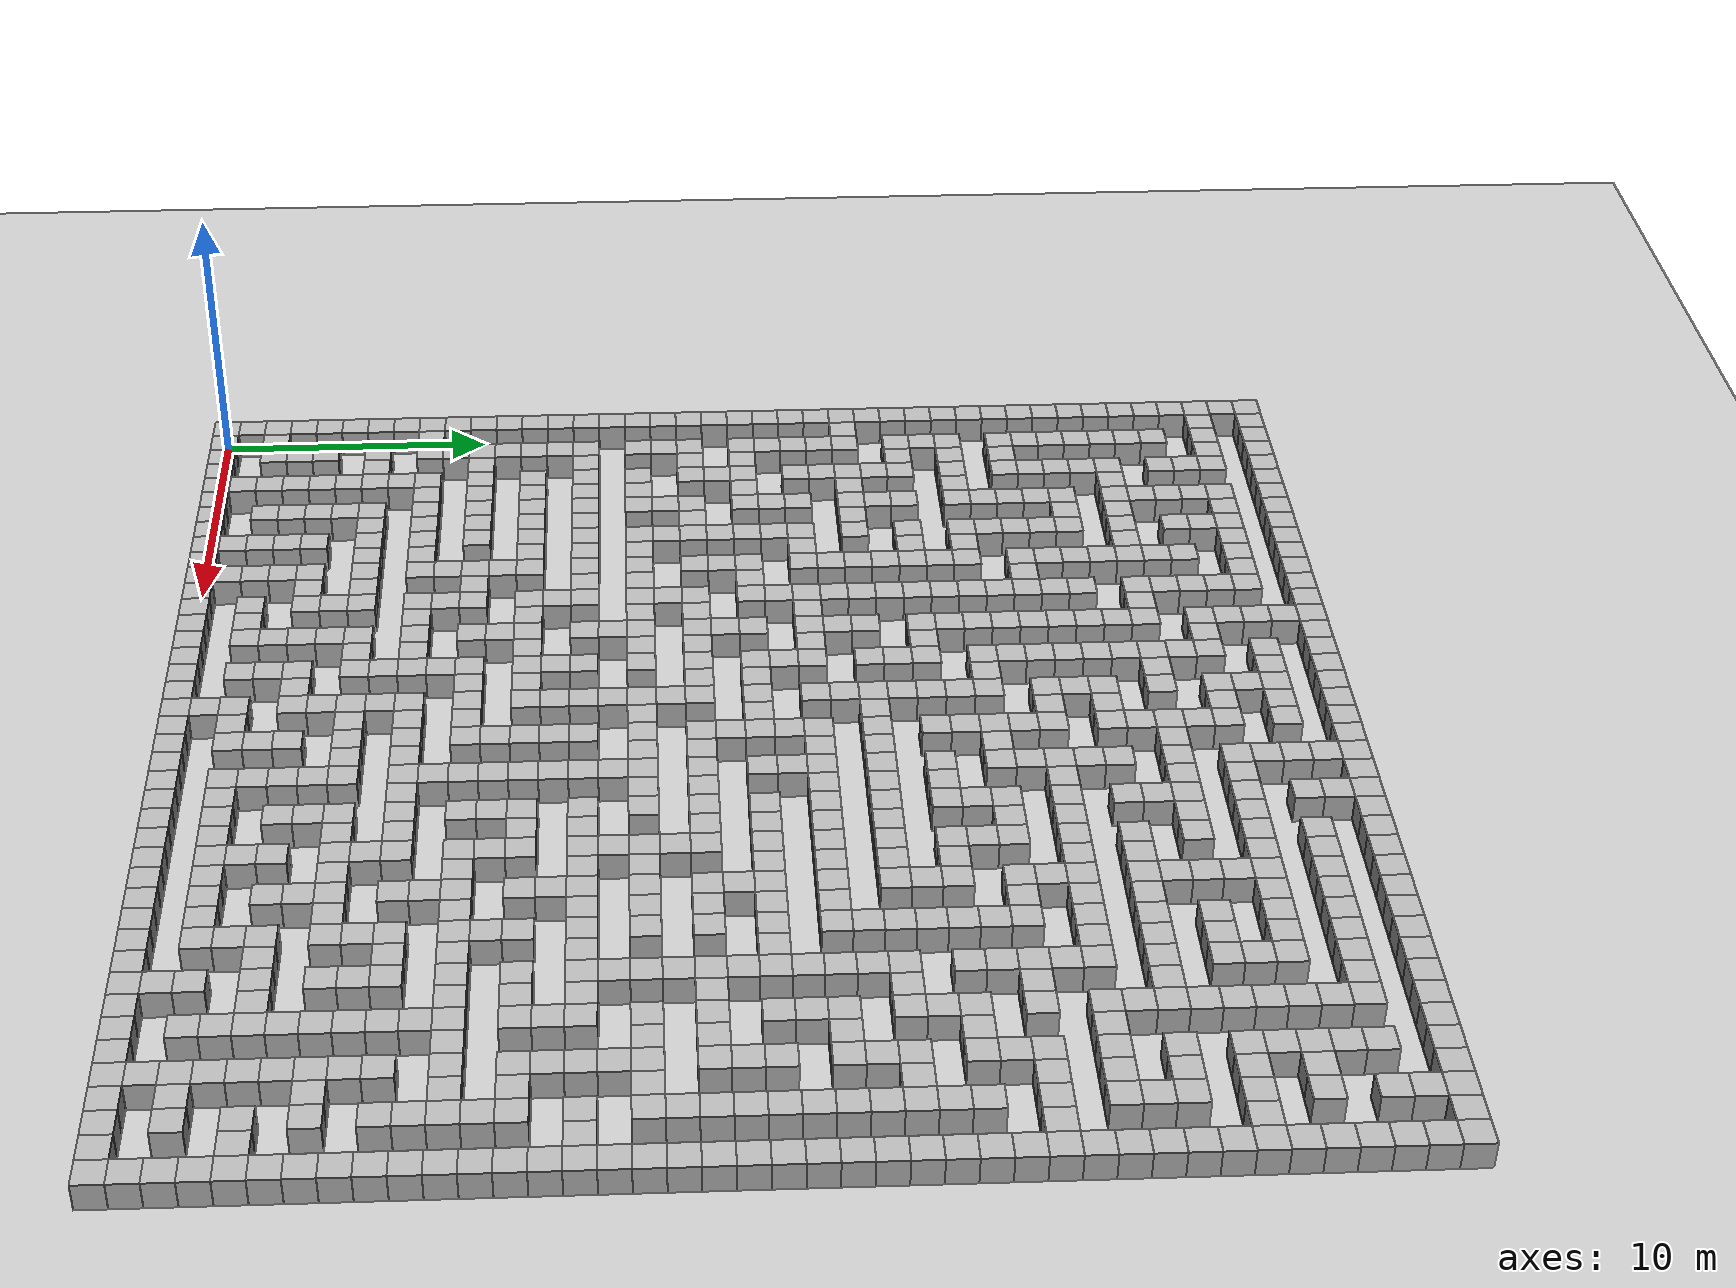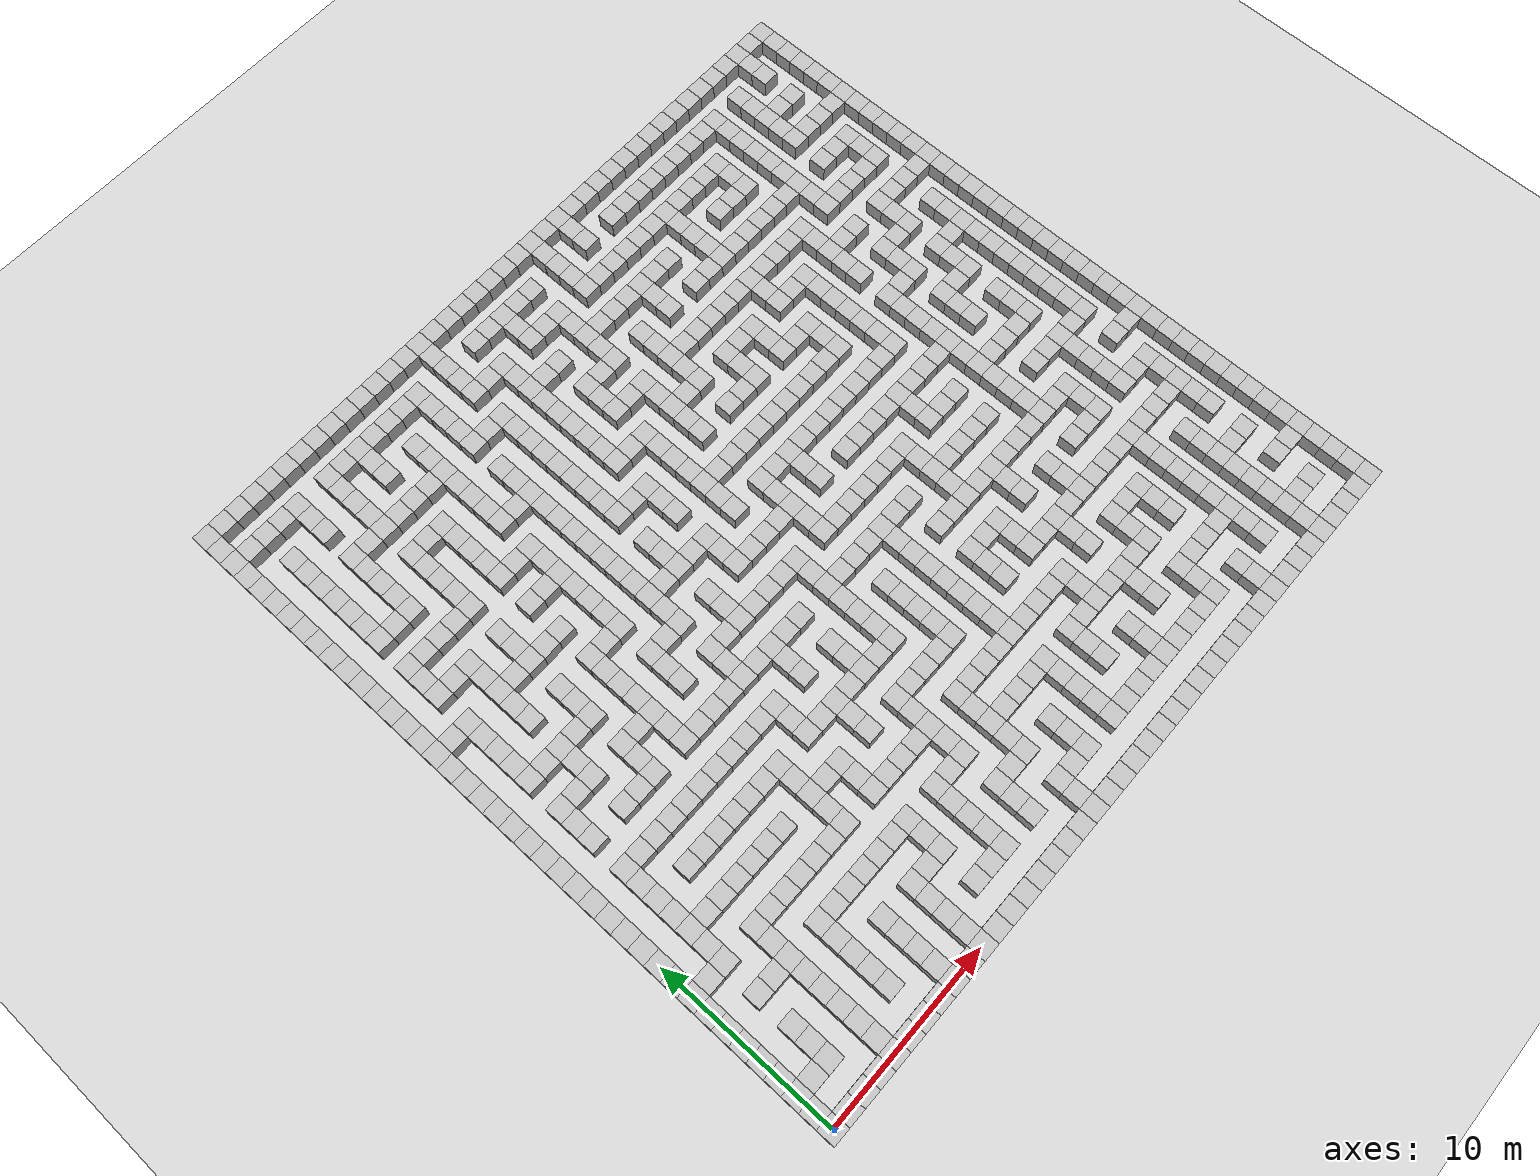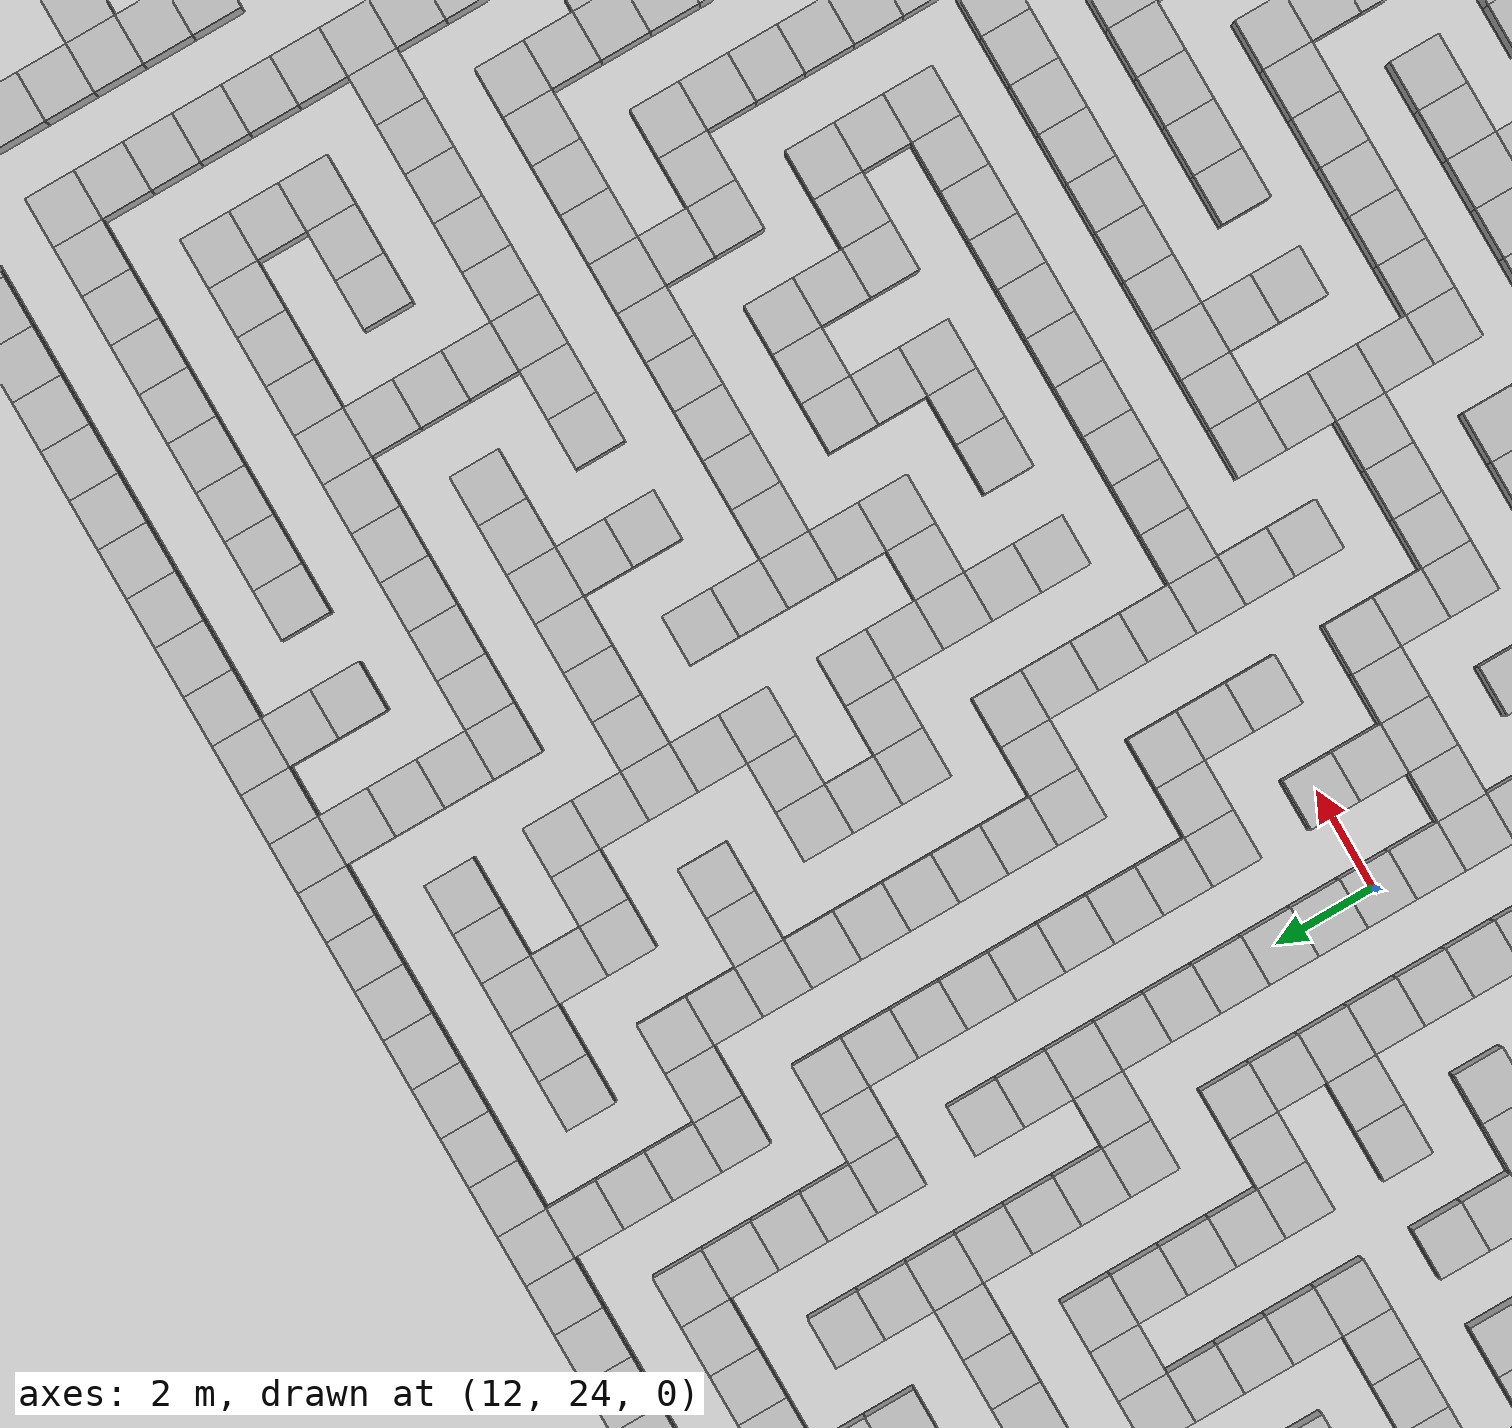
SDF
<sdf version="1.8">
    <world name="custom_maze">
        <physics name="1ms" type="ignored">
            <max_step_size>0.001</max_step_size>
            <real_time_factor>1</real_time_factor>
            <real_time_update_rate>1000</real_time_update_rate>
        </physics>
        <plugin name="gz::sim::systems::Physics" filename="gz-sim-physics-system"/>
        <plugin name="gz::sim::systems::UserCommands" filename="gz-sim-user-commands-system"/>
        <plugin name="gz::sim::systems::SceneBroadcaster" filename="gz-sim-scene-broadcaster-system"/>
        <plugin name="gz::sim::systems::Contact" filename="gz-sim-contact-system"/>
        <light name="sun" type="directional">
            <cast_shadows>1</cast_shadows>
            <pose>0 0 10 0 -0 0</pose>
            <diffuse>0.8 0.8 0.8 1</diffuse>
            <specular>0.2 0.2 0.2 1</specular>
            <attenuation>
                <range>1000</range>
                <constant>0.90000000000000002</constant>
                <linear>0.01</linear>
                <quadratic>0.001</quadratic>
            </attenuation>
            <direction>-0.5 0.1 -0.9</direction>
            <spot>
                <inner_angle>0</inner_angle>
                <outer_angle>0</outer_angle>
                <falloff>0</falloff>
            </spot>
        </light>
        <gravity>0 0 -9.8</gravity>
        <magnetic_field>6e-06 2.3e-05 -4.2e-05</magnetic_field>
        <atmosphere type="adiabatic"/>
        <scene>
            <ambient>0.4 0.4 0.4 1</ambient>
            <background>0.7 0.7 0.7 1</background>
            <shadows>1</shadows>
        </scene>
        <model name="ground_plane">
            <static>1</static>
            <link name="link">
                <collision name="collision">
                    <geometry>
                        <plane>
                            <normal>0 0 1</normal>
                            <size>100 100</size>
                        </plane>
                    </geometry>
                    <surface>
                        <friction>
                            <ode/>
                        </friction>
                        <bounce/>
                        <contact/>
                    </surface>
                </collision>
                <visual name="visual">
                    <geometry>
                        <plane>
                            <normal>0 0 1</normal>
                            <size>100 100</size>
                        </plane>
                    </geometry>
                    <material>
                        <ambient>0.8 0.8 0.8 1</ambient>
                        <diffuse>0.8 0.8 0.8 1</diffuse>
                        <specular>0.8 0.8 0.8 1</specular>
                    </material>
                    <plugin name="__default__" filename="__default__"/>
                </visual>
            </link>
            <plugin name="__default__" filename="__default__"/>
            <pose>0 0 0 0 -0 0</pose>
        </model>
        <model name="border">
            <pose>0 0 1 0 0 0</pose>
            <static>true</static>
        </model>
        <model name="obstacles">
            <pose>0 0 0.5 0 0 0</pose>
            <static>true</static>
            <link name="wall1">
                <pose>18 17 0 0 0 0</pose>
                <static>true</static>
                <collision name="wall1_collision">
                    <geometry>
                        <box>
                            <size>1 1 1</size>
                        </box>
                    </geometry>
                </collision>
                <visual name="wall1_visual">
                    <geometry>
                        <box>
                            <size>1 1 1</size>
                        </box>
                    </geometry>
                </visual>
            </link>
            <link name="wall2">
                <pose>29 32 0 0 0 0</pose>
                <static>true</static>
                <collision name="wall2_collision">
                    <geometry>
                        <box>
                            <size>1 1 1</size>
                        </box>
                    </geometry>
                </collision>
                <visual name="wall2_visual">
                    <geometry>
                        <box>
                            <size>1 1 1</size>
                        </box>
                    </geometry>
                </visual>
            </link>
            <link name="wall3">
                <pose>0 5 0 0 0 0</pose>
                <static>true</static>
                <collision name="wall3_collision">
                    <geometry>
                        <box>
                            <size>1 1 1</size>
                        </box>
                    </geometry>
                </collision>
                <visual name="wall3_visual">
                    <geometry>
                        <box>
                            <size>1 1 1</size>
                        </box>
                    </geometry>
                </visual>
            </link>
            <link name="wall4">
                <pose>11 14 0 0 0 0</pose>
                <static>true</static>
                <collision name="wall4_collision">
                    <geometry>
                        <box>
                            <size>1 1 1</size>
                        </box>
                    </geometry>
                </collision>
                <visual name="wall4_visual">
                    <geometry>
                        <box>
                            <size>1 1 1</size>
                        </box>
                    </geometry>
                </visual>
            </link>
            <link name="wall5">
                <pose>33 38 0 0 0 0</pose>
                <static>true</static>
                <collision name="wall5_collision">
                    <geometry>
                        <box>
                            <size>1 1 1</size>
                        </box>
                    </geometry>
                </collision>
                <visual name="wall5_visual">
                    <geometry>
                        <box>
                            <size>1 1 1</size>
                        </box>
                    </geometry>
                </visual>
            </link>
            <link name="wall6">
                <pose>34 3 0 0 0 0</pose>
                <static>true</static>
                <collision name="wall6_collision">
                    <geometry>
                        <box>
                            <size>1 1 1</size>
                        </box>
                    </geometry>
                </collision>
                <visual name="wall6_visual">
                    <geometry>
                        <box>
                            <size>1 1 1</size>
                        </box>
                    </geometry>
                </visual>
            </link>
            <link name="wall7">
                <pose>25 34 0 0 0 0</pose>
                <static>true</static>
                <collision name="wall7_collision">
                    <geometry>
                        <box>
                            <size>1 1 1</size>
                        </box>
                    </geometry>
                </collision>
                <visual name="wall7_visual">
                    <geometry>
                        <box>
                            <size>1 1 1</size>
                        </box>
                    </geometry>
                </visual>
            </link>
            <link name="wall8">
                <pose>22 28 0 0 0 0</pose>
                <static>true</static>
                <collision name="wall8_collision">
                    <geometry>
                        <box>
                            <size>1 1 1</size>
                        </box>
                    </geometry>
                </collision>
                <visual name="wall8_visual">
                    <geometry>
                        <box>
                            <size>1 1 1</size>
                        </box>
                    </geometry>
                </visual>
            </link>
            <link name="wall9">
                <pose>14 24 0 0 0 0</pose>
                <static>true</static>
                <collision name="wall9_collision">
                    <geometry>
                        <box>
                            <size>1 1 1</size>
                        </box>
                    </geometry>
                </collision>
                <visual name="wall9_visual">
                    <geometry>
                        <box>
                            <size>1 1 1</size>
                        </box>
                    </geometry>
                </visual>
            </link>
            <link name="wall10">
                <pose>38 9 0 0 0 0</pose>
                <static>true</static>
                <collision name="wall10_collision">
                    <geometry>
                        <box>
                            <size>1 1 1</size>
                        </box>
                    </geometry>
                </collision>
                <visual name="wall10_visual">
                    <geometry>
                        <box>
                            <size>1 1 1</size>
                        </box>
                    </geometry>
                </visual>
            </link>
            <link name="wall11">
                <pose>18 30 0 0 0 0</pose>
                <static>true</static>
                <collision name="wall11_collision">
                    <geometry>
                        <box>
                            <size>1 1 1</size>
                        </box>
                    </geometry>
                </collision>
                <visual name="wall11_visual">
                    <geometry>
                        <box>
                            <size>1 1 1</size>
                        </box>
                    </geometry>
                </visual>
            </link>
            <link name="wall12">
                <pose>30 4 0 0 0 0</pose>
                <static>true</static>
                <collision name="wall12_collision">
                    <geometry>
                        <box>
                            <size>1 1 1</size>
                        </box>
                    </geometry>
                </collision>
                <visual name="wall12_visual">
                    <geometry>
                        <box>
                            <size>1 1 1</size>
                        </box>
                    </geometry>
                </visual>
            </link>
            <link name="wall13">
                <pose>10 31 0 0 0 0</pose>
                <static>true</static>
                <collision name="wall13_collision">
                    <geometry>
                        <box>
                            <size>1 1 1</size>
                        </box>
                    </geometry>
                </collision>
                <visual name="wall13_visual">
                    <geometry>
                        <box>
                            <size>1 1 1</size>
                        </box>
                    </geometry>
                </visual>
            </link>
            <link name="wall14">
                <pose>2 27 0 0 0 0</pose>
                <static>true</static>
                <collision name="wall14_collision">
                    <geometry>
                        <box>
                            <size>1 1 1</size>
                        </box>
                    </geometry>
                </collision>
                <visual name="wall14_visual">
                    <geometry>
                        <box>
                            <size>1 1 1</size>
                        </box>
                    </geometry>
                </visual>
            </link>
            <link name="wall15">
                <pose>22 5 0 0 0 0</pose>
                <static>true</static>
                <collision name="wall15_collision">
                    <geometry>
                        <box>
                            <size>1 1 1</size>
                        </box>
                    </geometry>
                </collision>
                <visual name="wall15_visual">
                    <geometry>
                        <box>
                            <size>1 1 1</size>
                        </box>
                    </geometry>
                </visual>
            </link>
            <link name="wall16">
                <pose>34 16 0 0 0 0</pose>
                <static>true</static>
                <collision name="wall16_collision">
                    <geometry>
                        <box>
                            <size>1 1 1</size>
                        </box>
                    </geometry>
                </collision>
                <visual name="wall16_visual">
                    <geometry>
                        <box>
                            <size>1 1 1</size>
                        </box>
                    </geometry>
                </visual>
            </link>
            <link name="wall17">
                <pose>3 28 0 0 0 0</pose>
                <static>true</static>
                <collision name="wall17_collision">
                    <geometry>
                        <box>
                            <size>1 1 1</size>
                        </box>
                    </geometry>
                </collision>
                <visual name="wall17_visual">
                    <geometry>
                        <box>
                            <size>1 1 1</size>
                        </box>
                    </geometry>
                </visual>
            </link>
            <link name="wall18">
                <pose>14 37 0 0 0 0</pose>
                <static>true</static>
                <collision name="wall18_collision">
                    <geometry>
                        <box>
                            <size>1 1 1</size>
                        </box>
                    </geometry>
                </collision>
                <visual name="wall18_visual">
                    <geometry>
                        <box>
                            <size>1 1 1</size>
                        </box>
                    </geometry>
                </visual>
            </link>
            <link name="wall19">
                <pose>26 11 0 0 0 0</pose>
                <static>true</static>
                <collision name="wall19_collision">
                    <geometry>
                        <box>
                            <size>1 1 1</size>
                        </box>
                    </geometry>
                </collision>
                <visual name="wall19_visual">
                    <geometry>
                        <box>
                            <size>1 1 1</size>
                        </box>
                    </geometry>
                </visual>
            </link>
            <link name="wall20">
                <pose>18 7 0 0 0 0</pose>
                <static>true</static>
                <collision name="wall20_collision">
                    <geometry>
                        <box>
                            <size>1 1 1</size>
                        </box>
                    </geometry>
                </collision>
                <visual name="wall20_visual">
                    <geometry>
                        <box>
                            <size>1 1 1</size>
                        </box>
                    </geometry>
                </visual>
            </link>
            <link name="wall21">
                <pose>29 22 0 0 0 0</pose>
                <static>true</static>
                <collision name="wall21_collision">
                    <geometry>
                        <box>
                            <size>1 1 1</size>
                        </box>
                    </geometry>
                </collision>
                <visual name="wall21_visual">
                    <geometry>
                        <box>
                            <size>1 1 1</size>
                        </box>
                    </geometry>
                </visual>
            </link>
            <link name="wall22">
                <pose>21 18 0 0 0 0</pose>
                <static>true</static>
                <collision name="wall22_collision">
                    <geometry>
                        <box>
                            <size>1 1 1</size>
                        </box>
                    </geometry>
                </collision>
                <visual name="wall22_visual">
                    <geometry>
                        <box>
                            <size>1 1 1</size>
                        </box>
                    </geometry>
                </visual>
            </link>
            <link name="wall23">
                <pose>40 31 0 0 0 0</pose>
                <static>true</static>
                <collision name="wall23_collision">
                    <geometry>
                        <box>
                            <size>1 1 1</size>
                        </box>
                    </geometry>
                </collision>
                <visual name="wall23_visual">
                    <geometry>
                        <box>
                            <size>1 1 1</size>
                        </box>
                    </geometry>
                </visual>
            </link>
            <link name="wall24">
                <pose>6 38 0 0 0 0</pose>
                <static>true</static>
                <collision name="wall24_collision">
                    <geometry>
                        <box>
                            <size>1 1 1</size>
                        </box>
                    </geometry>
                </collision>
                <visual name="wall24_visual">
                    <geometry>
                        <box>
                            <size>1 1 1</size>
                        </box>
                    </geometry>
                </visual>
            </link>
            <link name="wall25">
                <pose>11 4 0 0 0 0</pose>
                <static>true</static>
                <collision name="wall25_collision">
                    <geometry>
                        <box>
                            <size>1 1 1</size>
                        </box>
                    </geometry>
                </collision>
                <visual name="wall25_visual">
                    <geometry>
                        <box>
                            <size>1 1 1</size>
                        </box>
                    </geometry>
                </visual>
            </link>
            <link name="wall26">
                <pose>10 8 0 0 0 0</pose>
                <static>true</static>
                <collision name="wall26_collision">
                    <geometry>
                        <box>
                            <size>1 1 1</size>
                        </box>
                    </geometry>
                </collision>
                <visual name="wall26_visual">
                    <geometry>
                        <box>
                            <size>1 1 1</size>
                        </box>
                    </geometry>
                </visual>
            </link>
            <link name="wall27">
                <pose>33 28 0 0 0 0</pose>
                <static>true</static>
                <collision name="wall27_collision">
                    <geometry>
                        <box>
                            <size>1 1 1</size>
                        </box>
                    </geometry>
                </collision>
                <visual name="wall27_visual">
                    <geometry>
                        <box>
                            <size>1 1 1</size>
                        </box>
                    </geometry>
                </visual>
            </link>
            <link name="wall28">
                <pose>25 24 0 0 0 0</pose>
                <static>true</static>
                <collision name="wall28_collision">
                    <geometry>
                        <box>
                            <size>1 1 1</size>
                        </box>
                    </geometry>
                </collision>
                <visual name="wall28_visual">
                    <geometry>
                        <box>
                            <size>1 1 1</size>
                        </box>
                    </geometry>
                </visual>
            </link>
            <link name="wall29">
                <pose>2 40 0 0 0 0</pose>
                <static>true</static>
                <collision name="wall29_collision">
                    <geometry>
                        <box>
                            <size>1 1 1</size>
                        </box>
                    </geometry>
                </collision>
                <visual name="wall29_visual">
                    <geometry>
                        <box>
                            <size>1 1 1</size>
                        </box>
                    </geometry>
                </visual>
            </link>
            <link name="wall30">
                <pose>22 18 0 0 0 0</pose>
                <static>true</static>
                <collision name="wall30_collision">
                    <geometry>
                        <box>
                            <size>1 1 1</size>
                        </box>
                    </geometry>
                </collision>
                <visual name="wall30_visual">
                    <geometry>
                        <box>
                            <size>1 1 1</size>
                        </box>
                    </geometry>
                </visual>
            </link>
            <link name="wall31">
                <pose>14 14 0 0 0 0</pose>
                <static>true</static>
                <collision name="wall31_collision">
                    <geometry>
                        <box>
                            <size>1 1 1</size>
                        </box>
                    </geometry>
                </collision>
                <visual name="wall31_visual">
                    <geometry>
                        <box>
                            <size>1 1 1</size>
                        </box>
                    </geometry>
                </visual>
            </link>
            <link name="wall32">
                <pose>36 38 0 0 0 0</pose>
                <static>true</static>
                <collision name="wall32_collision">
                    <geometry>
                        <box>
                            <size>1 1 1</size>
                        </box>
                    </geometry>
                </collision>
                <visual name="wall32_visual">
                    <geometry>
                        <box>
                            <size>1 1 1</size>
                        </box>
                    </geometry>
                </visual>
            </link>
            <link name="wall33">
                <pose>28 34 0 0 0 0</pose>
                <static>true</static>
                <collision name="wall33_collision">
                    <geometry>
                        <box>
                            <size>1 1 1</size>
                        </box>
                    </geometry>
                </collision>
                <visual name="wall33_visual">
                    <geometry>
                        <box>
                            <size>1 1 1</size>
                        </box>
                    </geometry>
                </visual>
            </link>
            <link name="wall34">
                <pose>40 8 0 0 0 0</pose>
                <static>true</static>
                <collision name="wall34_collision">
                    <geometry>
                        <box>
                            <size>1 1 1</size>
                        </box>
                    </geometry>
                </collision>
                <visual name="wall34_visual">
                    <geometry>
                        <box>
                            <size>1 1 1</size>
                        </box>
                    </geometry>
                </visual>
            </link>
            <link name="wall35">
                <pose>2 17 0 0 0 0</pose>
                <static>true</static>
                <collision name="wall35_collision">
                    <geometry>
                        <box>
                            <size>1 1 1</size>
                        </box>
                    </geometry>
                </collision>
                <visual name="wall35_visual">
                    <geometry>
                        <box>
                            <size>1 1 1</size>
                        </box>
                    </geometry>
                </visual>
            </link>
            <link name="wall36">
                <pose>34 6 0 0 0 0</pose>
                <static>true</static>
                <collision name="wall36_collision">
                    <geometry>
                        <box>
                            <size>1 1 1</size>
                        </box>
                    </geometry>
                </collision>
                <visual name="wall36_visual">
                    <geometry>
                        <box>
                            <size>1 1 1</size>
                        </box>
                    </geometry>
                </visual>
            </link>
            <link name="wall37">
                <pose>3 18 0 0 0 0</pose>
                <static>true</static>
                <collision name="wall37_collision">
                    <geometry>
                        <box>
                            <size>1 1 1</size>
                        </box>
                    </geometry>
                </collision>
                <visual name="wall37_visual">
                    <geometry>
                        <box>
                            <size>1 1 1</size>
                        </box>
                    </geometry>
                </visual>
            </link>
            <link name="wall38">
                <pose>36 15 0 0 0 0</pose>
                <static>true</static>
                <collision name="wall38_collision">
                    <geometry>
                        <box>
                            <size>1 1 1</size>
                        </box>
                    </geometry>
                </collision>
                <visual name="wall38_visual">
                    <geometry>
                        <box>
                            <size>1 1 1</size>
                        </box>
                    </geometry>
                </visual>
            </link>
            <link name="wall39">
                <pose>17 38 0 0 0 0</pose>
                <static>true</static>
                <collision name="wall39_collision">
                    <geometry>
                        <box>
                            <size>1 1 1</size>
                        </box>
                    </geometry>
                </collision>
                <visual name="wall39_visual">
                    <geometry>
                        <box>
                            <size>1 1 1</size>
                        </box>
                    </geometry>
                </visual>
            </link>
            <link name="wall40">
                <pose>9 34 0 0 0 0</pose>
                <static>true</static>
                <collision name="wall40_collision">
                    <geometry>
                        <box>
                            <size>1 1 1</size>
                        </box>
                    </geometry>
                </collision>
                <visual name="wall40_visual">
                    <geometry>
                        <box>
                            <size>1 1 1</size>
                        </box>
                    </geometry>
                </visual>
            </link>
            <link name="wall41">
                <pose>21 8 0 0 0 0</pose>
                <static>true</static>
                <collision name="wall41_collision">
                    <geometry>
                        <box>
                            <size>1 1 1</size>
                        </box>
                    </geometry>
                </collision>
                <visual name="wall41_visual">
                    <geometry>
                        <box>
                            <size>1 1 1</size>
                        </box>
                    </geometry>
                </visual>
            </link>
            <link name="wall42">
                <pose>40 21 0 0 0 0</pose>
                <static>true</static>
                <collision name="wall42_collision">
                    <geometry>
                        <box>
                            <size>1 1 1</size>
                        </box>
                    </geometry>
                </collision>
                <visual name="wall42_visual">
                    <geometry>
                        <box>
                            <size>1 1 1</size>
                        </box>
                    </geometry>
                </visual>
            </link>
            <link name="wall43">
                <pose>6 28 0 0 0 0</pose>
                <static>true</static>
                <collision name="wall43_collision">
                    <geometry>
                        <box>
                            <size>1 1 1</size>
                        </box>
                    </geometry>
                </collision>
                <visual name="wall43_visual">
                    <geometry>
                        <box>
                            <size>1 1 1</size>
                        </box>
                    </geometry>
                </visual>
            </link>
            <link name="wall44">
                <pose>33 18 0 0 0 0</pose>
                <static>true</static>
                <collision name="wall44_collision">
                    <geometry>
                        <box>
                            <size>1 1 1</size>
                        </box>
                    </geometry>
                </collision>
                <visual name="wall44_visual">
                    <geometry>
                        <box>
                            <size>1 1 1</size>
                        </box>
                    </geometry>
                </visual>
            </link>
            <link name="wall45">
                <pose>25 14 0 0 0 0</pose>
                <static>true</static>
                <collision name="wall45_collision">
                    <geometry>
                        <box>
                            <size>1 1 1</size>
                        </box>
                    </geometry>
                </collision>
                <visual name="wall45_visual">
                    <geometry>
                        <box>
                            <size>1 1 1</size>
                        </box>
                    </geometry>
                </visual>
            </link>
            <link name="wall46">
                <pose>32 22 0 0 0 0</pose>
                <static>true</static>
                <collision name="wall46_collision">
                    <geometry>
                        <box>
                            <size>1 1 1</size>
                        </box>
                    </geometry>
                </collision>
                <visual name="wall46_visual">
                    <geometry>
                        <box>
                            <size>1 1 1</size>
                        </box>
                    </geometry>
                </visual>
            </link>
            <link name="wall47">
                <pose>2 30 0 0 0 0</pose>
                <static>true</static>
                <collision name="wall47_collision">
                    <geometry>
                        <box>
                            <size>1 1 1</size>
                        </box>
                    </geometry>
                </collision>
                <visual name="wall47_visual">
                    <geometry>
                        <box>
                            <size>1 1 1</size>
                        </box>
                    </geometry>
                </visual>
            </link>
            <link name="wall48">
                <pose>22 8 0 0 0 0</pose>
                <static>true</static>
                <collision name="wall48_collision">
                    <geometry>
                        <box>
                            <size>1 1 1</size>
                        </box>
                    </geometry>
                </collision>
                <visual name="wall48_visual">
                    <geometry>
                        <box>
                            <size>1 1 1</size>
                        </box>
                    </geometry>
                </visual>
            </link>
            <link name="wall49">
                <pose>14 4 0 0 0 0</pose>
                <static>true</static>
                <collision name="wall49_collision">
                    <geometry>
                        <box>
                            <size>1 1 1</size>
                        </box>
                    </geometry>
                </collision>
                <visual name="wall49_visual">
                    <geometry>
                        <box>
                            <size>1 1 1</size>
                        </box>
                    </geometry>
                </visual>
            </link>
            <link name="wall50">
                <pose>36 28 0 0 0 0</pose>
                <static>true</static>
                <collision name="wall50_collision">
                    <geometry>
                        <box>
                            <size>1 1 1</size>
                        </box>
                    </geometry>
                </collision>
                <visual name="wall50_visual">
                    <geometry>
                        <box>
                            <size>1 1 1</size>
                        </box>
                    </geometry>
                </visual>
            </link>
            <link name="wall51">
                <pose>28 24 0 0 0 0</pose>
                <static>true</static>
                <collision name="wall51_collision">
                    <geometry>
                        <box>
                            <size>1 1 1</size>
                        </box>
                    </geometry>
                </collision>
                <visual name="wall51_visual">
                    <geometry>
                        <box>
                            <size>1 1 1</size>
                        </box>
                    </geometry>
                </visual>
            </link>
            <link name="wall52">
                <pose>5 40 0 0 0 0</pose>
                <static>true</static>
                <collision name="wall52_collision">
                    <geometry>
                        <box>
                            <size>1 1 1</size>
                        </box>
                    </geometry>
                </collision>
                <visual name="wall52_visual">
                    <geometry>
                        <box>
                            <size>1 1 1</size>
                        </box>
                    </geometry>
                </visual>
            </link>
            <link name="wall53">
                <pose>6 5 0 0 0 0</pose>
                <static>true</static>
                <collision name="wall53_collision">
                    <geometry>
                        <box>
                            <size>1 1 1</size>
                        </box>
                    </geometry>
                </collision>
                <visual name="wall53_visual">
                    <geometry>
                        <box>
                            <size>1 1 1</size>
                        </box>
                    </geometry>
                </visual>
            </link>
            <link name="wall54">
                <pose>31 34 0 0 0 0</pose>
                <static>true</static>
                <collision name="wall54_collision">
                    <geometry>
                        <box>
                            <size>1 1 1</size>
                        </box>
                    </geometry>
                </collision>
                <visual name="wall54_visual">
                    <geometry>
                        <box>
                            <size>1 1 1</size>
                        </box>
                    </geometry>
                </visual>
            </link>
            <link name="wall55">
                <pose>10 11 0 0 0 0</pose>
                <static>true</static>
                <collision name="wall55_collision">
                    <geometry>
                        <box>
                            <size>1 1 1</size>
                        </box>
                    </geometry>
                </collision>
                <visual name="wall55_visual">
                    <geometry>
                        <box>
                            <size>1 1 1</size>
                        </box>
                    </geometry>
                </visual>
            </link>
            <link name="wall56">
                <pose>13 22 0 0 0 0</pose>
                <static>true</static>
                <collision name="wall56_collision">
                    <geometry>
                        <box>
                            <size>1 1 1</size>
                        </box>
                    </geometry>
                </collision>
                <visual name="wall56_visual">
                    <geometry>
                        <box>
                            <size>1 1 1</size>
                        </box>
                    </geometry>
                </visual>
            </link>
            <link name="wall57">
                <pose>32 35 0 0 0 0</pose>
                <static>true</static>
                <collision name="wall57_collision">
                    <geometry>
                        <box>
                            <size>1 1 1</size>
                        </box>
                    </geometry>
                </collision>
                <visual name="wall57_visual">
                    <geometry>
                        <box>
                            <size>1 1 1</size>
                        </box>
                    </geometry>
                </visual>
            </link>
            <link name="wall58">
                <pose>35 40 0 0 0 0</pose>
                <static>true</static>
                <collision name="wall58_collision">
                    <geometry>
                        <box>
                            <size>1 1 1</size>
                        </box>
                    </geometry>
                </collision>
                <visual name="wall58_visual">
                    <geometry>
                        <box>
                            <size>1 1 1</size>
                        </box>
                    </geometry>
                </visual>
            </link>
            <link name="wall59">
                <pose>36 5 0 0 0 0</pose>
                <static>true</static>
                <collision name="wall59_collision">
                    <geometry>
                        <box>
                            <size>1 1 1</size>
                        </box>
                    </geometry>
                </collision>
                <visual name="wall59_visual">
                    <geometry>
                        <box>
                            <size>1 1 1</size>
                        </box>
                    </geometry>
                </visual>
            </link>
            <link name="wall60">
                <pose>17 28 0 0 0 0</pose>
                <static>true</static>
                <collision name="wall60_collision">
                    <geometry>
                        <box>
                            <size>1 1 1</size>
                        </box>
                    </geometry>
                </collision>
                <visual name="wall60_visual">
                    <geometry>
                        <box>
                            <size>1 1 1</size>
                        </box>
                    </geometry>
                </visual>
            </link>
            <link name="wall61">
                <pose>29 2 0 0 0 0</pose>
                <static>true</static>
                <collision name="wall61_collision">
                    <geometry>
                        <box>
                            <size>1 1 1</size>
                        </box>
                    </geometry>
                </collision>
                <visual name="wall61_visual">
                    <geometry>
                        <box>
                            <size>1 1 1</size>
                        </box>
                    </geometry>
                </visual>
            </link>
            <link name="wall62">
                <pose>40 11 0 0 0 0</pose>
                <static>true</static>
                <collision name="wall62_collision">
                    <geometry>
                        <box>
                            <size>1 1 1</size>
                        </box>
                    </geometry>
                </collision>
                <visual name="wall62_visual">
                    <geometry>
                        <box>
                            <size>1 1 1</size>
                        </box>
                    </geometry>
                </visual>
            </link>
            <link name="wall63">
                <pose>6 18 0 0 0 0</pose>
                <static>true</static>
                <collision name="wall63_collision">
                    <geometry>
                        <box>
                            <size>1 1 1</size>
                        </box>
                    </geometry>
                </collision>
                <visual name="wall63_visual">
                    <geometry>
                        <box>
                            <size>1 1 1</size>
                        </box>
                    </geometry>
                </visual>
            </link>
            <link name="wall64">
                <pose>20 38 0 0 0 0</pose>
                <static>true</static>
                <collision name="wall64_collision">
                    <geometry>
                        <box>
                            <size>1 1 1</size>
                        </box>
                    </geometry>
                </collision>
                <visual name="wall64_visual">
                    <geometry>
                        <box>
                            <size>1 1 1</size>
                        </box>
                    </geometry>
                </visual>
            </link>
            <link name="wall65">
                <pose>12 34 0 0 0 0</pose>
                <static>true</static>
                <collision name="wall65_collision">
                    <geometry>
                        <box>
                            <size>1 1 1</size>
                        </box>
                    </geometry>
                </collision>
                <visual name="wall65_visual">
                    <geometry>
                        <box>
                            <size>1 1 1</size>
                        </box>
                    </geometry>
                </visual>
            </link>
            <link name="wall66">
                <pose>4 30 0 0 0 0</pose>
                <static>true</static>
                <collision name="wall66_collision">
                    <geometry>
                        <box>
                            <size>1 1 1</size>
                        </box>
                    </geometry>
                </collision>
                <visual name="wall66_visual">
                    <geometry>
                        <box>
                            <size>1 1 1</size>
                        </box>
                    </geometry>
                </visual>
            </link>
            <link name="wall67">
                <pose>32 12 0 0 0 0</pose>
                <static>true</static>
                <collision name="wall67_collision">
                    <geometry>
                        <box>
                            <size>1 1 1</size>
                        </box>
                    </geometry>
                </collision>
                <visual name="wall67_visual">
                    <geometry>
                        <box>
                            <size>1 1 1</size>
                        </box>
                    </geometry>
                </visual>
            </link>
            <link name="wall68">
                <pose>24 8 0 0 0 0</pose>
                <static>true</static>
                <collision name="wall68_collision">
                    <geometry>
                        <box>
                            <size>1 1 1</size>
                        </box>
                    </geometry>
                </collision>
                <visual name="wall68_visual">
                    <geometry>
                        <box>
                            <size>1 1 1</size>
                        </box>
                    </geometry>
                </visual>
            </link>
            <link name="wall69">
                <pose>1 24 0 0 0 0</pose>
                <static>true</static>
                <collision name="wall69_collision">
                    <geometry>
                        <box>
                            <size>1 1 1</size>
                        </box>
                    </geometry>
                </collision>
                <visual name="wall69_visual">
                    <geometry>
                        <box>
                            <size>1 1 1</size>
                        </box>
                    </geometry>
                </visual>
            </link>
            <link name="wall70">
                <pose>16 40 0 0 0 0</pose>
                <static>true</static>
                <collision name="wall70_collision">
                    <geometry>
                        <box>
                            <size>1 1 1</size>
                        </box>
                    </geometry>
                </collision>
                <visual name="wall70_visual">
                    <geometry>
                        <box>
                            <size>1 1 1</size>
                        </box>
                    </geometry>
                </visual>
            </link>
            <link name="wall71">
                <pose>36 18 0 0 0 0</pose>
                <static>true</static>
                <collision name="wall71_collision">
                    <geometry>
                        <box>
                            <size>1 1 1</size>
                        </box>
                    </geometry>
                </collision>
                <visual name="wall71_visual">
                    <geometry>
                        <box>
                            <size>1 1 1</size>
                        </box>
                    </geometry>
                </visual>
            </link>
            <link name="wall72">
                <pose>28 14 0 0 0 0</pose>
                <static>true</static>
                <collision name="wall72_collision">
                    <geometry>
                        <box>
                            <size>1 1 1</size>
                        </box>
                    </geometry>
                </collision>
                <visual name="wall72_visual">
                    <geometry>
                        <box>
                            <size>1 1 1</size>
                        </box>
                    </geometry>
                </visual>
            </link>
            <link name="wall73">
                <pose>0 37 0 0 0 0</pose>
                <static>true</static>
                <collision name="wall73_collision">
                    <geometry>
                        <box>
                            <size>1 1 1</size>
                        </box>
                    </geometry>
                </collision>
                <visual name="wall73_visual">
                    <geometry>
                        <box>
                            <size>1 1 1</size>
                        </box>
                    </geometry>
                </visual>
            </link>
            <link name="wall74">
                <pose>39 28 0 0 0 0</pose>
                <static>true</static>
                <collision name="wall74_collision">
                    <geometry>
                        <box>
                            <size>1 1 1</size>
                        </box>
                    </geometry>
                </collision>
                <visual name="wall74_visual">
                    <geometry>
                        <box>
                            <size>1 1 1</size>
                        </box>
                    </geometry>
                </visual>
            </link>
            <link name="wall75">
                <pose>13 12 0 0 0 0</pose>
                <static>true</static>
                <collision name="wall75_collision">
                    <geometry>
                        <box>
                            <size>1 1 1</size>
                        </box>
                    </geometry>
                </collision>
                <visual name="wall75_visual">
                    <geometry>
                        <box>
                            <size>1 1 1</size>
                        </box>
                    </geometry>
                </visual>
            </link>
            <link name="wall76">
                <pose>35 30 0 0 0 0</pose>
                <static>true</static>
                <collision name="wall76_collision">
                    <geometry>
                        <box>
                            <size>1 1 1</size>
                        </box>
                    </geometry>
                </collision>
                <visual name="wall76_visual">
                    <geometry>
                        <box>
                            <size>1 1 1</size>
                        </box>
                    </geometry>
                </visual>
            </link>
            <link name="wall77">
                <pose>9 14 0 0 0 0</pose>
                <static>true</static>
                <collision name="wall77_collision">
                    <geometry>
                        <box>
                            <size>1 1 1</size>
                        </box>
                    </geometry>
                </collision>
                <visual name="wall77_visual">
                    <geometry>
                        <box>
                            <size>1 1 1</size>
                        </box>
                    </geometry>
                </visual>
            </link>
            <link name="wall78">
                <pose>30 36 0 0 0 0</pose>
                <static>true</static>
                <collision name="wall78_collision">
                    <geometry>
                        <box>
                            <size>1 1 1</size>
                        </box>
                    </geometry>
                </collision>
                <visual name="wall78_visual">
                    <geometry>
                        <box>
                            <size>1 1 1</size>
                        </box>
                    </geometry>
                </visual>
            </link>
            <link name="wall79">
                <pose>20 28 0 0 0 0</pose>
                <static>true</static>
                <collision name="wall79_collision">
                    <geometry>
                        <box>
                            <size>1 1 1</size>
                        </box>
                    </geometry>
                </collision>
                <visual name="wall79_visual">
                    <geometry>
                        <box>
                            <size>1 1 1</size>
                        </box>
                    </geometry>
                </visual>
            </link>
            <link name="wall80">
                <pose>12 24 0 0 0 0</pose>
                <static>true</static>
                <collision name="wall80_collision">
                    <geometry>
                        <box>
                            <size>1 1 1</size>
                        </box>
                    </geometry>
                </collision>
                <visual name="wall80_visual">
                    <geometry>
                        <box>
                            <size>1 1 1</size>
                        </box>
                    </geometry>
                </visual>
            </link>
            <link name="wall81">
                <pose>4 20 0 0 0 0</pose>
                <static>true</static>
                <collision name="wall81_collision">
                    <geometry>
                        <box>
                            <size>1 1 1</size>
                        </box>
                    </geometry>
                </collision>
                <visual name="wall81_visual">
                    <geometry>
                        <box>
                            <size>1 1 1</size>
                        </box>
                    </geometry>
                </visual>
            </link>
            <link name="wall82">
                <pose>32 2 0 0 0 0</pose>
                <static>true</static>
                <collision name="wall82_collision">
                    <geometry>
                        <box>
                            <size>1 1 1</size>
                        </box>
                    </geometry>
                </collision>
                <visual name="wall82_visual">
                    <geometry>
                        <box>
                            <size>1 1 1</size>
                        </box>
                    </geometry>
                </visual>
            </link>
            <link name="wall83">
                <pose>16 30 0 0 0 0</pose>
                <static>true</static>
                <collision name="wall83_collision">
                    <geometry>
                        <box>
                            <size>1 1 1</size>
                        </box>
                    </geometry>
                </collision>
                <visual name="wall83_visual">
                    <geometry>
                        <box>
                            <size>1 1 1</size>
                        </box>
                    </geometry>
                </visual>
            </link>
            <link name="wall84">
                <pose>28 4 0 0 0 0</pose>
                <static>true</static>
                <collision name="wall84_collision">
                    <geometry>
                        <box>
                            <size>1 1 1</size>
                        </box>
                    </geometry>
                </collision>
                <visual name="wall84_visual">
                    <geometry>
                        <box>
                            <size>1 1 1</size>
                        </box>
                    </geometry>
                </visual>
            </link>
            <link name="wall85">
                <pose>8 31 0 0 0 0</pose>
                <static>true</static>
                <collision name="wall85_collision">
                    <geometry>
                        <box>
                            <size>1 1 1</size>
                        </box>
                    </geometry>
                </collision>
                <visual name="wall85_visual">
                    <geometry>
                        <box>
                            <size>1 1 1</size>
                        </box>
                    </geometry>
                </visual>
            </link>
            <link name="wall86">
                <pose>0 27 0 0 0 0</pose>
                <static>true</static>
                <collision name="wall86_collision">
                    <geometry>
                        <box>
                            <size>1 1 1</size>
                        </box>
                    </geometry>
                </collision>
                <visual name="wall86_visual">
                    <geometry>
                        <box>
                            <size>1 1 1</size>
                        </box>
                    </geometry>
                </visual>
            </link>
            <link name="wall87">
                <pose>19 40 0 0 0 0</pose>
                <static>true</static>
                <collision name="wall87_collision">
                    <geometry>
                        <box>
                            <size>1 1 1</size>
                        </box>
                    </geometry>
                </collision>
                <visual name="wall87_visual">
                    <geometry>
                        <box>
                            <size>1 1 1</size>
                        </box>
                    </geometry>
                </visual>
            </link>
            <link name="wall88">
                <pose>31 14 0 0 0 0</pose>
                <static>true</static>
                <collision name="wall88_collision">
                    <geometry>
                        <box>
                            <size>1 1 1</size>
                        </box>
                    </geometry>
                </collision>
                <visual name="wall88_visual">
                    <geometry>
                        <box>
                            <size>1 1 1</size>
                        </box>
                    </geometry>
                </visual>
            </link>
            <link name="wall89">
                <pose>12 37 0 0 0 0</pose>
                <static>true</static>
                <collision name="wall89_collision">
                    <geometry>
                        <box>
                            <size>1 1 1</size>
                        </box>
                    </geometry>
                </collision>
                <visual name="wall89_visual">
                    <geometry>
                        <box>
                            <size>1 1 1</size>
                        </box>
                    </geometry>
                </visual>
            </link>
            <link name="wall90">
                <pose>13 2 0 0 0 0</pose>
                <static>true</static>
                <collision name="wall90_collision">
                    <geometry>
                        <box>
                            <size>1 1 1</size>
                        </box>
                    </geometry>
                </collision>
                <visual name="wall90_visual">
                    <geometry>
                        <box>
                            <size>1 1 1</size>
                        </box>
                    </geometry>
                </visual>
            </link>
            <link name="wall91">
                <pose>4 33 0 0 0 0</pose>
                <static>true</static>
                <collision name="wall91_collision">
                    <geometry>
                        <box>
                            <size>1 1 1</size>
                        </box>
                    </geometry>
                </collision>
                <visual name="wall91_visual">
                    <geometry>
                        <box>
                            <size>1 1 1</size>
                        </box>
                    </geometry>
                </visual>
            </link>
            <link name="wall92">
                <pose>24 11 0 0 0 0</pose>
                <static>true</static>
                <collision name="wall92_collision">
                    <geometry>
                        <box>
                            <size>1 1 1</size>
                        </box>
                    </geometry>
                </collision>
                <visual name="wall92_visual">
                    <geometry>
                        <box>
                            <size>1 1 1</size>
                        </box>
                    </geometry>
                </visual>
            </link>
            <link name="wall93">
                <pose>16 7 0 0 0 0</pose>
                <static>true</static>
                <collision name="wall93_collision">
                    <geometry>
                        <box>
                            <size>1 1 1</size>
                        </box>
                    </geometry>
                </collision>
                <visual name="wall93_visual">
                    <geometry>
                        <box>
                            <size>1 1 1</size>
                        </box>
                    </geometry>
                </visual>
            </link>
            <link name="wall94">
                <pose>38 31 0 0 0 0</pose>
                <static>true</static>
                <collision name="wall94_collision">
                    <geometry>
                        <box>
                            <size>1 1 1</size>
                        </box>
                    </geometry>
                </collision>
                <visual name="wall94_visual">
                    <geometry>
                        <box>
                            <size>1 1 1</size>
                        </box>
                    </geometry>
                </visual>
            </link>
            <link name="wall95">
                <pose>8 8 0 0 0 0</pose>
                <static>true</static>
                <collision name="wall95_collision">
                    <geometry>
                        <box>
                            <size>1 1 1</size>
                        </box>
                    </geometry>
                </collision>
                <visual name="wall95_visual">
                    <geometry>
                        <box>
                            <size>1 1 1</size>
                        </box>
                    </geometry>
                </visual>
            </link>
            <link name="wall96">
                <pose>0 4 0 0 0 0</pose>
                <static>true</static>
                <collision name="wall96_collision">
                    <geometry>
                        <box>
                            <size>1 1 1</size>
                        </box>
                    </geometry>
                </collision>
                <visual name="wall96_visual">
                    <geometry>
                        <box>
                            <size>1 1 1</size>
                        </box>
                    </geometry>
                </visual>
            </link>
            <link name="wall97">
                <pose>30 26 0 0 0 0</pose>
                <static>true</static>
                <collision name="wall97_collision">
                    <geometry>
                        <box>
                            <size>1 1 1</size>
                        </box>
                    </geometry>
                </collision>
                <visual name="wall97_visual">
                    <geometry>
                        <box>
                            <size>1 1 1</size>
                        </box>
                    </geometry>
                </visual>
            </link>
            <link name="wall98">
                <pose>0 40 0 0 0 0</pose>
                <static>true</static>
                <collision name="wall98_collision">
                    <geometry>
                        <box>
                            <size>1 1 1</size>
                        </box>
                    </geometry>
                </collision>
                <visual name="wall98_visual">
                    <geometry>
                        <box>
                            <size>1 1 1</size>
                        </box>
                    </geometry>
                </visual>
            </link>
            <link name="wall99">
                <pose>20 18 0 0 0 0</pose>
                <static>true</static>
                <collision name="wall99_collision">
                    <geometry>
                        <box>
                            <size>1 1 1</size>
                        </box>
                    </geometry>
                </collision>
                <visual name="wall99_visual">
                    <geometry>
                        <box>
                            <size>1 1 1</size>
                        </box>
                    </geometry>
                </visual>
            </link>
            <link name="wall100">
                <pose>12 14 0 0 0 0</pose>
                <static>true</static>
                <collision name="wall100_collision">
                    <geometry>
                        <box>
                            <size>1 1 1</size>
                        </box>
                    </geometry>
                </collision>
                <visual name="wall100_visual">
                    <geometry>
                        <box>
                            <size>1 1 1</size>
                        </box>
                    </geometry>
                </visual>
            </link>
            <link name="wall101">
                <pose>4 10 0 0 0 0</pose>
                <static>true</static>
                <collision name="wall101_collision">
                    <geometry>
                        <box>
                            <size>1 1 1</size>
                        </box>
                    </geometry>
                </collision>
                <visual name="wall101_visual">
                    <geometry>
                        <box>
                            <size>1 1 1</size>
                        </box>
                    </geometry>
                </visual>
            </link>
            <link name="wall102">
                <pose>34 38 0 0 0 0</pose>
                <static>true</static>
                <collision name="wall102_collision">
                    <geometry>
                        <box>
                            <size>1 1 1</size>
                        </box>
                    </geometry>
                </collision>
                <visual name="wall102_visual">
                    <geometry>
                        <box>
                            <size>1 1 1</size>
                        </box>
                    </geometry>
                </visual>
            </link>
            <link name="wall103">
                <pose>38 8 0 0 0 0</pose>
                <static>true</static>
                <collision name="wall103_collision">
                    <geometry>
                        <box>
                            <size>1 1 1</size>
                        </box>
                    </geometry>
                </collision>
                <visual name="wall103_visual">
                    <geometry>
                        <box>
                            <size>1 1 1</size>
                        </box>
                    </geometry>
                </visual>
            </link>
            <link name="wall104">
                <pose>30 3 0 0 0 0</pose>
                <static>true</static>
                <collision name="wall104_collision">
                    <geometry>
                        <box>
                            <size>1 1 1</size>
                        </box>
                    </geometry>
                </collision>
                <visual name="wall104_visual">
                    <geometry>
                        <box>
                            <size>1 1 1</size>
                        </box>
                    </geometry>
                </visual>
            </link>
            <link name="wall105">
                <pose>8 21 0 0 0 0</pose>
                <static>true</static>
                <collision name="wall105_collision">
                    <geometry>
                        <box>
                            <size>1 1 1</size>
                        </box>
                    </geometry>
                </collision>
                <visual name="wall105_visual">
                    <geometry>
                        <box>
                            <size>1 1 1</size>
                        </box>
                    </geometry>
                </visual>
            </link>
            <link name="wall106">
                <pose>0 17 0 0 0 0</pose>
                <static>true</static>
                <collision name="wall106_collision">
                    <geometry>
                        <box>
                            <size>1 1 1</size>
                        </box>
                    </geometry>
                </collision>
                <visual name="wall106_visual">
                    <geometry>
                        <box>
                            <size>1 1 1</size>
                        </box>
                    </geometry>
                </visual>
            </link>
            <link name="wall107">
                <pose>19 30 0 0 0 0</pose>
                <static>true</static>
                <collision name="wall107_collision">
                    <geometry>
                        <box>
                            <size>1 1 1</size>
                        </box>
                    </geometry>
                </collision>
                <visual name="wall107_visual">
                    <geometry>
                        <box>
                            <size>1 1 1</size>
                        </box>
                    </geometry>
                </visual>
            </link>
            <link name="wall108">
                <pose>31 4 0 0 0 0</pose>
                <static>true</static>
                <collision name="wall108_collision">
                    <geometry>
                        <box>
                            <size>1 1 1</size>
                        </box>
                    </geometry>
                </collision>
                <visual name="wall108_visual">
                    <geometry>
                        <box>
                            <size>1 1 1</size>
                        </box>
                    </geometry>
                </visual>
            </link>
            <link name="wall109">
                <pose>23 0 0 0 0 0</pose>
                <static>true</static>
                <collision name="wall109_collision">
                    <geometry>
                        <box>
                            <size>1 1 1</size>
                        </box>
                    </geometry>
                </collision>
                <visual name="wall109_visual">
                    <geometry>
                        <box>
                            <size>1 1 1</size>
                        </box>
                    </geometry>
                </visual>
            </link>
            <link name="wall110">
                <pose>22 40 0 0 0 0</pose>
                <static>true</static>
                <collision name="wall110_collision">
                    <geometry>
                        <box>
                            <size>1 1 1</size>
                        </box>
                    </geometry>
                </collision>
                <visual name="wall110_visual">
                    <geometry>
                        <box>
                            <size>1 1 1</size>
                        </box>
                    </geometry>
                </visual>
            </link>
            <link name="wall111">
                <pose>14 36 0 0 0 0</pose>
                <static>true</static>
                <collision name="wall111_collision">
                    <geometry>
                        <box>
                            <size>1 1 1</size>
                        </box>
                    </geometry>
                </collision>
                <visual name="wall111_visual">
                    <geometry>
                        <box>
                            <size>1 1 1</size>
                        </box>
                    </geometry>
                </visual>
            </link>
            <link name="wall112">
                <pose>26 10 0 0 0 0</pose>
                <static>true</static>
                <collision name="wall112_collision">
                    <geometry>
                        <box>
                            <size>1 1 1</size>
                        </box>
                    </geometry>
                </collision>
                <visual name="wall112_visual">
                    <geometry>
                        <box>
                            <size>1 1 1</size>
                        </box>
                    </geometry>
                </visual>
            </link>
            <link name="wall113">
                <pose>18 6 0 0 0 0</pose>
                <static>true</static>
                <collision name="wall113_collision">
                    <geometry>
                        <box>
                            <size>1 1 1</size>
                        </box>
                    </geometry>
                </collision>
                <visual name="wall113_visual">
                    <geometry>
                        <box>
                            <size>1 1 1</size>
                        </box>
                    </geometry>
                </visual>
            </link>
            <link name="wall114">
                <pose>38 21 0 0 0 0</pose>
                <static>true</static>
                <collision name="wall114_collision">
                    <geometry>
                        <box>
                            <size>1 1 1</size>
                        </box>
                    </geometry>
                </collision>
                <visual name="wall114_visual">
                    <geometry>
                        <box>
                            <size>1 1 1</size>
                        </box>
                    </geometry>
                </visual>
            </link>
            <link name="wall115">
                <pose>30 16 0 0 0 0</pose>
                <static>true</static>
                <collision name="wall115_collision">
                    <geometry>
                        <box>
                            <size>1 1 1</size>
                        </box>
                    </geometry>
                </collision>
                <visual name="wall115_visual">
                    <geometry>
                        <box>
                            <size>1 1 1</size>
                        </box>
                    </geometry>
                </visual>
            </link>
            <link name="wall116">
                <pose>12 4 0 0 0 0</pose>
                <static>true</static>
                <collision name="wall116_collision">
                    <geometry>
                        <box>
                            <size>1 1 1</size>
                        </box>
                    </geometry>
                </collision>
                <visual name="wall116_visual">
                    <geometry>
                        <box>
                            <size>1 1 1</size>
                        </box>
                    </geometry>
                </visual>
            </link>
            <link name="wall117">
                <pose>4 0 0 0 0 0</pose>
                <static>true</static>
                <collision name="wall117_collision">
                    <geometry>
                        <box>
                            <size>1 1 1</size>
                        </box>
                    </geometry>
                </collision>
                <visual name="wall117_visual">
                    <geometry>
                        <box>
                            <size>1 1 1</size>
                        </box>
                    </geometry>
                </visual>
            </link>
            <link name="wall118">
                <pose>34 28 0 0 0 0</pose>
                <static>true</static>
                <collision name="wall118_collision">
                    <geometry>
                        <box>
                            <size>1 1 1</size>
                        </box>
                    </geometry>
                </collision>
                <visual name="wall118_visual">
                    <geometry>
                        <box>
                            <size>1 1 1</size>
                        </box>
                    </geometry>
                </visual>
            </link>
            <link name="wall119">
                <pose>3 40 0 0 0 0</pose>
                <static>true</static>
                <collision name="wall119_collision">
                    <geometry>
                        <box>
                            <size>1 1 1</size>
                        </box>
                    </geometry>
                </collision>
                <visual name="wall119_visual">
                    <geometry>
                        <box>
                            <size>1 1 1</size>
                        </box>
                    </geometry>
                </visual>
            </link>
            <link name="wall120">
                <pose>7 10 0 0 0 0</pose>
                <static>true</static>
                <collision name="wall120_collision">
                    <geometry>
                        <box>
                            <size>1 1 1</size>
                        </box>
                    </geometry>
                </collision>
                <visual name="wall120_visual">
                    <geometry>
                        <box>
                            <size>1 1 1</size>
                        </box>
                    </geometry>
                </visual>
            </link>
            <link name="wall121">
                <pose>0 7 0 0 0 0</pose>
                <static>true</static>
                <collision name="wall121_collision">
                    <geometry>
                        <box>
                            <size>1 1 1</size>
                        </box>
                    </geometry>
                </collision>
                <visual name="wall121_visual">
                    <geometry>
                        <box>
                            <size>1 1 1</size>
                        </box>
                    </geometry>
                </visual>
            </link>
            <link name="wall122">
                <pose>11 16 0 0 0 0</pose>
                <static>true</static>
                <collision name="wall122_collision">
                    <geometry>
                        <box>
                            <size>1 1 1</size>
                        </box>
                    </geometry>
                </collision>
                <visual name="wall122_visual">
                    <geometry>
                        <box>
                            <size>1 1 1</size>
                        </box>
                    </geometry>
                </visual>
            </link>
            <link name="wall123">
                <pose>10 20 0 0 0 0</pose>
                <static>true</static>
                <collision name="wall123_collision">
                    <geometry>
                        <box>
                            <size>1 1 1</size>
                        </box>
                    </geometry>
                </collision>
                <visual name="wall123_visual">
                    <geometry>
                        <box>
                            <size>1 1 1</size>
                        </box>
                    </geometry>
                </visual>
            </link>
            <link name="wall124">
                <pose>33 40 0 0 0 0</pose>
                <static>true</static>
                <collision name="wall124_collision">
                    <geometry>
                        <box>
                            <size>1 1 1</size>
                        </box>
                    </geometry>
                </collision>
                <visual name="wall124_visual">
                    <geometry>
                        <box>
                            <size>1 1 1</size>
                        </box>
                    </geometry>
                </visual>
            </link>
            <link name="wall125">
                <pose>34 5 0 0 0 0</pose>
                <static>true</static>
                <collision name="wall125_collision">
                    <geometry>
                        <box>
                            <size>1 1 1</size>
                        </box>
                    </geometry>
                </collision>
                <visual name="wall125_visual">
                    <geometry>
                        <box>
                            <size>1 1 1</size>
                        </box>
                    </geometry>
                </visual>
            </link>
            <link name="wall126">
                <pose>25 36 0 0 0 0</pose>
                <static>true</static>
                <collision name="wall126_collision">
                    <geometry>
                        <box>
                            <size>1 1 1</size>
                        </box>
                    </geometry>
                </collision>
                <visual name="wall126_visual">
                    <geometry>
                        <box>
                            <size>1 1 1</size>
                        </box>
                    </geometry>
                </visual>
            </link>
            <link name="wall127">
                <pose>37 10 0 0 0 0</pose>
                <static>true</static>
                <collision name="wall127_collision">
                    <geometry>
                        <box>
                            <size>1 1 1</size>
                        </box>
                    </geometry>
                </collision>
                <visual name="wall127_visual">
                    <geometry>
                        <box>
                            <size>1 1 1</size>
                        </box>
                    </geometry>
                </visual>
            </link>
            <link name="wall128">
                <pose>22 30 0 0 0 0</pose>
                <static>true</static>
                <collision name="wall128_collision">
                    <geometry>
                        <box>
                            <size>1 1 1</size>
                        </box>
                    </geometry>
                </collision>
                <visual name="wall128_visual">
                    <geometry>
                        <box>
                            <size>1 1 1</size>
                        </box>
                    </geometry>
                </visual>
            </link>
            <link name="wall129">
                <pose>14 26 0 0 0 0</pose>
                <static>true</static>
                <collision name="wall129_collision">
                    <geometry>
                        <box>
                            <size>1 1 1</size>
                        </box>
                    </geometry>
                </collision>
                <visual name="wall129_visual">
                    <geometry>
                        <box>
                            <size>1 1 1</size>
                        </box>
                    </geometry>
                </visual>
            </link>
            <link name="wall130">
                <pose>26 0 0 0 0 0</pose>
                <static>true</static>
                <collision name="wall130_collision">
                    <geometry>
                        <box>
                            <size>1 1 1</size>
                        </box>
                    </geometry>
                </collision>
                <visual name="wall130_visual">
                    <geometry>
                        <box>
                            <size>1 1 1</size>
                        </box>
                    </geometry>
                </visual>
            </link>
            <link name="wall131">
                <pose>38 11 0 0 0 0</pose>
                <static>true</static>
                <collision name="wall131_collision">
                    <geometry>
                        <box>
                            <size>1 1 1</size>
                        </box>
                    </geometry>
                </collision>
                <visual name="wall131_visual">
                    <geometry>
                        <box>
                            <size>1 1 1</size>
                        </box>
                    </geometry>
                </visual>
            </link>
            <link name="wall132">
                <pose>40 20 0 0 0 0</pose>
                <static>true</static>
                <collision name="wall132_collision">
                    <geometry>
                        <box>
                            <size>1 1 1</size>
                        </box>
                    </geometry>
                </collision>
                <visual name="wall132_visual">
                    <geometry>
                        <box>
                            <size>1 1 1</size>
                        </box>
                    </geometry>
                </visual>
            </link>
            <link name="wall133">
                <pose>30 6 0 0 0 0</pose>
                <static>true</static>
                <collision name="wall133_collision">
                    <geometry>
                        <box>
                            <size>1 1 1</size>
                        </box>
                    </geometry>
                </collision>
                <visual name="wall133_visual">
                    <geometry>
                        <box>
                            <size>1 1 1</size>
                        </box>
                    </geometry>
                </visual>
            </link>
            <link name="wall134">
                <pose>10 33 0 0 0 0</pose>
                <static>true</static>
                <collision name="wall134_collision">
                    <geometry>
                        <box>
                            <size>1 1 1</size>
                        </box>
                    </geometry>
                </collision>
                <visual name="wall134_visual">
                    <geometry>
                        <box>
                            <size>1 1 1</size>
                        </box>
                    </geometry>
                </visual>
            </link>
            <link name="wall135">
                <pose>14 3 0 0 0 0</pose>
                <static>true</static>
                <collision name="wall135_collision">
                    <geometry>
                        <box>
                            <size>1 1 1</size>
                        </box>
                    </geometry>
                </collision>
                <visual name="wall135_visual">
                    <geometry>
                        <box>
                            <size>1 1 1</size>
                        </box>
                    </geometry>
                </visual>
            </link>
            <link name="wall136">
                <pose>34 18 0 0 0 0</pose>
                <static>true</static>
                <collision name="wall136_collision">
                    <geometry>
                        <box>
                            <size>1 1 1</size>
                        </box>
                    </geometry>
                </collision>
                <visual name="wall136_visual">
                    <geometry>
                        <box>
                            <size>1 1 1</size>
                        </box>
                    </geometry>
                </visual>
            </link>
            <link name="wall137">
                <pose>3 30 0 0 0 0</pose>
                <static>true</static>
                <collision name="wall137_collision">
                    <geometry>
                        <box>
                            <size>1 1 1</size>
                        </box>
                    </geometry>
                </collision>
                <visual name="wall137_visual">
                    <geometry>
                        <box>
                            <size>1 1 1</size>
                        </box>
                    </geometry>
                </visual>
            </link>
            <link name="wall138">
                <pose>36 27 0 0 0 0</pose>
                <static>true</static>
                <collision name="wall138_collision">
                    <geometry>
                        <box>
                            <size>1 1 1</size>
                        </box>
                    </geometry>
                </collision>
                <visual name="wall138_visual">
                    <geometry>
                        <box>
                            <size>1 1 1</size>
                        </box>
                    </geometry>
                </visual>
            </link>
            <link name="wall139">
                <pose>7 0 0 0 0 0</pose>
                <static>true</static>
                <collision name="wall139_collision">
                    <geometry>
                        <box>
                            <size>1 1 1</size>
                        </box>
                    </geometry>
                </collision>
                <visual name="wall139_visual">
                    <geometry>
                        <box>
                            <size>1 1 1</size>
                        </box>
                    </geometry>
                </visual>
            </link>
            <link name="wall140">
                <pose>40 33 0 0 0 0</pose>
                <static>true</static>
                <collision name="wall140_collision">
                    <geometry>
                        <box>
                            <size>1 1 1</size>
                        </box>
                    </geometry>
                </collision>
                <visual name="wall140_visual">
                    <geometry>
                        <box>
                            <size>1 1 1</size>
                        </box>
                    </geometry>
                </visual>
            </link>
            <link name="wall141">
                <pose>6 40 0 0 0 0</pose>
                <static>true</static>
                <collision name="wall141_collision">
                    <geometry>
                        <box>
                            <size>1 1 1</size>
                        </box>
                    </geometry>
                </collision>
                <visual name="wall141_visual">
                    <geometry>
                        <box>
                            <size>1 1 1</size>
                        </box>
                    </geometry>
                </visual>
            </link>
            <link name="wall142">
                <pose>10 10 0 0 0 0</pose>
                <static>true</static>
                <collision name="wall142_collision">
                    <geometry>
                        <box>
                            <size>1 1 1</size>
                        </box>
                    </geometry>
                </collision>
                <visual name="wall142_visual">
                    <geometry>
                        <box>
                            <size>1 1 1</size>
                        </box>
                    </geometry>
                </visual>
            </link>
            <link name="wall143">
                <pose>2 6 0 0 0 0</pose>
                <static>true</static>
                <collision name="wall143_collision">
                    <geometry>
                        <box>
                            <size>1 1 1</size>
                        </box>
                    </geometry>
                </collision>
                <visual name="wall143_visual">
                    <geometry>
                        <box>
                            <size>1 1 1</size>
                        </box>
                    </geometry>
                </visual>
            </link>
            <link name="wall144">
                <pose>32 34 0 0 0 0</pose>
                <static>true</static>
                <collision name="wall144_collision">
                    <geometry>
                        <box>
                            <size>1 1 1</size>
                        </box>
                    </geometry>
                </collision>
                <visual name="wall144_visual">
                    <geometry>
                        <box>
                            <size>1 1 1</size>
                        </box>
                    </geometry>
                </visual>
            </link>
            <link name="wall145">
                <pose>37 0 0 0 0 0</pose>
                <static>true</static>
                <collision name="wall145_collision">
                    <geometry>
                        <box>
                            <size>1 1 1</size>
                        </box>
                    </geometry>
                </collision>
                <visual name="wall145_visual">
                    <geometry>
                        <box>
                            <size>1 1 1</size>
                        </box>
                    </geometry>
                </visual>
            </link>
            <link name="wall146">
                <pose>22 20 0 0 0 0</pose>
                <static>true</static>
                <collision name="wall146_collision">
                    <geometry>
                        <box>
                            <size>1 1 1</size>
                        </box>
                    </geometry>
                </collision>
                <visual name="wall146_visual">
                    <geometry>
                        <box>
                            <size>1 1 1</size>
                        </box>
                    </geometry>
                </visual>
            </link>
            <link name="wall147">
                <pose>14 16 0 0 0 0</pose>
                <static>true</static>
                <collision name="wall147_collision">
                    <geometry>
                        <box>
                            <size>1 1 1</size>
                        </box>
                    </geometry>
                </collision>
                <visual name="wall147_visual">
                    <geometry>
                        <box>
                            <size>1 1 1</size>
                        </box>
                    </geometry>
                </visual>
            </link>
            <link name="wall148">
                <pose>36 40 0 0 0 0</pose>
                <static>true</static>
                <collision name="wall148_collision">
                    <geometry>
                        <box>
                            <size>1 1 1</size>
                        </box>
                    </geometry>
                </collision>
                <visual name="wall148_visual">
                    <geometry>
                        <box>
                            <size>1 1 1</size>
                        </box>
                    </geometry>
                </visual>
            </link>
            <link name="wall149">
                <pose>28 36 0 0 0 0</pose>
                <static>true</static>
                <collision name="wall149_collision">
                    <geometry>
                        <box>
                            <size>1 1 1</size>
                        </box>
                    </geometry>
                </collision>
                <visual name="wall149_visual">
                    <geometry>
                        <box>
                            <size>1 1 1</size>
                        </box>
                    </geometry>
                </visual>
            </link>
            <link name="wall150">
                <pose>40 10 0 0 0 0</pose>
                <static>true</static>
                <collision name="wall150_collision">
                    <geometry>
                        <box>
                            <size>1 1 1</size>
                        </box>
                    </geometry>
                </collision>
                <visual name="wall150_visual">
                    <geometry>
                        <box>
                            <size>1 1 1</size>
                        </box>
                    </geometry>
                </visual>
            </link>
            <link name="wall151">
                <pose>6 17 0 0 0 0</pose>
                <static>true</static>
                <collision name="wall151_collision">
                    <geometry>
                        <box>
                            <size>1 1 1</size>
                        </box>
                    </geometry>
                </collision>
                <visual name="wall151_visual">
                    <geometry>
                        <box>
                            <size>1 1 1</size>
                        </box>
                    </geometry>
                </visual>
            </link>
            <link name="wall152">
                <pose>10 23 0 0 0 0</pose>
                <static>true</static>
                <collision name="wall152_collision">
                    <geometry>
                        <box>
                            <size>1 1 1</size>
                        </box>
                    </geometry>
                </collision>
                <visual name="wall152_visual">
                    <geometry>
                        <box>
                            <size>1 1 1</size>
                        </box>
                    </geometry>
                </visual>
            </link>
            <link name="wall153">
                <pose>13 34 0 0 0 0</pose>
                <static>true</static>
                <collision name="wall153_collision">
                    <geometry>
                        <box>
                            <size>1 1 1</size>
                        </box>
                    </geometry>
                </collision>
                <visual name="wall153_visual">
                    <geometry>
                        <box>
                            <size>1 1 1</size>
                        </box>
                    </geometry>
                </visual>
            </link>
            <link name="wall154">
                <pose>28 13 0 0 0 0</pose>
                <static>true</static>
                <collision name="wall154_collision">
                    <geometry>
                        <box>
                            <size>1 1 1</size>
                        </box>
                    </geometry>
                </collision>
                <visual name="wall154_visual">
                    <geometry>
                        <box>
                            <size>1 1 1</size>
                        </box>
                    </geometry>
                </visual>
            </link>
            <link name="wall155">
                <pose>17 40 0 0 0 0</pose>
                <static>true</static>
                <collision name="wall155_collision">
                    <geometry>
                        <box>
                            <size>1 1 1</size>
                        </box>
                    </geometry>
                </collision>
                <visual name="wall155_visual">
                    <geometry>
                        <box>
                            <size>1 1 1</size>
                        </box>
                    </geometry>
                </visual>
            </link>
            <link name="wall156">
                <pose>29 14 0 0 0 0</pose>
                <static>true</static>
                <collision name="wall156_collision">
                    <geometry>
                        <box>
                            <size>1 1 1</size>
                        </box>
                    </geometry>
                </collision>
                <visual name="wall156_visual">
                    <geometry>
                        <box>
                            <size>1 1 1</size>
                        </box>
                    </geometry>
                </visual>
            </link>
            <link name="wall157">
                <pose>40 23 0 0 0 0</pose>
                <static>true</static>
                <collision name="wall157_collision">
                    <geometry>
                        <box>
                            <size>1 1 1</size>
                        </box>
                    </geometry>
                </collision>
                <visual name="wall157_visual">
                    <geometry>
                        <box>
                            <size>1 1 1</size>
                        </box>
                    </geometry>
                </visual>
            </link>
            <link name="wall158">
                <pose>6 30 0 0 0 0</pose>
                <static>true</static>
                <collision name="wall158_collision">
                    <geometry>
                        <box>
                            <size>1 1 1</size>
                        </box>
                    </geometry>
                </collision>
                <visual name="wall158_visual">
                    <geometry>
                        <box>
                            <size>1 1 1</size>
                        </box>
                    </geometry>
                </visual>
            </link>
            <link name="wall159">
                <pose>10 0 0 0 0 0</pose>
                <static>true</static>
                <collision name="wall159_collision">
                    <geometry>
                        <box>
                            <size>1 1 1</size>
                        </box>
                    </geometry>
                </collision>
                <visual name="wall159_visual">
                    <geometry>
                        <box>
                            <size>1 1 1</size>
                        </box>
                    </geometry>
                </visual>
            </link>
            <link name="wall160">
                <pose>32 24 0 0 0 0</pose>
                <static>true</static>
                <collision name="wall160_collision">
                    <geometry>
                        <box>
                            <size>1 1 1</size>
                        </box>
                    </geometry>
                </collision>
                <visual name="wall160_visual">
                    <geometry>
                        <box>
                            <size>1 1 1</size>
                        </box>
                    </geometry>
                </visual>
            </link>
            <link name="wall161">
                <pose>24 20 0 0 0 0</pose>
                <static>true</static>
                <collision name="wall161_collision">
                    <geometry>
                        <box>
                            <size>1 1 1</size>
                        </box>
                    </geometry>
                </collision>
                <visual name="wall161_visual">
                    <geometry>
                        <box>
                            <size>1 1 1</size>
                        </box>
                    </geometry>
                </visual>
            </link>
            <link name="wall162">
                <pose>14 6 0 0 0 0</pose>
                <static>true</static>
                <collision name="wall162_collision">
                    <geometry>
                        <box>
                            <size>1 1 1</size>
                        </box>
                    </geometry>
                </collision>
                <visual name="wall162_visual">
                    <geometry>
                        <box>
                            <size>1 1 1</size>
                        </box>
                    </geometry>
                </visual>
            </link>
            <link name="wall163">
                <pose>36 30 0 0 0 0</pose>
                <static>true</static>
                <collision name="wall163_collision">
                    <geometry>
                        <box>
                            <size>1 1 1</size>
                        </box>
                    </geometry>
                </collision>
                <visual name="wall163_visual">
                    <geometry>
                        <box>
                            <size>1 1 1</size>
                        </box>
                    </geometry>
                </visual>
            </link>
            <link name="wall164">
                <pose>28 26 0 0 0 0</pose>
                <static>true</static>
                <collision name="wall164_collision">
                    <geometry>
                        <box>
                            <size>1 1 1</size>
                        </box>
                    </geometry>
                </collision>
                <visual name="wall164_visual">
                    <geometry>
                        <box>
                            <size>1 1 1</size>
                        </box>
                    </geometry>
                </visual>
            </link>
            <link name="wall165">
                <pose>40 0 0 0 0 0</pose>
                <static>true</static>
                <collision name="wall165_collision">
                    <geometry>
                        <box>
                            <size>1 1 1</size>
                        </box>
                    </geometry>
                </collision>
                <visual name="wall165_visual">
                    <geometry>
                        <box>
                            <size>1 1 1</size>
                        </box>
                    </geometry>
                </visual>
            </link>
            <link name="wall166">
                <pose>20 27 0 0 0 0</pose>
                <static>true</static>
                <collision name="wall166_collision">
                    <geometry>
                        <box>
                            <size>1 1 1</size>
                        </box>
                    </geometry>
                </collision>
                <visual name="wall166_visual">
                    <geometry>
                        <box>
                            <size>1 1 1</size>
                        </box>
                    </geometry>
                </visual>
            </link>
            <link name="wall167">
                <pose>39 40 0 0 0 0</pose>
                <static>true</static>
                <collision name="wall167_collision">
                    <geometry>
                        <box>
                            <size>1 1 1</size>
                        </box>
                    </geometry>
                </collision>
                <visual name="wall167_visual">
                    <geometry>
                        <box>
                            <size>1 1 1</size>
                        </box>
                    </geometry>
                </visual>
            </link>
            <link name="wall168">
                <pose>31 36 0 0 0 0</pose>
                <static>true</static>
                <collision name="wall168_collision">
                    <geometry>
                        <box>
                            <size>1 1 1</size>
                        </box>
                    </geometry>
                </collision>
                <visual name="wall168_visual">
                    <geometry>
                        <box>
                            <size>1 1 1</size>
                        </box>
                    </geometry>
                </visual>
            </link>
            <link name="wall169">
                <pose>2 9 0 0 0 0</pose>
                <static>true</static>
                <collision name="wall169_collision">
                    <geometry>
                        <box>
                            <size>1 1 1</size>
                        </box>
                    </geometry>
                </collision>
                <visual name="wall169_visual">
                    <geometry>
                        <box>
                            <size>1 1 1</size>
                        </box>
                    </geometry>
                </visual>
            </link>
            <link name="wall170">
                <pose>24 33 0 0 0 0</pose>
                <static>true</static>
                <collision name="wall170_collision">
                    <geometry>
                        <box>
                            <size>1 1 1</size>
                        </box>
                    </geometry>
                </collision>
                <visual name="wall170_visual">
                    <geometry>
                        <box>
                            <size>1 1 1</size>
                        </box>
                    </geometry>
                </visual>
            </link>
            <link name="wall171">
                <pose>16 29 0 0 0 0</pose>
                <static>true</static>
                <collision name="wall171_collision">
                    <geometry>
                        <box>
                            <size>1 1 1</size>
                        </box>
                    </geometry>
                </collision>
                <visual name="wall171_visual">
                    <geometry>
                        <box>
                            <size>1 1 1</size>
                        </box>
                    </geometry>
                </visual>
            </link>
            <link name="wall172">
                <pose>36 7 0 0 0 0</pose>
                <static>true</static>
                <collision name="wall172_collision">
                    <geometry>
                        <box>
                            <size>1 1 1</size>
                        </box>
                    </geometry>
                </collision>
                <visual name="wall172_visual">
                    <geometry>
                        <box>
                            <size>1 1 1</size>
                        </box>
                    </geometry>
                </visual>
            </link>
            <link name="wall173">
                <pose>9 26 0 0 0 0</pose>
                <static>true</static>
                <collision name="wall173_collision">
                    <geometry>
                        <box>
                            <size>1 1 1</size>
                        </box>
                    </geometry>
                </collision>
                <visual name="wall173_visual">
                    <geometry>
                        <box>
                            <size>1 1 1</size>
                        </box>
                    </geometry>
                </visual>
            </link>
            <link name="wall174">
                <pose>21 0 0 0 0 0</pose>
                <static>true</static>
                <collision name="wall174_collision">
                    <geometry>
                        <box>
                            <size>1 1 1</size>
                        </box>
                    </geometry>
                </collision>
                <visual name="wall174_visual">
                    <geometry>
                        <box>
                            <size>1 1 1</size>
                        </box>
                    </geometry>
                </visual>
            </link>
            <link name="wall175">
                <pose>40 13 0 0 0 0</pose>
                <static>true</static>
                <collision name="wall175_collision">
                    <geometry>
                        <box>
                            <size>1 1 1</size>
                        </box>
                    </geometry>
                </collision>
                <visual name="wall175_visual">
                    <geometry>
                        <box>
                            <size>1 1 1</size>
                        </box>
                    </geometry>
                </visual>
            </link>
            <link name="wall176">
                <pose>6 20 0 0 0 0</pose>
                <static>true</static>
                <collision name="wall176_collision">
                    <geometry>
                        <box>
                            <size>1 1 1</size>
                        </box>
                    </geometry>
                </collision>
                <visual name="wall176_visual">
                    <geometry>
                        <box>
                            <size>1 1 1</size>
                        </box>
                    </geometry>
                </visual>
            </link>
            <link name="wall177">
                <pose>20 40 0 0 0 0</pose>
                <static>true</static>
                <collision name="wall177_collision">
                    <geometry>
                        <box>
                            <size>1 1 1</size>
                        </box>
                    </geometry>
                </collision>
                <visual name="wall177_visual">
                    <geometry>
                        <box>
                            <size>1 1 1</size>
                        </box>
                    </geometry>
                </visual>
            </link>
            <link name="wall178">
                <pose>12 36 0 0 0 0</pose>
                <static>true</static>
                <collision name="wall178_collision">
                    <geometry>
                        <box>
                            <size>1 1 1</size>
                        </box>
                    </geometry>
                </collision>
                <visual name="wall178_visual">
                    <geometry>
                        <box>
                            <size>1 1 1</size>
                        </box>
                    </geometry>
                </visual>
            </link>
            <link name="wall179">
                <pose>4 32 0 0 0 0</pose>
                <static>true</static>
                <collision name="wall179_collision">
                    <geometry>
                        <box>
                            <size>1 1 1</size>
                        </box>
                    </geometry>
                </collision>
                <visual name="wall179_visual">
                    <geometry>
                        <box>
                            <size>1 1 1</size>
                        </box>
                    </geometry>
                </visual>
            </link>
            <link name="wall180">
                <pose>32 14 0 0 0 0</pose>
                <static>true</static>
                <collision name="wall180_collision">
                    <geometry>
                        <box>
                            <size>1 1 1</size>
                        </box>
                    </geometry>
                </collision>
                <visual name="wall180_visual">
                    <geometry>
                        <box>
                            <size>1 1 1</size>
                        </box>
                    </geometry>
                </visual>
            </link>
            <link name="wall181">
                <pose>24 10 0 0 0 0</pose>
                <static>true</static>
                <collision name="wall181_collision">
                    <geometry>
                        <box>
                            <size>1 1 1</size>
                        </box>
                    </geometry>
                </collision>
                <visual name="wall181_visual">
                    <geometry>
                        <box>
                            <size>1 1 1</size>
                        </box>
                    </geometry>
                </visual>
            </link>
            <link name="wall182">
                <pose>16 6 0 0 0 0</pose>
                <static>true</static>
                <collision name="wall182_collision">
                    <geometry>
                        <box>
                            <size>1 1 1</size>
                        </box>
                    </geometry>
                </collision>
                <visual name="wall182_visual">
                    <geometry>
                        <box>
                            <size>1 1 1</size>
                        </box>
                    </geometry>
                </visual>
            </link>
            <link name="wall183">
                <pose>36 20 0 0 0 0</pose>
                <static>true</static>
                <collision name="wall183_collision">
                    <geometry>
                        <box>
                            <size>1 1 1</size>
                        </box>
                    </geometry>
                </collision>
                <visual name="wall183_visual">
                    <geometry>
                        <box>
                            <size>1 1 1</size>
                        </box>
                    </geometry>
                </visual>
            </link>
            <link name="wall184">
                <pose>28 16 0 0 0 0</pose>
                <static>true</static>
                <collision name="wall184_collision">
                    <geometry>
                        <box>
                            <size>1 1 1</size>
                        </box>
                    </geometry>
                </collision>
                <visual name="wall184_visual">
                    <geometry>
                        <box>
                            <size>1 1 1</size>
                        </box>
                    </geometry>
                </visual>
            </link>
            <link name="wall185">
                <pose>0 39 0 0 0 0</pose>
                <static>true</static>
                <collision name="wall185_collision">
                    <geometry>
                        <box>
                            <size>1 1 1</size>
                        </box>
                    </geometry>
                </collision>
                <visual name="wall185_visual">
                    <geometry>
                        <box>
                            <size>1 1 1</size>
                        </box>
                    </geometry>
                </visual>
            </link>
            <link name="wall186">
                <pose>12 13 0 0 0 0</pose>
                <static>true</static>
                <collision name="wall186_collision">
                    <geometry>
                        <box>
                            <size>1 1 1</size>
                        </box>
                    </geometry>
                </collision>
                <visual name="wall186_visual">
                    <geometry>
                        <box>
                            <size>1 1 1</size>
                        </box>
                    </geometry>
                </visual>
            </link>
            <link name="wall187">
                <pose>23 22 0 0 0 0</pose>
                <static>true</static>
                <collision name="wall187_collision">
                    <geometry>
                        <box>
                            <size>1 1 1</size>
                        </box>
                    </geometry>
                </collision>
                <visual name="wall187_visual">
                    <geometry>
                        <box>
                            <size>1 1 1</size>
                        </box>
                    </geometry>
                </visual>
            </link>
            <link name="wall188">
                <pose>32 27 0 0 0 0</pose>
                <static>true</static>
                <collision name="wall188_collision">
                    <geometry>
                        <box>
                            <size>1 1 1</size>
                        </box>
                    </geometry>
                </collision>
                <visual name="wall188_visual">
                    <geometry>
                        <box>
                            <size>1 1 1</size>
                        </box>
                    </geometry>
                </visual>
            </link>
            <link name="wall189">
                <pose>9 16 0 0 0 0</pose>
                <static>true</static>
                <collision name="wall189_collision">
                    <geometry>
                        <box>
                            <size>1 1 1</size>
                        </box>
                    </geometry>
                </collision>
                <visual name="wall189_visual">
                    <geometry>
                        <box>
                            <size>1 1 1</size>
                        </box>
                    </geometry>
                </visual>
            </link>
            <link name="wall190">
                <pose>8 20 0 0 0 0</pose>
                <static>true</static>
                <collision name="wall190_collision">
                    <geometry>
                        <box>
                            <size>1 1 1</size>
                        </box>
                    </geometry>
                </collision>
                <visual name="wall190_visual">
                    <geometry>
                        <box>
                            <size>1 1 1</size>
                        </box>
                    </geometry>
                </visual>
            </link>
            <link name="wall191">
                <pose>30 38 0 0 0 0</pose>
                <static>true</static>
                <collision name="wall191_collision">
                    <geometry>
                        <box>
                            <size>1 1 1</size>
                        </box>
                    </geometry>
                </collision>
                <visual name="wall191_visual">
                    <geometry>
                        <box>
                            <size>1 1 1</size>
                        </box>
                    </geometry>
                </visual>
            </link>
            <link name="wall192">
                <pose>20 30 0 0 0 0</pose>
                <static>true</static>
                <collision name="wall192_collision">
                    <geometry>
                        <box>
                            <size>1 1 1</size>
                        </box>
                    </geometry>
                </collision>
                <visual name="wall192_visual">
                    <geometry>
                        <box>
                            <size>1 1 1</size>
                        </box>
                    </geometry>
                </visual>
            </link>
            <link name="wall193">
                <pose>12 26 0 0 0 0</pose>
                <static>true</static>
                <collision name="wall193_collision">
                    <geometry>
                        <box>
                            <size>1 1 1</size>
                        </box>
                    </geometry>
                </collision>
                <visual name="wall193_visual">
                    <geometry>
                        <box>
                            <size>1 1 1</size>
                        </box>
                    </geometry>
                </visual>
            </link>
            <link name="wall194">
                <pose>4 22 0 0 0 0</pose>
                <static>true</static>
                <collision name="wall194_collision">
                    <geometry>
                        <box>
                            <size>1 1 1</size>
                        </box>
                    </geometry>
                </collision>
                <visual name="wall194_visual">
                    <geometry>
                        <box>
                            <size>1 1 1</size>
                        </box>
                    </geometry>
                </visual>
            </link>
            <link name="wall195">
                <pose>32 4 0 0 0 0</pose>
                <static>true</static>
                <collision name="wall195_collision">
                    <geometry>
                        <box>
                            <size>1 1 1</size>
                        </box>
                    </geometry>
                </collision>
                <visual name="wall195_visual">
                    <geometry>
                        <box>
                            <size>1 1 1</size>
                        </box>
                    </geometry>
                </visual>
            </link>
            <link name="wall196">
                <pose>24 0 0 0 0 0</pose>
                <static>true</static>
                <collision name="wall196_collision">
                    <geometry>
                        <box>
                            <size>1 1 1</size>
                        </box>
                    </geometry>
                </collision>
                <visual name="wall196_visual">
                    <geometry>
                        <box>
                            <size>1 1 1</size>
                        </box>
                    </geometry>
                </visual>
            </link>
            <link name="wall197">
                <pose>38 20 0 0 0 0</pose>
                <static>true</static>
                <collision name="wall197_collision">
                    <geometry>
                        <box>
                            <size>1 1 1</size>
                        </box>
                    </geometry>
                </collision>
                <visual name="wall197_visual">
                    <geometry>
                        <box>
                            <size>1 1 1</size>
                        </box>
                    </geometry>
                </visual>
            </link>
            <link name="wall198">
                <pose>15 36 0 0 0 0</pose>
                <static>true</static>
                <collision name="wall198_collision">
                    <geometry>
                        <box>
                            <size>1 1 1</size>
                        </box>
                    </geometry>
                </collision>
                <visual name="wall198_visual">
                    <geometry>
                        <box>
                            <size>1 1 1</size>
                        </box>
                    </geometry>
                </visual>
            </link>
            <link name="wall199">
                <pose>7 32 0 0 0 0</pose>
                <static>true</static>
                <collision name="wall199_collision">
                    <geometry>
                        <box>
                            <size>1 1 1</size>
                        </box>
                    </geometry>
                </collision>
                <visual name="wall199_visual">
                    <geometry>
                        <box>
                            <size>1 1 1</size>
                        </box>
                    </geometry>
                </visual>
            </link>
            <link name="wall200">
                <pose>27 10 0 0 0 0</pose>
                <static>true</static>
                <collision name="wall200_collision">
                    <geometry>
                        <box>
                            <size>1 1 1</size>
                        </box>
                    </geometry>
                </collision>
                <visual name="wall200_visual">
                    <geometry>
                        <box>
                            <size>1 1 1</size>
                        </box>
                    </geometry>
                </visual>
            </link>
            <link name="wall201">
                <pose>0 29 0 0 0 0</pose>
                <static>true</static>
                <collision name="wall201_collision">
                    <geometry>
                        <box>
                            <size>1 1 1</size>
                        </box>
                    </geometry>
                </collision>
                <visual name="wall201_visual">
                    <geometry>
                        <box>
                            <size>1 1 1</size>
                        </box>
                    </geometry>
                </visual>
            </link>
            <link name="wall202">
                <pose>11 38 0 0 0 0</pose>
                <static>true</static>
                <collision name="wall202_collision">
                    <geometry>
                        <box>
                            <size>1 1 1</size>
                        </box>
                    </geometry>
                </collision>
                <visual name="wall202_visual">
                    <geometry>
                        <box>
                            <size>1 1 1</size>
                        </box>
                    </geometry>
                </visual>
            </link>
            <link name="wall203">
                <pose>37 32 0 0 0 0</pose>
                <static>true</static>
                <collision name="wall203_collision">
                    <geometry>
                        <box>
                            <size>1 1 1</size>
                        </box>
                    </geometry>
                </collision>
                <visual name="wall203_visual">
                    <geometry>
                        <box>
                            <size>1 1 1</size>
                        </box>
                    </geometry>
                </visual>
            </link>
            <link name="wall204">
                <pose>16 9 0 0 0 0</pose>
                <static>true</static>
                <collision name="wall204_collision">
                    <geometry>
                        <box>
                            <size>1 1 1</size>
                        </box>
                    </geometry>
                </collision>
                <visual name="wall204_visual">
                    <geometry>
                        <box>
                            <size>1 1 1</size>
                        </box>
                    </geometry>
                </visual>
            </link>
            <link name="wall205">
                <pose>26 22 0 0 0 0</pose>
                <static>true</static>
                <collision name="wall205_collision">
                    <geometry>
                        <box>
                            <size>1 1 1</size>
                        </box>
                    </geometry>
                </collision>
                <visual name="wall205_visual">
                    <geometry>
                        <box>
                            <size>1 1 1</size>
                        </box>
                    </geometry>
                </visual>
            </link>
            <link name="wall206">
                <pose>8 10 0 0 0 0</pose>
                <static>true</static>
                <collision name="wall206_collision">
                    <geometry>
                        <box>
                            <size>1 1 1</size>
                        </box>
                    </geometry>
                </collision>
                <visual name="wall206_visual">
                    <geometry>
                        <box>
                            <size>1 1 1</size>
                        </box>
                    </geometry>
                </visual>
            </link>
            <link name="wall207">
                <pose>0 6 0 0 0 0</pose>
                <static>true</static>
                <collision name="wall207_collision">
                    <geometry>
                        <box>
                            <size>1 1 1</size>
                        </box>
                    </geometry>
                </collision>
                <visual name="wall207_visual">
                    <geometry>
                        <box>
                            <size>1 1 1</size>
                        </box>
                    </geometry>
                </visual>
            </link>
            <link name="wall208">
                <pose>30 28 0 0 0 0</pose>
                <static>true</static>
                <collision name="wall208_collision">
                    <geometry>
                        <box>
                            <size>1 1 1</size>
                        </box>
                    </geometry>
                </collision>
                <visual name="wall208_visual">
                    <geometry>
                        <box>
                            <size>1 1 1</size>
                        </box>
                    </geometry>
                </visual>
            </link>
            <link name="wall209">
                <pose>12 16 0 0 0 0</pose>
                <static>true</static>
                <collision name="wall209_collision">
                    <geometry>
                        <box>
                            <size>1 1 1</size>
                        </box>
                    </geometry>
                </collision>
                <visual name="wall209_visual">
                    <geometry>
                        <box>
                            <size>1 1 1</size>
                        </box>
                    </geometry>
                </visual>
            </link>
            <link name="wall210">
                <pose>4 12 0 0 0 0</pose>
                <static>true</static>
                <collision name="wall210_collision">
                    <geometry>
                        <box>
                            <size>1 1 1</size>
                        </box>
                    </geometry>
                </collision>
                <visual name="wall210_visual">
                    <geometry>
                        <box>
                            <size>1 1 1</size>
                        </box>
                    </geometry>
                </visual>
            </link>
            <link name="wall211">
                <pose>22 29 0 0 0 0</pose>
                <static>true</static>
                <collision name="wall211_collision">
                    <geometry>
                        <box>
                            <size>1 1 1</size>
                        </box>
                    </geometry>
                </collision>
                <visual name="wall211_visual">
                    <geometry>
                        <box>
                            <size>1 1 1</size>
                        </box>
                    </geometry>
                </visual>
            </link>
            <link name="wall212">
                <pose>34 40 0 0 0 0</pose>
                <static>true</static>
                <collision name="wall212_collision">
                    <geometry>
                        <box>
                            <size>1 1 1</size>
                        </box>
                    </geometry>
                </collision>
                <visual name="wall212_visual">
                    <geometry>
                        <box>
                            <size>1 1 1</size>
                        </box>
                    </geometry>
                </visual>
            </link>
            <link name="wall213">
                <pose>38 10 0 0 0 0</pose>
                <static>true</static>
                <collision name="wall213_collision">
                    <geometry>
                        <box>
                            <size>1 1 1</size>
                        </box>
                    </geometry>
                </collision>
                <visual name="wall213_visual">
                    <geometry>
                        <box>
                            <size>1 1 1</size>
                        </box>
                    </geometry>
                </visual>
            </link>
            <link name="wall214">
                <pose>15 26 0 0 0 0</pose>
                <static>true</static>
                <collision name="wall214_collision">
                    <geometry>
                        <box>
                            <size>1 1 1</size>
                        </box>
                    </geometry>
                </collision>
                <visual name="wall214_visual">
                    <geometry>
                        <box>
                            <size>1 1 1</size>
                        </box>
                    </geometry>
                </visual>
            </link>
            <link name="wall215">
                <pose>27 0 0 0 0 0</pose>
                <static>true</static>
                <collision name="wall215_collision">
                    <geometry>
                        <box>
                            <size>1 1 1</size>
                        </box>
                    </geometry>
                </collision>
                <visual name="wall215_visual">
                    <geometry>
                        <box>
                            <size>1 1 1</size>
                        </box>
                    </geometry>
                </visual>
            </link>
            <link name="wall216">
                <pose>18 31 0 0 0 0</pose>
                <static>true</static>
                <collision name="wall216_collision">
                    <geometry>
                        <box>
                            <size>1 1 1</size>
                        </box>
                    </geometry>
                </collision>
                <visual name="wall216_visual">
                    <geometry>
                        <box>
                            <size>1 1 1</size>
                        </box>
                    </geometry>
                </visual>
            </link>
            <link name="wall217">
                <pose>0 19 0 0 0 0</pose>
                <static>true</static>
                <collision name="wall217_collision">
                    <geometry>
                        <box>
                            <size>1 1 1</size>
                        </box>
                    </geometry>
                </collision>
                <visual name="wall217_visual">
                    <geometry>
                        <box>
                            <size>1 1 1</size>
                        </box>
                    </geometry>
                </visual>
            </link>
            <link name="wall218">
                <pose>23 2 0 0 0 0</pose>
                <static>true</static>
                <collision name="wall218_collision">
                    <geometry>
                        <box>
                            <size>1 1 1</size>
                        </box>
                    </geometry>
                </collision>
                <visual name="wall218_visual">
                    <geometry>
                        <box>
                            <size>1 1 1</size>
                        </box>
                    </geometry>
                </visual>
            </link>
            <link name="wall219">
                <pose>14 38 0 0 0 0</pose>
                <static>true</static>
                <collision name="wall219_collision">
                    <geometry>
                        <box>
                            <size>1 1 1</size>
                        </box>
                    </geometry>
                </collision>
                <visual name="wall219_visual">
                    <geometry>
                        <box>
                            <size>1 1 1</size>
                        </box>
                    </geometry>
                </visual>
            </link>
            <link name="wall220">
                <pose>26 12 0 0 0 0</pose>
                <static>true</static>
                <collision name="wall220_collision">
                    <geometry>
                        <box>
                            <size>1 1 1</size>
                        </box>
                    </geometry>
                </collision>
                <visual name="wall220_visual">
                    <geometry>
                        <box>
                            <size>1 1 1</size>
                        </box>
                    </geometry>
                </visual>
            </link>
            <link name="wall221">
                <pose>18 8 0 0 0 0</pose>
                <static>true</static>
                <collision name="wall221_collision">
                    <geometry>
                        <box>
                            <size>1 1 1</size>
                        </box>
                    </geometry>
                </collision>
                <visual name="wall221_visual">
                    <geometry>
                        <box>
                            <size>1 1 1</size>
                        </box>
                    </geometry>
                </visual>
            </link>
            <link name="wall222">
                <pose>38 23 0 0 0 0</pose>
                <static>true</static>
                <collision name="wall222_collision">
                    <geometry>
                        <box>
                            <size>1 1 1</size>
                        </box>
                    </geometry>
                </collision>
                <visual name="wall222_visual">
                    <geometry>
                        <box>
                            <size>1 1 1</size>
                        </box>
                    </geometry>
                </visual>
            </link>
            <link name="wall223">
                <pose>8 0 0 0 0 0</pose>
                <static>true</static>
                <collision name="wall223_collision">
                    <geometry>
                        <box>
                            <size>1 1 1</size>
                        </box>
                    </geometry>
                </collision>
                <visual name="wall223_visual">
                    <geometry>
                        <box>
                            <size>1 1 1</size>
                        </box>
                    </geometry>
                </visual>
            </link>
            <link name="wall224">
                <pose>30 18 0 0 0 0</pose>
                <static>true</static>
                <collision name="wall224_collision">
                    <geometry>
                        <box>
                            <size>1 1 1</size>
                        </box>
                    </geometry>
                </collision>
                <visual name="wall224_visual">
                    <geometry>
                        <box>
                            <size>1 1 1</size>
                        </box>
                    </geometry>
                </visual>
            </link>
            <link name="wall225">
                <pose>4 2 0 0 0 0</pose>
                <static>true</static>
                <collision name="wall225_collision">
                    <geometry>
                        <box>
                            <size>1 1 1</size>
                        </box>
                    </geometry>
                </collision>
                <visual name="wall225_visual">
                    <geometry>
                        <box>
                            <size>1 1 1</size>
                        </box>
                    </geometry>
                </visual>
            </link>
            <link name="wall226">
                <pose>3 6 0 0 0 0</pose>
                <static>true</static>
                <collision name="wall226_collision">
                    <geometry>
                        <box>
                            <size>1 1 1</size>
                        </box>
                    </geometry>
                </collision>
                <visual name="wall226_visual">
                    <geometry>
                        <box>
                            <size>1 1 1</size>
                        </box>
                    </geometry>
                </visual>
            </link>
            <link name="wall227">
                <pose>14 15 0 0 0 0</pose>
                <static>true</static>
                <collision name="wall227_collision">
                    <geometry>
                        <box>
                            <size>1 1 1</size>
                        </box>
                    </geometry>
                </collision>
                <visual name="wall227_visual">
                    <geometry>
                        <box>
                            <size>1 1 1</size>
                        </box>
                    </geometry>
                </visual>
            </link>
            <link name="wall228">
                <pose>34 30 0 0 0 0</pose>
                <static>true</static>
                <collision name="wall228_collision">
                    <geometry>
                        <box>
                            <size>1 1 1</size>
                        </box>
                    </geometry>
                </collision>
                <visual name="wall228_visual">
                    <geometry>
                        <box>
                            <size>1 1 1</size>
                        </box>
                    </geometry>
                </visual>
            </link>
            <link name="wall229">
                <pose>38 0 0 0 0 0</pose>
                <static>true</static>
                <collision name="wall229_collision">
                    <geometry>
                        <box>
                            <size>1 1 1</size>
                        </box>
                    </geometry>
                </collision>
                <visual name="wall229_visual">
                    <geometry>
                        <box>
                            <size>1 1 1</size>
                        </box>
                    </geometry>
                </visual>
            </link>
            <link name="wall230">
                <pose>15 16 0 0 0 0</pose>
                <static>true</static>
                <collision name="wall230_collision">
                    <geometry>
                        <box>
                            <size>1 1 1</size>
                        </box>
                    </geometry>
                </collision>
                <visual name="wall230_visual">
                    <geometry>
                        <box>
                            <size>1 1 1</size>
                        </box>
                    </geometry>
                </visual>
            </link>
            <link name="wall231">
                <pose>7 12 0 0 0 0</pose>
                <static>true</static>
                <collision name="wall231_collision">
                    <geometry>
                        <box>
                            <size>1 1 1</size>
                        </box>
                    </geometry>
                </collision>
                <visual name="wall231_visual">
                    <geometry>
                        <box>
                            <size>1 1 1</size>
                        </box>
                    </geometry>
                </visual>
            </link>
            <link name="wall232">
                <pose>29 36 0 0 0 0</pose>
                <static>true</static>
                <collision name="wall232_collision">
                    <geometry>
                        <box>
                            <size>1 1 1</size>
                        </box>
                    </geometry>
                </collision>
                <visual name="wall232_visual">
                    <geometry>
                        <box>
                            <size>1 1 1</size>
                        </box>
                    </geometry>
                </visual>
            </link>
            <link name="wall233">
                <pose>0 9 0 0 0 0</pose>
                <static>true</static>
                <collision name="wall233_collision">
                    <geometry>
                        <box>
                            <size>1 1 1</size>
                        </box>
                    </geometry>
                </collision>
                <visual name="wall233_visual">
                    <geometry>
                        <box>
                            <size>1 1 1</size>
                        </box>
                    </geometry>
                </visual>
            </link>
            <link name="wall234">
                <pose>10 22 0 0 0 0</pose>
                <static>true</static>
                <collision name="wall234_collision">
                    <geometry>
                        <box>
                            <size>1 1 1</size>
                        </box>
                    </geometry>
                </collision>
                <visual name="wall234_visual">
                    <geometry>
                        <box>
                            <size>1 1 1</size>
                        </box>
                    </geometry>
                </visual>
            </link>
            <link name="wall235">
                <pose>34 7 0 0 0 0</pose>
                <static>true</static>
                <collision name="wall235_collision">
                    <geometry>
                        <box>
                            <size>1 1 1</size>
                        </box>
                    </geometry>
                </collision>
                <visual name="wall235_visual">
                    <geometry>
                        <box>
                            <size>1 1 1</size>
                        </box>
                    </geometry>
                </visual>
            </link>
            <link name="wall236">
                <pose>37 12 0 0 0 0</pose>
                <static>true</static>
                <collision name="wall236_collision">
                    <geometry>
                        <box>
                            <size>1 1 1</size>
                        </box>
                    </geometry>
                </collision>
                <visual name="wall236_visual">
                    <geometry>
                        <box>
                            <size>1 1 1</size>
                        </box>
                    </geometry>
                </visual>
            </link>
            <link name="wall237">
                <pose>22 32 0 0 0 0</pose>
                <static>true</static>
                <collision name="wall237_collision">
                    <geometry>
                        <box>
                            <size>1 1 1</size>
                        </box>
                    </geometry>
                </collision>
                <visual name="wall237_visual">
                    <geometry>
                        <box>
                            <size>1 1 1</size>
                        </box>
                    </geometry>
                </visual>
            </link>
            <link name="wall238">
                <pose>14 28 0 0 0 0</pose>
                <static>true</static>
                <collision name="wall238_collision">
                    <geometry>
                        <box>
                            <size>1 1 1</size>
                        </box>
                    </geometry>
                </collision>
                <visual name="wall238_visual">
                    <geometry>
                        <box>
                            <size>1 1 1</size>
                        </box>
                    </geometry>
                </visual>
            </link>
            <link name="wall239">
                <pose>26 2 0 0 0 0</pose>
                <static>true</static>
                <collision name="wall239_collision">
                    <geometry>
                        <box>
                            <size>1 1 1</size>
                        </box>
                    </geometry>
                </collision>
                <visual name="wall239_visual">
                    <geometry>
                        <box>
                            <size>1 1 1</size>
                        </box>
                    </geometry>
                </visual>
            </link>
            <link name="wall240">
                <pose>40 22 0 0 0 0</pose>
                <static>true</static>
                <collision name="wall240_collision">
                    <geometry>
                        <box>
                            <size>1 1 1</size>
                        </box>
                    </geometry>
                </collision>
                <visual name="wall240_visual">
                    <geometry>
                        <box>
                            <size>1 1 1</size>
                        </box>
                    </geometry>
                </visual>
            </link>
            <link name="wall241">
                <pose>6 29 0 0 0 0</pose>
                <static>true</static>
                <collision name="wall241_collision">
                    <geometry>
                        <box>
                            <size>1 1 1</size>
                        </box>
                    </geometry>
                </collision>
                <visual name="wall241_visual">
                    <geometry>
                        <box>
                            <size>1 1 1</size>
                        </box>
                    </geometry>
                </visual>
            </link>
            <link name="wall242">
                <pose>10 35 0 0 0 0</pose>
                <static>true</static>
                <collision name="wall242_collision">
                    <geometry>
                        <box>
                            <size>1 1 1</size>
                        </box>
                    </geometry>
                </collision>
                <visual name="wall242_visual">
                    <geometry>
                        <box>
                            <size>1 1 1</size>
                        </box>
                    </geometry>
                </visual>
            </link>
            <link name="wall243">
                <pose>2 31 0 0 0 0</pose>
                <static>true</static>
                <collision name="wall243_collision">
                    <geometry>
                        <box>
                            <size>1 1 1</size>
                        </box>
                    </geometry>
                </collision>
                <visual name="wall243_visual">
                    <geometry>
                        <box>
                            <size>1 1 1</size>
                        </box>
                    </geometry>
                </visual>
            </link>
            <link name="wall244">
                <pose>22 9 0 0 0 0</pose>
                <static>true</static>
                <collision name="wall244_collision">
                    <geometry>
                        <box>
                            <size>1 1 1</size>
                        </box>
                    </geometry>
                </collision>
                <visual name="wall244_visual">
                    <geometry>
                        <box>
                            <size>1 1 1</size>
                        </box>
                    </geometry>
                </visual>
            </link>
            <link name="wall245">
                <pose>14 5 0 0 0 0</pose>
                <static>true</static>
                <collision name="wall245_collision">
                    <geometry>
                        <box>
                            <size>1 1 1</size>
                        </box>
                    </geometry>
                </collision>
                <visual name="wall245_visual">
                    <geometry>
                        <box>
                            <size>1 1 1</size>
                        </box>
                    </geometry>
                </visual>
            </link>
            <link name="wall246">
                <pose>15 6 0 0 0 0</pose>
                <static>true</static>
                <collision name="wall246_collision">
                    <geometry>
                        <box>
                            <size>1 1 1</size>
                        </box>
                    </geometry>
                </collision>
                <visual name="wall246_visual">
                    <geometry>
                        <box>
                            <size>1 1 1</size>
                        </box>
                    </geometry>
                </visual>
            </link>
            <link name="wall247">
                <pose>28 25 0 0 0 0</pose>
                <static>true</static>
                <collision name="wall247_collision">
                    <geometry>
                        <box>
                            <size>1 1 1</size>
                        </box>
                    </geometry>
                </collision>
                <visual name="wall247_visual">
                    <geometry>
                        <box>
                            <size>1 1 1</size>
                        </box>
                    </geometry>
                </visual>
            </link>
            <link name="wall248">
                <pose>21 22 0 0 0 0</pose>
                <static>true</static>
                <collision name="wall248_collision">
                    <geometry>
                        <box>
                            <size>1 1 1</size>
                        </box>
                    </geometry>
                </collision>
                <visual name="wall248_visual">
                    <geometry>
                        <box>
                            <size>1 1 1</size>
                        </box>
                    </geometry>
                </visual>
            </link>
            <link name="wall249">
                <pose>40 35 0 0 0 0</pose>
                <static>true</static>
                <collision name="wall249_collision">
                    <geometry>
                        <box>
                            <size>1 1 1</size>
                        </box>
                    </geometry>
                </collision>
                <visual name="wall249_visual">
                    <geometry>
                        <box>
                            <size>1 1 1</size>
                        </box>
                    </geometry>
                </visual>
            </link>
            <link name="wall250">
                <pose>10 12 0 0 0 0</pose>
                <static>true</static>
                <collision name="wall250_collision">
                    <geometry>
                        <box>
                            <size>1 1 1</size>
                        </box>
                    </geometry>
                </collision>
                <visual name="wall250_visual">
                    <geometry>
                        <box>
                            <size>1 1 1</size>
                        </box>
                    </geometry>
                </visual>
            </link>
            <link name="wall251">
                <pose>2 8 0 0 0 0</pose>
                <static>true</static>
                <collision name="wall251_collision">
                    <geometry>
                        <box>
                            <size>1 1 1</size>
                        </box>
                    </geometry>
                </collision>
                <visual name="wall251_visual">
                    <geometry>
                        <box>
                            <size>1 1 1</size>
                        </box>
                    </geometry>
                </visual>
            </link>
            <link name="wall252">
                <pose>25 28 0 0 0 0</pose>
                <static>true</static>
                <collision name="wall252_collision">
                    <geometry>
                        <box>
                            <size>1 1 1</size>
                        </box>
                    </geometry>
                </collision>
                <visual name="wall252_visual">
                    <geometry>
                        <box>
                            <size>1 1 1</size>
                        </box>
                    </geometry>
                </visual>
            </link>
            <link name="wall253">
                <pose>32 36 0 0 0 0</pose>
                <static>true</static>
                <collision name="wall253_collision">
                    <geometry>
                        <box>
                            <size>1 1 1</size>
                        </box>
                    </geometry>
                </collision>
                <visual name="wall253_visual">
                    <geometry>
                        <box>
                            <size>1 1 1</size>
                        </box>
                    </geometry>
                </visual>
            </link>
            <link name="wall254">
                <pose>37 2 0 0 0 0</pose>
                <static>true</static>
                <collision name="wall254_collision">
                    <geometry>
                        <box>
                            <size>1 1 1</size>
                        </box>
                    </geometry>
                </collision>
                <visual name="wall254_visual">
                    <geometry>
                        <box>
                            <size>1 1 1</size>
                        </box>
                    </geometry>
                </visual>
            </link>
            <link name="wall255">
                <pose>24 32 0 0 0 0</pose>
                <static>true</static>
                <collision name="wall255_collision">
                    <geometry>
                        <box>
                            <size>1 1 1</size>
                        </box>
                    </geometry>
                </collision>
                <visual name="wall255_visual">
                    <geometry>
                        <box>
                            <size>1 1 1</size>
                        </box>
                    </geometry>
                </visual>
            </link>
            <link name="wall256">
                <pose>14 18 0 0 0 0</pose>
                <static>true</static>
                <collision name="wall256_collision">
                    <geometry>
                        <box>
                            <size>1 1 1</size>
                        </box>
                    </geometry>
                </collision>
                <visual name="wall256_visual">
                    <geometry>
                        <box>
                            <size>1 1 1</size>
                        </box>
                    </geometry>
                </visual>
            </link>
            <link name="wall257">
                <pose>28 38 0 0 0 0</pose>
                <static>true</static>
                <collision name="wall257_collision">
                    <geometry>
                        <box>
                            <size>1 1 1</size>
                        </box>
                    </geometry>
                </collision>
                <visual name="wall257_visual">
                    <geometry>
                        <box>
                            <size>1 1 1</size>
                        </box>
                    </geometry>
                </visual>
            </link>
            <link name="wall258">
                <pose>40 12 0 0 0 0</pose>
                <static>true</static>
                <collision name="wall258_collision">
                    <geometry>
                        <box>
                            <size>1 1 1</size>
                        </box>
                    </geometry>
                </collision>
                <visual name="wall258_visual">
                    <geometry>
                        <box>
                            <size>1 1 1</size>
                        </box>
                    </geometry>
                </visual>
            </link>
            <link name="wall259">
                <pose>10 25 0 0 0 0</pose>
                <static>true</static>
                <collision name="wall259_collision">
                    <geometry>
                        <box>
                            <size>1 1 1</size>
                        </box>
                    </geometry>
                </collision>
                <visual name="wall259_visual">
                    <geometry>
                        <box>
                            <size>1 1 1</size>
                        </box>
                    </geometry>
                </visual>
            </link>
            <link name="wall260">
                <pose>2 21 0 0 0 0</pose>
                <static>true</static>
                <collision name="wall260_collision">
                    <geometry>
                        <box>
                            <size>1 1 1</size>
                        </box>
                    </geometry>
                </collision>
                <visual name="wall260_visual">
                    <geometry>
                        <box>
                            <size>1 1 1</size>
                        </box>
                    </geometry>
                </visual>
            </link>
            <link name="wall261">
                <pose>36 19 0 0 0 0</pose>
                <static>true</static>
                <collision name="wall261_collision">
                    <geometry>
                        <box>
                            <size>1 1 1</size>
                        </box>
                    </geometry>
                </collision>
                <visual name="wall261_visual">
                    <geometry>
                        <box>
                            <size>1 1 1</size>
                        </box>
                    </geometry>
                </visual>
            </link>
            <link name="wall262">
                <pose>9 38 0 0 0 0</pose>
                <static>true</static>
                <collision name="wall262_collision">
                    <geometry>
                        <box>
                            <size>1 1 1</size>
                        </box>
                    </geometry>
                </collision>
                <visual name="wall262_visual">
                    <geometry>
                        <box>
                            <size>1 1 1</size>
                        </box>
                    </geometry>
                </visual>
            </link>
            <link name="wall263">
                <pose>29 16 0 0 0 0</pose>
                <static>true</static>
                <collision name="wall263_collision">
                    <geometry>
                        <box>
                            <size>1 1 1</size>
                        </box>
                    </geometry>
                </collision>
                <visual name="wall263_visual">
                    <geometry>
                        <box>
                            <size>1 1 1</size>
                        </box>
                    </geometry>
                </visual>
            </link>
            <link name="wall264">
                <pose>40 25 0 0 0 0</pose>
                <static>true</static>
                <collision name="wall264_collision">
                    <geometry>
                        <box>
                            <size>1 1 1</size>
                        </box>
                    </geometry>
                </collision>
                <visual name="wall264_visual">
                    <geometry>
                        <box>
                            <size>1 1 1</size>
                        </box>
                    </geometry>
                </visual>
            </link>
            <link name="wall265">
                <pose>6 32 0 0 0 0</pose>
                <static>true</static>
                <collision name="wall265_collision">
                    <geometry>
                        <box>
                            <size>1 1 1</size>
                        </box>
                    </geometry>
                </collision>
                <visual name="wall265_visual">
                    <geometry>
                        <box>
                            <size>1 1 1</size>
                        </box>
                    </geometry>
                </visual>
            </link>
            <link name="wall266">
                <pose>10 2 0 0 0 0</pose>
                <static>true</static>
                <collision name="wall266_collision">
                    <geometry>
                        <box>
                            <size>1 1 1</size>
                        </box>
                    </geometry>
                </collision>
                <visual name="wall266_visual">
                    <geometry>
                        <box>
                            <size>1 1 1</size>
                        </box>
                    </geometry>
                </visual>
            </link>
            <link name="wall267">
                <pose>32 26 0 0 0 0</pose>
                <static>true</static>
                <collision name="wall267_collision">
                    <geometry>
                        <box>
                            <size>1 1 1</size>
                        </box>
                    </geometry>
                </collision>
                <visual name="wall267_visual">
                    <geometry>
                        <box>
                            <size>1 1 1</size>
                        </box>
                    </geometry>
                </visual>
            </link>
            <link name="wall268">
                <pose>24 22 0 0 0 0</pose>
                <static>true</static>
                <collision name="wall268_collision">
                    <geometry>
                        <box>
                            <size>1 1 1</size>
                        </box>
                    </geometry>
                </collision>
                <visual name="wall268_visual">
                    <geometry>
                        <box>
                            <size>1 1 1</size>
                        </box>
                    </geometry>
                </visual>
            </link>
            <link name="wall269">
                <pose>16 18 0 0 0 0</pose>
                <static>true</static>
                <collision name="wall269_collision">
                    <geometry>
                        <box>
                            <size>1 1 1</size>
                        </box>
                    </geometry>
                </collision>
                <visual name="wall269_visual">
                    <geometry>
                        <box>
                            <size>1 1 1</size>
                        </box>
                    </geometry>
                </visual>
            </link>
            <link name="wall270">
                <pose>1 38 0 0 0 0</pose>
                <static>true</static>
                <collision name="wall270_collision">
                    <geometry>
                        <box>
                            <size>1 1 1</size>
                        </box>
                    </geometry>
                </collision>
                <visual name="wall270_visual">
                    <geometry>
                        <box>
                            <size>1 1 1</size>
                        </box>
                    </geometry>
                </visual>
            </link>
            <link name="wall271">
                <pose>5 8 0 0 0 0</pose>
                <static>true</static>
                <collision name="wall271_collision">
                    <geometry>
                        <box>
                            <size>1 1 1</size>
                        </box>
                    </geometry>
                </collision>
                <visual name="wall271_visual">
                    <geometry>
                        <box>
                            <size>1 1 1</size>
                        </box>
                    </geometry>
                </visual>
            </link>
            <link name="wall272">
                <pose>36 32 0 0 0 0</pose>
                <static>true</static>
                <collision name="wall272_collision">
                    <geometry>
                        <box>
                            <size>1 1 1</size>
                        </box>
                    </geometry>
                </collision>
                <visual name="wall272_visual">
                    <geometry>
                        <box>
                            <size>1 1 1</size>
                        </box>
                    </geometry>
                </visual>
            </link>
            <link name="wall273">
                <pose>28 28 0 0 0 0</pose>
                <static>true</static>
                <collision name="wall273_collision">
                    <geometry>
                        <box>
                            <size>1 1 1</size>
                        </box>
                    </geometry>
                </collision>
                <visual name="wall273_visual">
                    <geometry>
                        <box>
                            <size>1 1 1</size>
                        </box>
                    </geometry>
                </visual>
            </link>
            <link name="wall274">
                <pose>40 2 0 0 0 0</pose>
                <static>true</static>
                <collision name="wall274_collision">
                    <geometry>
                        <box>
                            <size>1 1 1</size>
                        </box>
                    </geometry>
                </collision>
                <visual name="wall274_visual">
                    <geometry>
                        <box>
                            <size>1 1 1</size>
                        </box>
                    </geometry>
                </visual>
            </link>
            <link name="wall275">
                <pose>20 29 0 0 0 0</pose>
                <static>true</static>
                <collision name="wall275_collision">
                    <geometry>
                        <box>
                            <size>1 1 1</size>
                        </box>
                    </geometry>
                </collision>
                <visual name="wall275_visual">
                    <geometry>
                        <box>
                            <size>1 1 1</size>
                        </box>
                    </geometry>
                </visual>
            </link>
            <link name="wall276">
                <pose>12 25 0 0 0 0</pose>
                <static>true</static>
                <collision name="wall276_collision">
                    <geometry>
                        <box>
                            <size>1 1 1</size>
                        </box>
                    </geometry>
                </collision>
                <visual name="wall276_visual">
                    <geometry>
                        <box>
                            <size>1 1 1</size>
                        </box>
                    </geometry>
                </visual>
            </link>
            <link name="wall277">
                <pose>31 38 0 0 0 0</pose>
                <static>true</static>
                <collision name="wall277_collision">
                    <geometry>
                        <box>
                            <size>1 1 1</size>
                        </box>
                    </geometry>
                </collision>
                <visual name="wall277_visual">
                    <geometry>
                        <box>
                            <size>1 1 1</size>
                        </box>
                    </geometry>
                </visual>
            </link>
            <link name="wall278">
                <pose>23 34 0 0 0 0</pose>
                <static>true</static>
                <collision name="wall278_collision">
                    <geometry>
                        <box>
                            <size>1 1 1</size>
                        </box>
                    </geometry>
                </collision>
                <visual name="wall278_visual">
                    <geometry>
                        <box>
                            <size>1 1 1</size>
                        </box>
                    </geometry>
                </visual>
            </link>
            <link name="wall279">
                <pose>2 11 0 0 0 0</pose>
                <static>true</static>
                <collision name="wall279_collision">
                    <geometry>
                        <box>
                            <size>1 1 1</size>
                        </box>
                    </geometry>
                </collision>
                <visual name="wall279_visual">
                    <geometry>
                        <box>
                            <size>1 1 1</size>
                        </box>
                    </geometry>
                </visual>
            </link>
            <link name="wall280">
                <pose>16 31 0 0 0 0</pose>
                <static>true</static>
                <collision name="wall280_collision">
                    <geometry>
                        <box>
                            <size>1 1 1</size>
                        </box>
                    </geometry>
                </collision>
                <visual name="wall280_visual">
                    <geometry>
                        <box>
                            <size>1 1 1</size>
                        </box>
                    </geometry>
                </visual>
            </link>
            <link name="wall281">
                <pose>28 5 0 0 0 0</pose>
                <static>true</static>
                <collision name="wall281_collision">
                    <geometry>
                        <box>
                            <size>1 1 1</size>
                        </box>
                    </geometry>
                </collision>
                <visual name="wall281_visual">
                    <geometry>
                        <box>
                            <size>1 1 1</size>
                        </box>
                    </geometry>
                </visual>
            </link>
            <link name="wall282">
                <pose>9 28 0 0 0 0</pose>
                <static>true</static>
                <collision name="wall282_collision">
                    <geometry>
                        <box>
                            <size>1 1 1</size>
                        </box>
                    </geometry>
                </collision>
                <visual name="wall282_visual">
                    <geometry>
                        <box>
                            <size>1 1 1</size>
                        </box>
                    </geometry>
                </visual>
            </link>
            <link name="wall283">
                <pose>29 6 0 0 0 0</pose>
                <static>true</static>
                <collision name="wall283_collision">
                    <geometry>
                        <box>
                            <size>1 1 1</size>
                        </box>
                    </geometry>
                </collision>
                <visual name="wall283_visual">
                    <geometry>
                        <box>
                            <size>1 1 1</size>
                        </box>
                    </geometry>
                </visual>
            </link>
            <link name="wall284">
                <pose>8 32 0 0 0 0</pose>
                <static>true</static>
                <collision name="wall284_collision">
                    <geometry>
                        <box>
                            <size>1 1 1</size>
                        </box>
                    </geometry>
                </collision>
                <visual name="wall284_visual">
                    <geometry>
                        <box>
                            <size>1 1 1</size>
                        </box>
                    </geometry>
                </visual>
            </link>
            <link name="wall285">
                <pose>12 38 0 0 0 0</pose>
                <static>true</static>
                <collision name="wall285_collision">
                    <geometry>
                        <box>
                            <size>1 1 1</size>
                        </box>
                    </geometry>
                </collision>
                <visual name="wall285_visual">
                    <geometry>
                        <box>
                            <size>1 1 1</size>
                        </box>
                    </geometry>
                </visual>
            </link>
            <link name="wall286">
                <pose>4 34 0 0 0 0</pose>
                <static>true</static>
                <collision name="wall286_collision">
                    <geometry>
                        <box>
                            <size>1 1 1</size>
                        </box>
                    </geometry>
                </collision>
                <visual name="wall286_visual">
                    <geometry>
                        <box>
                            <size>1 1 1</size>
                        </box>
                    </geometry>
                </visual>
            </link>
            <link name="wall287">
                <pose>32 16 0 0 0 0</pose>
                <static>true</static>
                <collision name="wall287_collision">
                    <geometry>
                        <box>
                            <size>1 1 1</size>
                        </box>
                    </geometry>
                </collision>
                <visual name="wall287_visual">
                    <geometry>
                        <box>
                            <size>1 1 1</size>
                        </box>
                    </geometry>
                </visual>
            </link>
            <link name="wall288">
                <pose>24 12 0 0 0 0</pose>
                <static>true</static>
                <collision name="wall288_collision">
                    <geometry>
                        <box>
                            <size>1 1 1</size>
                        </box>
                    </geometry>
                </collision>
                <visual name="wall288_visual">
                    <geometry>
                        <box>
                            <size>1 1 1</size>
                        </box>
                    </geometry>
                </visual>
            </link>
            <link name="wall289">
                <pose>16 8 0 0 0 0</pose>
                <static>true</static>
                <collision name="wall289_collision">
                    <geometry>
                        <box>
                            <size>1 1 1</size>
                        </box>
                    </geometry>
                </collision>
                <visual name="wall289_visual">
                    <geometry>
                        <box>
                            <size>1 1 1</size>
                        </box>
                    </geometry>
                </visual>
            </link>
            <link name="wall290">
                <pose>38 32 0 0 0 0</pose>
                <static>true</static>
                <collision name="wall290_collision">
                    <geometry>
                        <box>
                            <size>1 1 1</size>
                        </box>
                    </geometry>
                </collision>
                <visual name="wall290_visual">
                    <geometry>
                        <box>
                            <size>1 1 1</size>
                        </box>
                    </geometry>
                </visual>
            </link>
            <link name="wall291">
                <pose>28 18 0 0 0 0</pose>
                <static>true</static>
                <collision name="wall291_collision">
                    <geometry>
                        <box>
                            <size>1 1 1</size>
                        </box>
                    </geometry>
                </collision>
                <visual name="wall291_visual">
                    <geometry>
                        <box>
                            <size>1 1 1</size>
                        </box>
                    </geometry>
                </visual>
            </link>
            <link name="wall292">
                <pose>27 22 0 0 0 0</pose>
                <static>true</static>
                <collision name="wall292_collision">
                    <geometry>
                        <box>
                            <size>1 1 1</size>
                        </box>
                    </geometry>
                </collision>
                <visual name="wall292_visual">
                    <geometry>
                        <box>
                            <size>1 1 1</size>
                        </box>
                    </geometry>
                </visual>
            </link>
            <link name="wall293">
                <pose>30 27 0 0 0 0</pose>
                <static>true</static>
                <collision name="wall293_collision">
                    <geometry>
                        <box>
                            <size>1 1 1</size>
                        </box>
                    </geometry>
                </collision>
                <visual name="wall293_visual">
                    <geometry>
                        <box>
                            <size>1 1 1</size>
                        </box>
                    </geometry>
                </visual>
            </link>
            <link name="wall294">
                <pose>20 19 0 0 0 0</pose>
                <static>true</static>
                <collision name="wall294_collision">
                    <geometry>
                        <box>
                            <size>1 1 1</size>
                        </box>
                    </geometry>
                </collision>
                <visual name="wall294_visual">
                    <geometry>
                        <box>
                            <size>1 1 1</size>
                        </box>
                    </geometry>
                </visual>
            </link>
            <link name="wall295">
                <pose>23 24 0 0 0 0</pose>
                <static>true</static>
                <collision name="wall295_collision">
                    <geometry>
                        <box>
                            <size>1 1 1</size>
                        </box>
                    </geometry>
                </collision>
                <visual name="wall295_visual">
                    <geometry>
                        <box>
                            <size>1 1 1</size>
                        </box>
                    </geometry>
                </visual>
            </link>
            <link name="wall296">
                <pose>13 16 0 0 0 0</pose>
                <static>true</static>
                <collision name="wall296_collision">
                    <geometry>
                        <box>
                            <size>1 1 1</size>
                        </box>
                    </geometry>
                </collision>
                <visual name="wall296_visual">
                    <geometry>
                        <box>
                            <size>1 1 1</size>
                        </box>
                    </geometry>
                </visual>
            </link>
            <link name="wall297">
                <pose>16 21 0 0 0 0</pose>
                <static>true</static>
                <collision name="wall297_collision">
                    <geometry>
                        <box>
                            <size>1 1 1</size>
                        </box>
                    </geometry>
                </collision>
                <visual name="wall297_visual">
                    <geometry>
                        <box>
                            <size>1 1 1</size>
                        </box>
                    </geometry>
                </visual>
            </link>
            <link name="wall298">
                <pose>26 34 0 0 0 0</pose>
                <static>true</static>
                <collision name="wall298_collision">
                    <geometry>
                        <box>
                            <size>1 1 1</size>
                        </box>
                    </geometry>
                </collision>
                <visual name="wall298_visual">
                    <geometry>
                        <box>
                            <size>1 1 1</size>
                        </box>
                    </geometry>
                </visual>
            </link>
            <link name="wall299">
                <pose>8 22 0 0 0 0</pose>
                <static>true</static>
                <collision name="wall299_collision">
                    <geometry>
                        <box>
                            <size>1 1 1</size>
                        </box>
                    </geometry>
                </collision>
                <visual name="wall299_visual">
                    <geometry>
                        <box>
                            <size>1 1 1</size>
                        </box>
                    </geometry>
                </visual>
            </link>
            <link name="wall300">
                <pose>0 18 0 0 0 0</pose>
                <static>true</static>
                <collision name="wall300_collision">
                    <geometry>
                        <box>
                            <size>1 1 1</size>
                        </box>
                    </geometry>
                </collision>
                <visual name="wall300_visual">
                    <geometry>
                        <box>
                            <size>1 1 1</size>
                        </box>
                    </geometry>
                </visual>
            </link>
            <link name="wall301">
                <pose>30 40 0 0 0 0</pose>
                <static>true</static>
                <collision name="wall301_collision">
                    <geometry>
                        <box>
                            <size>1 1 1</size>
                        </box>
                    </geometry>
                </collision>
                <visual name="wall301_visual">
                    <geometry>
                        <box>
                            <size>1 1 1</size>
                        </box>
                    </geometry>
                </visual>
            </link>
            <link name="wall302">
                <pose>20 32 0 0 0 0</pose>
                <static>true</static>
                <collision name="wall302_collision">
                    <geometry>
                        <box>
                            <size>1 1 1</size>
                        </box>
                    </geometry>
                </collision>
                <visual name="wall302_visual">
                    <geometry>
                        <box>
                            <size>1 1 1</size>
                        </box>
                    </geometry>
                </visual>
            </link>
            <link name="wall303">
                <pose>12 28 0 0 0 0</pose>
                <static>true</static>
                <collision name="wall303_collision">
                    <geometry>
                        <box>
                            <size>1 1 1</size>
                        </box>
                    </geometry>
                </collision>
                <visual name="wall303_visual">
                    <geometry>
                        <box>
                            <size>1 1 1</size>
                        </box>
                    </geometry>
                </visual>
            </link>
            <link name="wall304">
                <pose>4 24 0 0 0 0</pose>
                <static>true</static>
                <collision name="wall304_collision">
                    <geometry>
                        <box>
                            <size>1 1 1</size>
                        </box>
                    </geometry>
                </collision>
                <visual name="wall304_visual">
                    <geometry>
                        <box>
                            <size>1 1 1</size>
                        </box>
                    </geometry>
                </visual>
            </link>
            <link name="wall305">
                <pose>32 6 0 0 0 0</pose>
                <static>true</static>
                <collision name="wall305_collision">
                    <geometry>
                        <box>
                            <size>1 1 1</size>
                        </box>
                    </geometry>
                </collision>
                <visual name="wall305_visual">
                    <geometry>
                        <box>
                            <size>1 1 1</size>
                        </box>
                    </geometry>
                </visual>
            </link>
            <link name="wall306">
                <pose>24 2 0 0 0 0</pose>
                <static>true</static>
                <collision name="wall306_collision">
                    <geometry>
                        <box>
                            <size>1 1 1</size>
                        </box>
                    </geometry>
                </collision>
                <visual name="wall306_visual">
                    <geometry>
                        <box>
                            <size>1 1 1</size>
                        </box>
                    </geometry>
                </visual>
            </link>
            <link name="wall307">
                <pose>38 22 0 0 0 0</pose>
                <static>true</static>
                <collision name="wall307_collision">
                    <geometry>
                        <box>
                            <size>1 1 1</size>
                        </box>
                    </geometry>
                </collision>
                <visual name="wall307_visual">
                    <geometry>
                        <box>
                            <size>1 1 1</size>
                        </box>
                    </geometry>
                </visual>
            </link>
            <link name="wall308">
                <pose>7 34 0 0 0 0</pose>
                <static>true</static>
                <collision name="wall308_collision">
                    <geometry>
                        <box>
                            <size>1 1 1</size>
                        </box>
                    </geometry>
                </collision>
                <visual name="wall308_visual">
                    <geometry>
                        <box>
                            <size>1 1 1</size>
                        </box>
                    </geometry>
                </visual>
            </link>
            <link name="wall309">
                <pose>19 8 0 0 0 0</pose>
                <static>true</static>
                <collision name="wall309_collision">
                    <geometry>
                        <box>
                            <size>1 1 1</size>
                        </box>
                    </geometry>
                </collision>
                <visual name="wall309_visual">
                    <geometry>
                        <box>
                            <size>1 1 1</size>
                        </box>
                    </geometry>
                </visual>
            </link>
            <link name="wall310">
                <pose>0 31 0 0 0 0</pose>
                <static>true</static>
                <collision name="wall310_collision">
                    <geometry>
                        <box>
                            <size>1 1 1</size>
                        </box>
                    </geometry>
                </collision>
                <visual name="wall310_visual">
                    <geometry>
                        <box>
                            <size>1 1 1</size>
                        </box>
                    </geometry>
                </visual>
            </link>
            <link name="wall311">
                <pose>11 40 0 0 0 0</pose>
                <static>true</static>
                <collision name="wall311_collision">
                    <geometry>
                        <box>
                            <size>1 1 1</size>
                        </box>
                    </geometry>
                </collision>
                <visual name="wall311_visual">
                    <geometry>
                        <box>
                            <size>1 1 1</size>
                        </box>
                    </geometry>
                </visual>
            </link>
            <link name="wall312">
                <pose>12 5 0 0 0 0</pose>
                <static>true</static>
                <collision name="wall312_collision">
                    <geometry>
                        <box>
                            <size>1 1 1</size>
                        </box>
                    </geometry>
                </collision>
                <visual name="wall312_visual">
                    <geometry>
                        <box>
                            <size>1 1 1</size>
                        </box>
                    </geometry>
                </visual>
            </link>
            <link name="wall313">
                <pose>4 1 0 0 0 0</pose>
                <static>true</static>
                <collision name="wall313_collision">
                    <geometry>
                        <box>
                            <size>1 1 1</size>
                        </box>
                    </geometry>
                </collision>
                <visual name="wall313_visual">
                    <geometry>
                        <box>
                            <size>1 1 1</size>
                        </box>
                    </geometry>
                </visual>
            </link>
            <link name="wall314">
                <pose>37 34 0 0 0 0</pose>
                <static>true</static>
                <collision name="wall314_collision">
                    <geometry>
                        <box>
                            <size>1 1 1</size>
                        </box>
                    </geometry>
                </collision>
                <visual name="wall314_visual">
                    <geometry>
                        <box>
                            <size>1 1 1</size>
                        </box>
                    </geometry>
                </visual>
            </link>
            <link name="wall315">
                <pose>26 24 0 0 0 0</pose>
                <static>true</static>
                <collision name="wall315_collision">
                    <geometry>
                        <box>
                            <size>1 1 1</size>
                        </box>
                    </geometry>
                </collision>
                <visual name="wall315_visual">
                    <geometry>
                        <box>
                            <size>1 1 1</size>
                        </box>
                    </geometry>
                </visual>
            </link>
            <link name="wall316">
                <pose>18 20 0 0 0 0</pose>
                <static>true</static>
                <collision name="wall316_collision">
                    <geometry>
                        <box>
                            <size>1 1 1</size>
                        </box>
                    </geometry>
                </collision>
                <visual name="wall316_visual">
                    <geometry>
                        <box>
                            <size>1 1 1</size>
                        </box>
                    </geometry>
                </visual>
            </link>
            <link name="wall317">
                <pose>8 12 0 0 0 0</pose>
                <static>true</static>
                <collision name="wall317_collision">
                    <geometry>
                        <box>
                            <size>1 1 1</size>
                        </box>
                    </geometry>
                </collision>
                <visual name="wall317_visual">
                    <geometry>
                        <box>
                            <size>1 1 1</size>
                        </box>
                    </geometry>
                </visual>
            </link>
            <link name="wall318">
                <pose>0 8 0 0 0 0</pose>
                <static>true</static>
                <collision name="wall318_collision">
                    <geometry>
                        <box>
                            <size>1 1 1</size>
                        </box>
                    </geometry>
                </collision>
                <visual name="wall318_visual">
                    <geometry>
                        <box>
                            <size>1 1 1</size>
                        </box>
                    </geometry>
                </visual>
            </link>
            <link name="wall319">
                <pose>30 30 0 0 0 0</pose>
                <static>true</static>
                <collision name="wall319_collision">
                    <geometry>
                        <box>
                            <size>1 1 1</size>
                        </box>
                    </geometry>
                </collision>
                <visual name="wall319_visual">
                    <geometry>
                        <box>
                            <size>1 1 1</size>
                        </box>
                    </geometry>
                </visual>
            </link>
            <link name="wall320">
                <pose>4 14 0 0 0 0</pose>
                <static>true</static>
                <collision name="wall320_collision">
                    <geometry>
                        <box>
                            <size>1 1 1</size>
                        </box>
                    </geometry>
                </collision>
                <visual name="wall320_visual">
                    <geometry>
                        <box>
                            <size>1 1 1</size>
                        </box>
                    </geometry>
                </visual>
            </link>
            <link name="wall321">
                <pose>22 31 0 0 0 0</pose>
                <static>true</static>
                <collision name="wall321_collision">
                    <geometry>
                        <box>
                            <size>1 1 1</size>
                        </box>
                    </geometry>
                </collision>
                <visual name="wall321_visual">
                    <geometry>
                        <box>
                            <size>1 1 1</size>
                        </box>
                    </geometry>
                </visual>
            </link>
            <link name="wall322">
                <pose>14 27 0 0 0 0</pose>
                <static>true</static>
                <collision name="wall322_collision">
                    <geometry>
                        <box>
                            <size>1 1 1</size>
                        </box>
                    </geometry>
                </collision>
                <visual name="wall322_visual">
                    <geometry>
                        <box>
                            <size>1 1 1</size>
                        </box>
                    </geometry>
                </visual>
            </link>
            <link name="wall323">
                <pose>38 12 0 0 0 0</pose>
                <static>true</static>
                <collision name="wall323_collision">
                    <geometry>
                        <box>
                            <size>1 1 1</size>
                        </box>
                    </geometry>
                </collision>
                <visual name="wall323_visual">
                    <geometry>
                        <box>
                            <size>1 1 1</size>
                        </box>
                    </geometry>
                </visual>
            </link>
            <link name="wall324">
                <pose>7 24 0 0 0 0</pose>
                <static>true</static>
                <collision name="wall324_collision">
                    <geometry>
                        <box>
                            <size>1 1 1</size>
                        </box>
                    </geometry>
                </collision>
                <visual name="wall324_visual">
                    <geometry>
                        <box>
                            <size>1 1 1</size>
                        </box>
                    </geometry>
                </visual>
            </link>
            <link name="wall325">
                <pose>27 2 0 0 0 0</pose>
                <static>true</static>
                <collision name="wall325_collision">
                    <geometry>
                        <box>
                            <size>1 1 1</size>
                        </box>
                    </geometry>
                </collision>
                <visual name="wall325_visual">
                    <geometry>
                        <box>
                            <size>1 1 1</size>
                        </box>
                    </geometry>
                </visual>
            </link>
            <link name="wall326">
                <pose>30 7 0 0 0 0</pose>
                <static>true</static>
                <collision name="wall326_collision">
                    <geometry>
                        <box>
                            <size>1 1 1</size>
                        </box>
                    </geometry>
                </collision>
                <visual name="wall326_visual">
                    <geometry>
                        <box>
                            <size>1 1 1</size>
                        </box>
                    </geometry>
                </visual>
            </link>
            <link name="wall327">
                <pose>0 21 0 0 0 0</pose>
                <static>true</static>
                <collision name="wall327_collision">
                    <geometry>
                        <box>
                            <size>1 1 1</size>
                        </box>
                    </geometry>
                </collision>
                <visual name="wall327_visual">
                    <geometry>
                        <box>
                            <size>1 1 1</size>
                        </box>
                    </geometry>
                </visual>
            </link>
            <link name="wall328">
                <pose>11 30 0 0 0 0</pose>
                <static>true</static>
                <collision name="wall328_collision">
                    <geometry>
                        <box>
                            <size>1 1 1</size>
                        </box>
                    </geometry>
                </collision>
                <visual name="wall328_visual">
                    <geometry>
                        <box>
                            <size>1 1 1</size>
                        </box>
                    </geometry>
                </visual>
            </link>
            <link name="wall329">
                <pose>10 34 0 0 0 0</pose>
                <static>true</static>
                <collision name="wall329_collision">
                    <geometry>
                        <box>
                            <size>1 1 1</size>
                        </box>
                    </geometry>
                </collision>
                <visual name="wall329_visual">
                    <geometry>
                        <box>
                            <size>1 1 1</size>
                        </box>
                    </geometry>
                </visual>
            </link>
            <link name="wall330">
                <pose>37 24 0 0 0 0</pose>
                <static>true</static>
                <collision name="wall330_collision">
                    <geometry>
                        <box>
                            <size>1 1 1</size>
                        </box>
                    </geometry>
                </collision>
                <visual name="wall330_visual">
                    <geometry>
                        <box>
                            <size>1 1 1</size>
                        </box>
                    </geometry>
                </visual>
            </link>
            <link name="wall331">
                <pose>14 40 0 0 0 0</pose>
                <static>true</static>
                <collision name="wall331_collision">
                    <geometry>
                        <box>
                            <size>1 1 1</size>
                        </box>
                    </geometry>
                </collision>
                <visual name="wall331_visual">
                    <geometry>
                        <box>
                            <size>1 1 1</size>
                        </box>
                    </geometry>
                </visual>
            </link>
            <link name="wall332">
                <pose>26 14 0 0 0 0</pose>
                <static>true</static>
                <collision name="wall332_collision">
                    <geometry>
                        <box>
                            <size>1 1 1</size>
                        </box>
                    </geometry>
                </collision>
                <visual name="wall332_visual">
                    <geometry>
                        <box>
                            <size>1 1 1</size>
                        </box>
                    </geometry>
                </visual>
            </link>
            <link name="wall333">
                <pose>18 10 0 0 0 0</pose>
                <static>true</static>
                <collision name="wall333_collision">
                    <geometry>
                        <box>
                            <size>1 1 1</size>
                        </box>
                    </geometry>
                </collision>
                <visual name="wall333_visual">
                    <geometry>
                        <box>
                            <size>1 1 1</size>
                        </box>
                    </geometry>
                </visual>
            </link>
            <link name="wall334">
                <pose>8 2 0 0 0 0</pose>
                <static>true</static>
                <collision name="wall334_collision">
                    <geometry>
                        <box>
                            <size>1 1 1</size>
                        </box>
                    </geometry>
                </collision>
                <visual name="wall334_visual">
                    <geometry>
                        <box>
                            <size>1 1 1</size>
                        </box>
                    </geometry>
                </visual>
            </link>
            <link name="wall335">
                <pose>40 34 0 0 0 0</pose>
                <static>true</static>
                <collision name="wall335_collision">
                    <geometry>
                        <box>
                            <size>1 1 1</size>
                        </box>
                    </geometry>
                </collision>
                <visual name="wall335_visual">
                    <geometry>
                        <box>
                            <size>1 1 1</size>
                        </box>
                    </geometry>
                </visual>
            </link>
            <link name="wall336">
                <pose>22 21 0 0 0 0</pose>
                <static>true</static>
                <collision name="wall336_collision">
                    <geometry>
                        <box>
                            <size>1 1 1</size>
                        </box>
                    </geometry>
                </collision>
                <visual name="wall336_visual">
                    <geometry>
                        <box>
                            <size>1 1 1</size>
                        </box>
                    </geometry>
                </visual>
            </link>
            <link name="wall337">
                <pose>38 2 0 0 0 0</pose>
                <static>true</static>
                <collision name="wall337_collision">
                    <geometry>
                        <box>
                            <size>1 1 1</size>
                        </box>
                    </geometry>
                </collision>
                <visual name="wall337_visual">
                    <geometry>
                        <box>
                            <size>1 1 1</size>
                        </box>
                    </geometry>
                </visual>
            </link>
            <link name="wall338">
                <pose>15 18 0 0 0 0</pose>
                <static>true</static>
                <collision name="wall338_collision">
                    <geometry>
                        <box>
                            <size>1 1 1</size>
                        </box>
                    </geometry>
                </collision>
                <visual name="wall338_visual">
                    <geometry>
                        <box>
                            <size>1 1 1</size>
                        </box>
                    </geometry>
                </visual>
            </link>
            <link name="wall339">
                <pose>7 14 0 0 0 0</pose>
                <static>true</static>
                <collision name="wall339_collision">
                    <geometry>
                        <box>
                            <size>1 1 1</size>
                        </box>
                    </geometry>
                </collision>
                <visual name="wall339_visual">
                    <geometry>
                        <box>
                            <size>1 1 1</size>
                        </box>
                    </geometry>
                </visual>
            </link>
            <link name="wall340">
                <pose>18 23 0 0 0 0</pose>
                <static>true</static>
                <collision name="wall340_collision">
                    <geometry>
                        <box>
                            <size>1 1 1</size>
                        </box>
                    </geometry>
                </collision>
                <visual name="wall340_visual">
                    <geometry>
                        <box>
                            <size>1 1 1</size>
                        </box>
                    </geometry>
                </visual>
            </link>
            <link name="wall341">
                <pose>29 38 0 0 0 0</pose>
                <static>true</static>
                <collision name="wall341_collision">
                    <geometry>
                        <box>
                            <size>1 1 1</size>
                        </box>
                    </geometry>
                </collision>
                <visual name="wall341_visual">
                    <geometry>
                        <box>
                            <size>1 1 1</size>
                        </box>
                    </geometry>
                </visual>
            </link>
            <link name="wall342">
                <pose>21 34 0 0 0 0</pose>
                <static>true</static>
                <collision name="wall342_collision">
                    <geometry>
                        <box>
                            <size>1 1 1</size>
                        </box>
                    </geometry>
                </collision>
                <visual name="wall342_visual">
                    <geometry>
                        <box>
                            <size>1 1 1</size>
                        </box>
                    </geometry>
                </visual>
            </link>
            <link name="wall343">
                <pose>10 24 0 0 0 0</pose>
                <static>true</static>
                <collision name="wall343_collision">
                    <geometry>
                        <box>
                            <size>1 1 1</size>
                        </box>
                    </geometry>
                </collision>
                <visual name="wall343_visual">
                    <geometry>
                        <box>
                            <size>1 1 1</size>
                        </box>
                    </geometry>
                </visual>
            </link>
            <link name="wall344">
                <pose>2 20 0 0 0 0</pose>
                <static>true</static>
                <collision name="wall344_collision">
                    <geometry>
                        <box>
                            <size>1 1 1</size>
                        </box>
                    </geometry>
                </collision>
                <visual name="wall344_visual">
                    <geometry>
                        <box>
                            <size>1 1 1</size>
                        </box>
                    </geometry>
                </visual>
            </link>
            <link name="wall345">
                <pose>34 9 0 0 0 0</pose>
                <static>true</static>
                <collision name="wall345_collision">
                    <geometry>
                        <box>
                            <size>1 1 1</size>
                        </box>
                    </geometry>
                </collision>
                <visual name="wall345_visual">
                    <geometry>
                        <box>
                            <size>1 1 1</size>
                        </box>
                    </geometry>
                </visual>
            </link>
            <link name="wall346">
                <pose>25 40 0 0 0 0</pose>
                <static>true</static>
                <collision name="wall346_collision">
                    <geometry>
                        <box>
                            <size>1 1 1</size>
                        </box>
                    </geometry>
                </collision>
                <visual name="wall346_visual">
                    <geometry>
                        <box>
                            <size>1 1 1</size>
                        </box>
                    </geometry>
                </visual>
            </link>
            <link name="wall347">
                <pose>14 30 0 0 0 0</pose>
                <static>true</static>
                <collision name="wall347_collision">
                    <geometry>
                        <box>
                            <size>1 1 1</size>
                        </box>
                    </geometry>
                </collision>
                <visual name="wall347_visual">
                    <geometry>
                        <box>
                            <size>1 1 1</size>
                        </box>
                    </geometry>
                </visual>
            </link>
            <link name="wall348">
                <pose>26 4 0 0 0 0</pose>
                <static>true</static>
                <collision name="wall348_collision">
                    <geometry>
                        <box>
                            <size>1 1 1</size>
                        </box>
                    </geometry>
                </collision>
                <visual name="wall348_visual">
                    <geometry>
                        <box>
                            <size>1 1 1</size>
                        </box>
                    </geometry>
                </visual>
            </link>
            <link name="wall349">
                <pose>18 0 0 0 0 0</pose>
                <static>true</static>
                <collision name="wall349_collision">
                    <geometry>
                        <box>
                            <size>1 1 1</size>
                        </box>
                    </geometry>
                </collision>
                <visual name="wall349_visual">
                    <geometry>
                        <box>
                            <size>1 1 1</size>
                        </box>
                    </geometry>
                </visual>
            </link>
            <link name="wall350">
                <pose>40 24 0 0 0 0</pose>
                <static>true</static>
                <collision name="wall350_collision">
                    <geometry>
                        <box>
                            <size>1 1 1</size>
                        </box>
                    </geometry>
                </collision>
                <visual name="wall350_visual">
                    <geometry>
                        <box>
                            <size>1 1 1</size>
                        </box>
                    </geometry>
                </visual>
            </link>
            <link name="wall351">
                <pose>6 31 0 0 0 0</pose>
                <static>true</static>
                <collision name="wall351_collision">
                    <geometry>
                        <box>
                            <size>1 1 1</size>
                        </box>
                    </geometry>
                </collision>
                <visual name="wall351_visual">
                    <geometry>
                        <box>
                            <size>1 1 1</size>
                        </box>
                    </geometry>
                </visual>
            </link>
            <link name="wall352">
                <pose>10 1 0 0 0 0</pose>
                <static>true</static>
                <collision name="wall352_collision">
                    <geometry>
                        <box>
                            <size>1 1 1</size>
                        </box>
                    </geometry>
                </collision>
                <visual name="wall352_visual">
                    <geometry>
                        <box>
                            <size>1 1 1</size>
                        </box>
                    </geometry>
                </visual>
            </link>
            <link name="wall353">
                <pose>2 33 0 0 0 0</pose>
                <static>true</static>
                <collision name="wall353_collision">
                    <geometry>
                        <box>
                            <size>1 1 1</size>
                        </box>
                    </geometry>
                </collision>
                <visual name="wall353_visual">
                    <geometry>
                        <box>
                            <size>1 1 1</size>
                        </box>
                    </geometry>
                </visual>
            </link>
            <link name="wall354">
                <pose>22 11 0 0 0 0</pose>
                <static>true</static>
                <collision name="wall354_collision">
                    <geometry>
                        <box>
                            <size>1 1 1</size>
                        </box>
                    </geometry>
                </collision>
                <visual name="wall354_visual">
                    <geometry>
                        <box>
                            <size>1 1 1</size>
                        </box>
                    </geometry>
                </visual>
            </link>
            <link name="wall355">
                <pose>17 18 0 0 0 0</pose>
                <static>true</static>
                <collision name="wall355_collision">
                    <geometry>
                        <box>
                            <size>1 1 1</size>
                        </box>
                    </geometry>
                </collision>
                <visual name="wall355_visual">
                    <geometry>
                        <box>
                            <size>1 1 1</size>
                        </box>
                    </geometry>
                </visual>
            </link>
            <link name="wall356">
                <pose>40 1 0 0 0 0</pose>
                <static>true</static>
                <collision name="wall356_collision">
                    <geometry>
                        <box>
                            <size>1 1 1</size>
                        </box>
                    </geometry>
                </collision>
                <visual name="wall356_visual">
                    <geometry>
                        <box>
                            <size>1 1 1</size>
                        </box>
                    </geometry>
                </visual>
            </link>
            <link name="wall357">
                <pose>6 8 0 0 0 0</pose>
                <static>true</static>
                <collision name="wall357_collision">
                    <geometry>
                        <box>
                            <size>1 1 1</size>
                        </box>
                    </geometry>
                </collision>
                <visual name="wall357_visual">
                    <geometry>
                        <box>
                            <size>1 1 1</size>
                        </box>
                    </geometry>
                </visual>
            </link>
            <link name="wall358">
                <pose>29 28 0 0 0 0</pose>
                <static>true</static>
                <collision name="wall358_collision">
                    <geometry>
                        <box>
                            <size>1 1 1</size>
                        </box>
                    </geometry>
                </collision>
                <visual name="wall358_visual">
                    <geometry>
                        <box>
                            <size>1 1 1</size>
                        </box>
                    </geometry>
                </visual>
            </link>
            <link name="wall359">
                <pose>21 24 0 0 0 0</pose>
                <static>true</static>
                <collision name="wall359_collision">
                    <geometry>
                        <box>
                            <size>1 1 1</size>
                        </box>
                    </geometry>
                </collision>
                <visual name="wall359_visual">
                    <geometry>
                        <box>
                            <size>1 1 1</size>
                        </box>
                    </geometry>
                </visual>
            </link>
            <link name="wall360">
                <pose>40 37 0 0 0 0</pose>
                <static>true</static>
                <collision name="wall360_collision">
                    <geometry>
                        <box>
                            <size>1 1 1</size>
                        </box>
                    </geometry>
                </collision>
                <visual name="wall360_visual">
                    <geometry>
                        <box>
                            <size>1 1 1</size>
                        </box>
                    </geometry>
                </visual>
            </link>
            <link name="wall361">
                <pose>10 14 0 0 0 0</pose>
                <static>true</static>
                <collision name="wall361_collision">
                    <geometry>
                        <box>
                            <size>1 1 1</size>
                        </box>
                    </geometry>
                </collision>
                <visual name="wall361_visual">
                    <geometry>
                        <box>
                            <size>1 1 1</size>
                        </box>
                    </geometry>
                </visual>
            </link>
            <link name="wall362">
                <pose>2 10 0 0 0 0</pose>
                <static>true</static>
                <collision name="wall362_collision">
                    <geometry>
                        <box>
                            <size>1 1 1</size>
                        </box>
                    </geometry>
                </collision>
                <visual name="wall362_visual">
                    <geometry>
                        <box>
                            <size>1 1 1</size>
                        </box>
                    </geometry>
                </visual>
            </link>
            <link name="wall363">
                <pose>32 38 0 0 0 0</pose>
                <static>true</static>
                <collision name="wall363_collision">
                    <geometry>
                        <box>
                            <size>1 1 1</size>
                        </box>
                    </geometry>
                </collision>
                <visual name="wall363_visual">
                    <geometry>
                        <box>
                            <size>1 1 1</size>
                        </box>
                    </geometry>
                </visual>
            </link>
            <link name="wall364">
                <pose>24 34 0 0 0 0</pose>
                <static>true</static>
                <collision name="wall364_collision">
                    <geometry>
                        <box>
                            <size>1 1 1</size>
                        </box>
                    </geometry>
                </collision>
                <visual name="wall364_visual">
                    <geometry>
                        <box>
                            <size>1 1 1</size>
                        </box>
                    </geometry>
                </visual>
            </link>
            <link name="wall365">
                <pose>36 8 0 0 0 0</pose>
                <static>true</static>
                <collision name="wall365_collision">
                    <geometry>
                        <box>
                            <size>1 1 1</size>
                        </box>
                    </geometry>
                </collision>
                <visual name="wall365_visual">
                    <geometry>
                        <box>
                            <size>1 1 1</size>
                        </box>
                    </geometry>
                </visual>
            </link>
            <link name="wall366">
                <pose>5 20 0 0 0 0</pose>
                <static>true</static>
                <collision name="wall366_collision">
                    <geometry>
                        <box>
                            <size>1 1 1</size>
                        </box>
                    </geometry>
                </collision>
                <visual name="wall366_visual">
                    <geometry>
                        <box>
                            <size>1 1 1</size>
                        </box>
                    </geometry>
                </visual>
            </link>
            <link name="wall367">
                <pose>28 40 0 0 0 0</pose>
                <static>true</static>
                <collision name="wall367_collision">
                    <geometry>
                        <box>
                            <size>1 1 1</size>
                        </box>
                    </geometry>
                </collision>
                <visual name="wall367_visual">
                    <geometry>
                        <box>
                            <size>1 1 1</size>
                        </box>
                    </geometry>
                </visual>
            </link>
            <link name="wall368">
                <pose>40 14 0 0 0 0</pose>
                <static>true</static>
                <collision name="wall368_collision">
                    <geometry>
                        <box>
                            <size>1 1 1</size>
                        </box>
                    </geometry>
                </collision>
                <visual name="wall368_visual">
                    <geometry>
                        <box>
                            <size>1 1 1</size>
                        </box>
                    </geometry>
                </visual>
            </link>
            <link name="wall369">
                <pose>6 21 0 0 0 0</pose>
                <static>true</static>
                <collision name="wall369_collision">
                    <geometry>
                        <box>
                            <size>1 1 1</size>
                        </box>
                    </geometry>
                </collision>
                <visual name="wall369_visual">
                    <geometry>
                        <box>
                            <size>1 1 1</size>
                        </box>
                    </geometry>
                </visual>
            </link>
            <link name="wall370">
                <pose>32 15 0 0 0 0</pose>
                <static>true</static>
                <collision name="wall370_collision">
                    <geometry>
                        <box>
                            <size>1 1 1</size>
                        </box>
                    </geometry>
                </collision>
                <visual name="wall370_visual">
                    <geometry>
                        <box>
                            <size>1 1 1</size>
                        </box>
                    </geometry>
                </visual>
            </link>
            <link name="wall371">
                <pose>2 23 0 0 0 0</pose>
                <static>true</static>
                <collision name="wall371_collision">
                    <geometry>
                        <box>
                            <size>1 1 1</size>
                        </box>
                    </geometry>
                </collision>
                <visual name="wall371_visual">
                    <geometry>
                        <box>
                            <size>1 1 1</size>
                        </box>
                    </geometry>
                </visual>
            </link>
            <link name="wall372">
                <pose>9 40 0 0 0 0</pose>
                <static>true</static>
                <collision name="wall372_collision">
                    <geometry>
                        <box>
                            <size>1 1 1</size>
                        </box>
                    </geometry>
                </collision>
                <visual name="wall372_visual">
                    <geometry>
                        <box>
                            <size>1 1 1</size>
                        </box>
                    </geometry>
                </visual>
            </link>
            <link name="wall373">
                <pose>29 18 0 0 0 0</pose>
                <static>true</static>
                <collision name="wall373_collision">
                    <geometry>
                        <box>
                            <size>1 1 1</size>
                        </box>
                    </geometry>
                </collision>
                <visual name="wall373_visual">
                    <geometry>
                        <box>
                            <size>1 1 1</size>
                        </box>
                    </geometry>
                </visual>
            </link>
            <link name="wall374">
                <pose>10 4 0 0 0 0</pose>
                <static>true</static>
                <collision name="wall374_collision">
                    <geometry>
                        <box>
                            <size>1 1 1</size>
                        </box>
                    </geometry>
                </collision>
                <visual name="wall374_visual">
                    <geometry>
                        <box>
                            <size>1 1 1</size>
                        </box>
                    </geometry>
                </visual>
            </link>
            <link name="wall375">
                <pose>2 0 0 0 0 0</pose>
                <static>true</static>
                <collision name="wall375_collision">
                    <geometry>
                        <box>
                            <size>1 1 1</size>
                        </box>
                    </geometry>
                </collision>
                <visual name="wall375_visual">
                    <geometry>
                        <box>
                            <size>1 1 1</size>
                        </box>
                    </geometry>
                </visual>
            </link>
            <link name="wall376">
                <pose>32 28 0 0 0 0</pose>
                <static>true</static>
                <collision name="wall376_collision">
                    <geometry>
                        <box>
                            <size>1 1 1</size>
                        </box>
                    </geometry>
                </collision>
                <visual name="wall376_visual">
                    <geometry>
                        <box>
                            <size>1 1 1</size>
                        </box>
                    </geometry>
                </visual>
            </link>
            <link name="wall377">
                <pose>24 24 0 0 0 0</pose>
                <static>true</static>
                <collision name="wall377_collision">
                    <geometry>
                        <box>
                            <size>1 1 1</size>
                        </box>
                    </geometry>
                </collision>
                <visual name="wall377_visual">
                    <geometry>
                        <box>
                            <size>1 1 1</size>
                        </box>
                    </geometry>
                </visual>
            </link>
            <link name="wall378">
                <pose>16 20 0 0 0 0</pose>
                <static>true</static>
                <collision name="wall378_collision">
                    <geometry>
                        <box>
                            <size>1 1 1</size>
                        </box>
                    </geometry>
                </collision>
                <visual name="wall378_visual">
                    <geometry>
                        <box>
                            <size>1 1 1</size>
                        </box>
                    </geometry>
                </visual>
            </link>
            <link name="wall379">
                <pose>1 40 0 0 0 0</pose>
                <static>true</static>
                <collision name="wall379_collision">
                    <geometry>
                        <box>
                            <size>1 1 1</size>
                        </box>
                    </geometry>
                </collision>
                <visual name="wall379_visual">
                    <geometry>
                        <box>
                            <size>1 1 1</size>
                        </box>
                    </geometry>
                </visual>
            </link>
            <link name="wall380">
                <pose>5 10 0 0 0 0</pose>
                <static>true</static>
                <collision name="wall380_collision">
                    <geometry>
                        <box>
                            <size>1 1 1</size>
                        </box>
                    </geometry>
                </collision>
                <visual name="wall380_visual">
                    <geometry>
                        <box>
                            <size>1 1 1</size>
                        </box>
                    </geometry>
                </visual>
            </link>
            <link name="wall381">
                <pose>28 30 0 0 0 0</pose>
                <static>true</static>
                <collision name="wall381_collision">
                    <geometry>
                        <box>
                            <size>1 1 1</size>
                        </box>
                    </geometry>
                </collision>
                <visual name="wall381_visual">
                    <geometry>
                        <box>
                            <size>1 1 1</size>
                        </box>
                    </geometry>
                </visual>
            </link>
            <link name="wall382">
                <pose>40 4 0 0 0 0</pose>
                <static>true</static>
                <collision name="wall382_collision">
                    <geometry>
                        <box>
                            <size>1 1 1</size>
                        </box>
                    </geometry>
                </collision>
                <visual name="wall382_visual">
                    <geometry>
                        <box>
                            <size>1 1 1</size>
                        </box>
                    </geometry>
                </visual>
            </link>
            <link name="wall383">
                <pose>12 27 0 0 0 0</pose>
                <static>true</static>
                <collision name="wall383_collision">
                    <geometry>
                        <box>
                            <size>1 1 1</size>
                        </box>
                    </geometry>
                </collision>
                <visual name="wall383_visual">
                    <geometry>
                        <box>
                            <size>1 1 1</size>
                        </box>
                    </geometry>
                </visual>
            </link>
            <link name="wall384">
                <pose>31 40 0 0 0 0</pose>
                <static>true</static>
                <collision name="wall384_collision">
                    <geometry>
                        <box>
                            <size>1 1 1</size>
                        </box>
                    </geometry>
                </collision>
                <visual name="wall384_visual">
                    <geometry>
                        <box>
                            <size>1 1 1</size>
                        </box>
                    </geometry>
                </visual>
            </link>
            <link name="wall385">
                <pose>4 23 0 0 0 0</pose>
                <static>true</static>
                <collision name="wall385_collision">
                    <geometry>
                        <box>
                            <size>1 1 1</size>
                        </box>
                    </geometry>
                </collision>
                <visual name="wall385_visual">
                    <geometry>
                        <box>
                            <size>1 1 1</size>
                        </box>
                    </geometry>
                </visual>
            </link>
            <link name="wall386">
                <pose>23 36 0 0 0 0</pose>
                <static>true</static>
                <collision name="wall386_collision">
                    <geometry>
                        <box>
                            <size>1 1 1</size>
                        </box>
                    </geometry>
                </collision>
                <visual name="wall386_visual">
                    <geometry>
                        <box>
                            <size>1 1 1</size>
                        </box>
                    </geometry>
                </visual>
            </link>
            <link name="wall387">
                <pose>35 10 0 0 0 0</pose>
                <static>true</static>
                <collision name="wall387_collision">
                    <geometry>
                        <box>
                            <size>1 1 1</size>
                        </box>
                    </geometry>
                </collision>
                <visual name="wall387_visual">
                    <geometry>
                        <box>
                            <size>1 1 1</size>
                        </box>
                    </geometry>
                </visual>
            </link>
            <link name="wall388">
                <pose>16 33 0 0 0 0</pose>
                <static>true</static>
                <collision name="wall388_collision">
                    <geometry>
                        <box>
                            <size>1 1 1</size>
                        </box>
                    </geometry>
                </collision>
                <visual name="wall388_visual">
                    <geometry>
                        <box>
                            <size>1 1 1</size>
                        </box>
                    </geometry>
                </visual>
            </link>
            <link name="wall389">
                <pose>8 34 0 0 0 0</pose>
                <static>true</static>
                <collision name="wall389_collision">
                    <geometry>
                        <box>
                            <size>1 1 1</size>
                        </box>
                    </geometry>
                </collision>
                <visual name="wall389_visual">
                    <geometry>
                        <box>
                            <size>1 1 1</size>
                        </box>
                    </geometry>
                </visual>
            </link>
            <link name="wall390">
                <pose>0 30 0 0 0 0</pose>
                <static>true</static>
                <collision name="wall390_collision">
                    <geometry>
                        <box>
                            <size>1 1 1</size>
                        </box>
                    </geometry>
                </collision>
                <visual name="wall390_visual">
                    <geometry>
                        <box>
                            <size>1 1 1</size>
                        </box>
                    </geometry>
                </visual>
            </link>
            <link name="wall391">
                <pose>20 8 0 0 0 0</pose>
                <static>true</static>
                <collision name="wall391_collision">
                    <geometry>
                        <box>
                            <size>1 1 1</size>
                        </box>
                    </geometry>
                </collision>
                <visual name="wall391_visual">
                    <geometry>
                        <box>
                            <size>1 1 1</size>
                        </box>
                    </geometry>
                </visual>
            </link>
            <link name="wall392">
                <pose>12 40 0 0 0 0</pose>
                <static>true</static>
                <collision name="wall392_collision">
                    <geometry>
                        <box>
                            <size>1 1 1</size>
                        </box>
                    </geometry>
                </collision>
                <visual name="wall392_visual">
                    <geometry>
                        <box>
                            <size>1 1 1</size>
                        </box>
                    </geometry>
                </visual>
            </link>
            <link name="wall393">
                <pose>4 36 0 0 0 0</pose>
                <static>true</static>
                <collision name="wall393_collision">
                    <geometry>
                        <box>
                            <size>1 1 1</size>
                        </box>
                    </geometry>
                </collision>
                <visual name="wall393_visual">
                    <geometry>
                        <box>
                            <size>1 1 1</size>
                        </box>
                    </geometry>
                </visual>
            </link>
            <link name="wall394">
                <pose>32 18 0 0 0 0</pose>
                <static>true</static>
                <collision name="wall394_collision">
                    <geometry>
                        <box>
                            <size>1 1 1</size>
                        </box>
                    </geometry>
                </collision>
                <visual name="wall394_visual">
                    <geometry>
                        <box>
                            <size>1 1 1</size>
                        </box>
                    </geometry>
                </visual>
            </link>
            <link name="wall395">
                <pose>24 14 0 0 0 0</pose>
                <static>true</static>
                <collision name="wall395_collision">
                    <geometry>
                        <box>
                            <size>1 1 1</size>
                        </box>
                    </geometry>
                </collision>
                <visual name="wall395_visual">
                    <geometry>
                        <box>
                            <size>1 1 1</size>
                        </box>
                    </geometry>
                </visual>
            </link>
            <link name="wall396">
                <pose>16 10 0 0 0 0</pose>
                <static>true</static>
                <collision name="wall396_collision">
                    <geometry>
                        <box>
                            <size>1 1 1</size>
                        </box>
                    </geometry>
                </collision>
                <visual name="wall396_visual">
                    <geometry>
                        <box>
                            <size>1 1 1</size>
                        </box>
                    </geometry>
                </visual>
            </link>
            <link name="wall397">
                <pose>5 0 0 0 0 0</pose>
                <static>true</static>
                <collision name="wall397_collision">
                    <geometry>
                        <box>
                            <size>1 1 1</size>
                        </box>
                    </geometry>
                </collision>
                <visual name="wall397_visual">
                    <geometry>
                        <box>
                            <size>1 1 1</size>
                        </box>
                    </geometry>
                </visual>
            </link>
            <link name="wall398">
                <pose>38 34 0 0 0 0</pose>
                <static>true</static>
                <collision name="wall398_collision">
                    <geometry>
                        <box>
                            <size>1 1 1</size>
                        </box>
                    </geometry>
                </collision>
                <visual name="wall398_visual">
                    <geometry>
                        <box>
                            <size>1 1 1</size>
                        </box>
                    </geometry>
                </visual>
            </link>
            <link name="wall399">
                <pose>27 24 0 0 0 0</pose>
                <static>true</static>
                <collision name="wall399_collision">
                    <geometry>
                        <box>
                            <size>1 1 1</size>
                        </box>
                    </geometry>
                </collision>
                <visual name="wall399_visual">
                    <geometry>
                        <box>
                            <size>1 1 1</size>
                        </box>
                    </geometry>
                </visual>
            </link>
            <link name="wall400">
                <pose>19 20 0 0 0 0</pose>
                <static>true</static>
                <collision name="wall400_collision">
                    <geometry>
                        <box>
                            <size>1 1 1</size>
                        </box>
                    </geometry>
                </collision>
                <visual name="wall400_visual">
                    <geometry>
                        <box>
                            <size>1 1 1</size>
                        </box>
                    </geometry>
                </visual>
            </link>
            <link name="wall401">
                <pose>20 21 0 0 0 0</pose>
                <static>true</static>
                <collision name="wall401_collision">
                    <geometry>
                        <box>
                            <size>1 1 1</size>
                        </box>
                    </geometry>
                </collision>
                <visual name="wall401_visual">
                    <geometry>
                        <box>
                            <size>1 1 1</size>
                        </box>
                    </geometry>
                </visual>
            </link>
            <link name="wall402">
                <pose>39 34 0 0 0 0</pose>
                <static>true</static>
                <collision name="wall402_collision">
                    <geometry>
                        <box>
                            <size>1 1 1</size>
                        </box>
                    </geometry>
                </collision>
                <visual name="wall402_visual">
                    <geometry>
                        <box>
                            <size>1 1 1</size>
                        </box>
                    </geometry>
                </visual>
            </link>
            <link name="wall403">
                <pose>12 17 0 0 0 0</pose>
                <static>true</static>
                <collision name="wall403_collision">
                    <geometry>
                        <box>
                            <size>1 1 1</size>
                        </box>
                    </geometry>
                </collision>
                <visual name="wall403_visual">
                    <geometry>
                        <box>
                            <size>1 1 1</size>
                        </box>
                    </geometry>
                </visual>
            </link>
            <link name="wall404">
                <pose>31 30 0 0 0 0</pose>
                <static>true</static>
                <collision name="wall404_collision">
                    <geometry>
                        <box>
                            <size>1 1 1</size>
                        </box>
                    </geometry>
                </collision>
                <visual name="wall404_visual">
                    <geometry>
                        <box>
                            <size>1 1 1</size>
                        </box>
                    </geometry>
                </visual>
            </link>
            <link name="wall405">
                <pose>23 26 0 0 0 0</pose>
                <static>true</static>
                <collision name="wall405_collision">
                    <geometry>
                        <box>
                            <size>1 1 1</size>
                        </box>
                    </geometry>
                </collision>
                <visual name="wall405_visual">
                    <geometry>
                        <box>
                            <size>1 1 1</size>
                        </box>
                    </geometry>
                </visual>
            </link>
            <link name="wall406">
                <pose>35 0 0 0 0 0</pose>
                <static>true</static>
                <collision name="wall406_collision">
                    <geometry>
                        <box>
                            <size>1 1 1</size>
                        </box>
                    </geometry>
                </collision>
                <visual name="wall406_visual">
                    <geometry>
                        <box>
                            <size>1 1 1</size>
                        </box>
                    </geometry>
                </visual>
            </link>
            <link name="wall407">
                <pose>13 18 0 0 0 0</pose>
                <static>true</static>
                <collision name="wall407_collision">
                    <geometry>
                        <box>
                            <size>1 1 1</size>
                        </box>
                    </geometry>
                </collision>
                <visual name="wall407_visual">
                    <geometry>
                        <box>
                            <size>1 1 1</size>
                        </box>
                    </geometry>
                </visual>
            </link>
            <link name="wall408">
                <pose>26 36 0 0 0 0</pose>
                <static>true</static>
                <collision name="wall408_collision">
                    <geometry>
                        <box>
                            <size>1 1 1</size>
                        </box>
                    </geometry>
                </collision>
                <visual name="wall408_visual">
                    <geometry>
                        <box>
                            <size>1 1 1</size>
                        </box>
                    </geometry>
                </visual>
            </link>
            <link name="wall409">
                <pose>18 32 0 0 0 0</pose>
                <static>true</static>
                <collision name="wall409_collision">
                    <geometry>
                        <box>
                            <size>1 1 1</size>
                        </box>
                    </geometry>
                </collision>
                <visual name="wall409_visual">
                    <geometry>
                        <box>
                            <size>1 1 1</size>
                        </box>
                    </geometry>
                </visual>
            </link>
            <link name="wall410">
                <pose>8 24 0 0 0 0</pose>
                <static>true</static>
                <collision name="wall410_collision">
                    <geometry>
                        <box>
                            <size>1 1 1</size>
                        </box>
                    </geometry>
                </collision>
                <visual name="wall410_visual">
                    <geometry>
                        <box>
                            <size>1 1 1</size>
                        </box>
                    </geometry>
                </visual>
            </link>
            <link name="wall411">
                <pose>0 20 0 0 0 0</pose>
                <static>true</static>
                <collision name="wall411_collision">
                    <geometry>
                        <box>
                            <size>1 1 1</size>
                        </box>
                    </geometry>
                </collision>
                <visual name="wall411_visual">
                    <geometry>
                        <box>
                            <size>1 1 1</size>
                        </box>
                    </geometry>
                </visual>
            </link>
            <link name="wall412">
                <pose>12 30 0 0 0 0</pose>
                <static>true</static>
                <collision name="wall412_collision">
                    <geometry>
                        <box>
                            <size>1 1 1</size>
                        </box>
                    </geometry>
                </collision>
                <visual name="wall412_visual">
                    <geometry>
                        <box>
                            <size>1 1 1</size>
                        </box>
                    </geometry>
                </visual>
            </link>
            <link name="wall413">
                <pose>4 26 0 0 0 0</pose>
                <static>true</static>
                <collision name="wall413_collision">
                    <geometry>
                        <box>
                            <size>1 1 1</size>
                        </box>
                    </geometry>
                </collision>
                <visual name="wall413_visual">
                    <geometry>
                        <box>
                            <size>1 1 1</size>
                        </box>
                    </geometry>
                </visual>
            </link>
            <link name="wall414">
                <pose>24 4 0 0 0 0</pose>
                <static>true</static>
                <collision name="wall414_collision">
                    <geometry>
                        <box>
                            <size>1 1 1</size>
                        </box>
                    </geometry>
                </collision>
                <visual name="wall414_visual">
                    <geometry>
                        <box>
                            <size>1 1 1</size>
                        </box>
                    </geometry>
                </visual>
            </link>
            <link name="wall415">
                <pose>16 0 0 0 0 0</pose>
                <static>true</static>
                <collision name="wall415_collision">
                    <geometry>
                        <box>
                            <size>1 1 1</size>
                        </box>
                    </geometry>
                </collision>
                <visual name="wall415_visual">
                    <geometry>
                        <box>
                            <size>1 1 1</size>
                        </box>
                    </geometry>
                </visual>
            </link>
            <link name="wall416">
                <pose>14 39 0 0 0 0</pose>
                <static>true</static>
                <collision name="wall416_collision">
                    <geometry>
                        <box>
                            <size>1 1 1</size>
                        </box>
                    </geometry>
                </collision>
                <visual name="wall416_visual">
                    <geometry>
                        <box>
                            <size>1 1 1</size>
                        </box>
                    </geometry>
                </visual>
            </link>
            <link name="wall417">
                <pose>38 24 0 0 0 0</pose>
                <static>true</static>
                <collision name="wall417_collision">
                    <geometry>
                        <box>
                            <size>1 1 1</size>
                        </box>
                    </geometry>
                </collision>
                <visual name="wall417_visual">
                    <geometry>
                        <box>
                            <size>1 1 1</size>
                        </box>
                    </geometry>
                </visual>
            </link>
            <link name="wall418">
                <pose>15 40 0 0 0 0</pose>
                <static>true</static>
                <collision name="wall418_collision">
                    <geometry>
                        <box>
                            <size>1 1 1</size>
                        </box>
                    </geometry>
                </collision>
                <visual name="wall418_visual">
                    <geometry>
                        <box>
                            <size>1 1 1</size>
                        </box>
                    </geometry>
                </visual>
            </link>
            <link name="wall419">
                <pose>8 1 0 0 0 0</pose>
                <static>true</static>
                <collision name="wall419_collision">
                    <geometry>
                        <box>
                            <size>1 1 1</size>
                        </box>
                    </geometry>
                </collision>
                <visual name="wall419_visual">
                    <geometry>
                        <box>
                            <size>1 1 1</size>
                        </box>
                    </geometry>
                </visual>
            </link>
            <link name="wall420">
                <pose>27 14 0 0 0 0</pose>
                <static>true</static>
                <collision name="wall420_collision">
                    <geometry>
                        <box>
                            <size>1 1 1</size>
                        </box>
                    </geometry>
                </collision>
                <visual name="wall420_visual">
                    <geometry>
                        <box>
                            <size>1 1 1</size>
                        </box>
                    </geometry>
                </visual>
            </link>
            <link name="wall421">
                <pose>19 10 0 0 0 0</pose>
                <static>true</static>
                <collision name="wall421_collision">
                    <geometry>
                        <box>
                            <size>1 1 1</size>
                        </box>
                    </geometry>
                </collision>
                <visual name="wall421_visual">
                    <geometry>
                        <box>
                            <size>1 1 1</size>
                        </box>
                    </geometry>
                </visual>
            </link>
            <link name="wall422">
                <pose>11 6 0 0 0 0</pose>
                <static>true</static>
                <collision name="wall422_collision">
                    <geometry>
                        <box>
                            <size>1 1 1</size>
                        </box>
                    </geometry>
                </collision>
                <visual name="wall422_visual">
                    <geometry>
                        <box>
                            <size>1 1 1</size>
                        </box>
                    </geometry>
                </visual>
            </link>
            <link name="wall423">
                <pose>8 37 0 0 0 0</pose>
                <static>true</static>
                <collision name="wall423_collision">
                    <geometry>
                        <box>
                            <size>1 1 1</size>
                        </box>
                    </geometry>
                </collision>
                <visual name="wall423_visual">
                    <geometry>
                        <box>
                            <size>1 1 1</size>
                        </box>
                    </geometry>
                </visual>
            </link>
            <link name="wall424">
                <pose>0 33 0 0 0 0</pose>
                <static>true</static>
                <collision name="wall424_collision">
                    <geometry>
                        <box>
                            <size>1 1 1</size>
                        </box>
                    </geometry>
                </collision>
                <visual name="wall424_visual">
                    <geometry>
                        <box>
                            <size>1 1 1</size>
                        </box>
                    </geometry>
                </visual>
            </link>
            <link name="wall425">
                <pose>20 11 0 0 0 0</pose>
                <static>true</static>
                <collision name="wall425_collision">
                    <geometry>
                        <box>
                            <size>1 1 1</size>
                        </box>
                    </geometry>
                </collision>
                <visual name="wall425_visual">
                    <geometry>
                        <box>
                            <size>1 1 1</size>
                        </box>
                    </geometry>
                </visual>
            </link>
            <link name="wall426">
                <pose>31 20 0 0 0 0</pose>
                <static>true</static>
                <collision name="wall426_collision">
                    <geometry>
                        <box>
                            <size>1 1 1</size>
                        </box>
                    </geometry>
                </collision>
                <visual name="wall426_visual">
                    <geometry>
                        <box>
                            <size>1 1 1</size>
                        </box>
                    </geometry>
                </visual>
            </link>
            <link name="wall427">
                <pose>4 3 0 0 0 0</pose>
                <static>true</static>
                <collision name="wall427_collision">
                    <geometry>
                        <box>
                            <size>1 1 1</size>
                        </box>
                    </geometry>
                </collision>
                <visual name="wall427_visual">
                    <geometry>
                        <box>
                            <size>1 1 1</size>
                        </box>
                    </geometry>
                </visual>
            </link>
            <link name="wall428">
                <pose>23 16 0 0 0 0</pose>
                <static>true</static>
                <collision name="wall428_collision">
                    <geometry>
                        <box>
                            <size>1 1 1</size>
                        </box>
                    </geometry>
                </collision>
                <visual name="wall428_visual">
                    <geometry>
                        <box>
                            <size>1 1 1</size>
                        </box>
                    </geometry>
                </visual>
            </link>
            <link name="wall429">
                <pose>34 31 0 0 0 0</pose>
                <static>true</static>
                <collision name="wall429_collision">
                    <geometry>
                        <box>
                            <size>1 1 1</size>
                        </box>
                    </geometry>
                </collision>
                <visual name="wall429_visual">
                    <geometry>
                        <box>
                            <size>1 1 1</size>
                        </box>
                    </geometry>
                </visual>
            </link>
            <link name="wall430">
                <pose>37 36 0 0 0 0</pose>
                <static>true</static>
                <collision name="wall430_collision">
                    <geometry>
                        <box>
                            <size>1 1 1</size>
                        </box>
                    </geometry>
                </collision>
                <visual name="wall430_visual">
                    <geometry>
                        <box>
                            <size>1 1 1</size>
                        </box>
                    </geometry>
                </visual>
            </link>
            <link name="wall431">
                <pose>26 26 0 0 0 0</pose>
                <static>true</static>
                <collision name="wall431_collision">
                    <geometry>
                        <box>
                            <size>1 1 1</size>
                        </box>
                    </geometry>
                </collision>
                <visual name="wall431_visual">
                    <geometry>
                        <box>
                            <size>1 1 1</size>
                        </box>
                    </geometry>
                </visual>
            </link>
            <link name="wall432">
                <pose>18 22 0 0 0 0</pose>
                <static>true</static>
                <collision name="wall432_collision">
                    <geometry>
                        <box>
                            <size>1 1 1</size>
                        </box>
                    </geometry>
                </collision>
                <visual name="wall432_visual">
                    <geometry>
                        <box>
                            <size>1 1 1</size>
                        </box>
                    </geometry>
                </visual>
            </link>
            <link name="wall433">
                <pose>8 14 0 0 0 0</pose>
                <static>true</static>
                <collision name="wall433_collision">
                    <geometry>
                        <box>
                            <size>1 1 1</size>
                        </box>
                    </geometry>
                </collision>
                <visual name="wall433_visual">
                    <geometry>
                        <box>
                            <size>1 1 1</size>
                        </box>
                    </geometry>
                </visual>
            </link>
            <link name="wall434">
                <pose>0 10 0 0 0 0</pose>
                <static>true</static>
                <collision name="wall434_collision">
                    <geometry>
                        <box>
                            <size>1 1 1</size>
                        </box>
                    </geometry>
                </collision>
                <visual name="wall434_visual">
                    <geometry>
                        <box>
                            <size>1 1 1</size>
                        </box>
                    </geometry>
                </visual>
            </link>
            <link name="wall435">
                <pose>30 32 0 0 0 0</pose>
                <static>true</static>
                <collision name="wall435_collision">
                    <geometry>
                        <box>
                            <size>1 1 1</size>
                        </box>
                    </geometry>
                </collision>
                <visual name="wall435_visual">
                    <geometry>
                        <box>
                            <size>1 1 1</size>
                        </box>
                    </geometry>
                </visual>
            </link>
            <link name="wall436">
                <pose>34 8 0 0 0 0</pose>
                <static>true</static>
                <collision name="wall436_collision">
                    <geometry>
                        <box>
                            <size>1 1 1</size>
                        </box>
                    </geometry>
                </collision>
                <visual name="wall436_visual">
                    <geometry>
                        <box>
                            <size>1 1 1</size>
                        </box>
                    </geometry>
                </visual>
            </link>
            <link name="wall437">
                <pose>4 16 0 0 0 0</pose>
                <static>true</static>
                <collision name="wall437_collision">
                    <geometry>
                        <box>
                            <size>1 1 1</size>
                        </box>
                    </geometry>
                </collision>
                <visual name="wall437_visual">
                    <geometry>
                        <box>
                            <size>1 1 1</size>
                        </box>
                    </geometry>
                </visual>
            </link>
            <link name="wall438">
                <pose>3 20 0 0 0 0</pose>
                <static>true</static>
                <collision name="wall438_collision">
                    <geometry>
                        <box>
                            <size>1 1 1</size>
                        </box>
                    </geometry>
                </collision>
                <visual name="wall438_visual">
                    <geometry>
                        <box>
                            <size>1 1 1</size>
                        </box>
                    </geometry>
                </visual>
            </link>
            <link name="wall439">
                <pose>14 29 0 0 0 0</pose>
                <static>true</static>
                <collision name="wall439_collision">
                    <geometry>
                        <box>
                            <size>1 1 1</size>
                        </box>
                    </geometry>
                </collision>
                <visual name="wall439_visual">
                    <geometry>
                        <box>
                            <size>1 1 1</size>
                        </box>
                    </geometry>
                </visual>
            </link>
            <link name="wall440">
                <pose>26 3 0 0 0 0</pose>
                <static>true</static>
                <collision name="wall440_collision">
                    <geometry>
                        <box>
                            <size>1 1 1</size>
                        </box>
                    </geometry>
                </collision>
                <visual name="wall440_visual">
                    <geometry>
                        <box>
                            <size>1 1 1</size>
                        </box>
                    </geometry>
                </visual>
            </link>
            <link name="wall441">
                <pose>38 14 0 0 0 0</pose>
                <static>true</static>
                <collision name="wall441_collision">
                    <geometry>
                        <box>
                            <size>1 1 1</size>
                        </box>
                    </geometry>
                </collision>
                <visual name="wall441_visual">
                    <geometry>
                        <box>
                            <size>1 1 1</size>
                        </box>
                    </geometry>
                </visual>
            </link>
            <link name="wall442">
                <pose>19 0 0 0 0 0</pose>
                <static>true</static>
                <collision name="wall442_collision">
                    <geometry>
                        <box>
                            <size>1 1 1</size>
                        </box>
                    </geometry>
                </collision>
                <visual name="wall442_visual">
                    <geometry>
                        <box>
                            <size>1 1 1</size>
                        </box>
                    </geometry>
                </visual>
            </link>
            <link name="wall443">
                <pose>0 23 0 0 0 0</pose>
                <static>true</static>
                <collision name="wall443_collision">
                    <geometry>
                        <box>
                            <size>1 1 1</size>
                        </box>
                    </geometry>
                </collision>
                <visual name="wall443_visual">
                    <geometry>
                        <box>
                            <size>1 1 1</size>
                        </box>
                    </geometry>
                </visual>
            </link>
            <link name="wall444">
                <pose>10 36 0 0 0 0</pose>
                <static>true</static>
                <collision name="wall444_collision">
                    <geometry>
                        <box>
                            <size>1 1 1</size>
                        </box>
                    </geometry>
                </collision>
                <visual name="wall444_visual">
                    <geometry>
                        <box>
                            <size>1 1 1</size>
                        </box>
                    </geometry>
                </visual>
            </link>
            <link name="wall445">
                <pose>2 32 0 0 0 0</pose>
                <static>true</static>
                <collision name="wall445_collision">
                    <geometry>
                        <box>
                            <size>1 1 1</size>
                        </box>
                    </geometry>
                </collision>
                <visual name="wall445_visual">
                    <geometry>
                        <box>
                            <size>1 1 1</size>
                        </box>
                    </geometry>
                </visual>
            </link>
            <link name="wall446">
                <pose>22 10 0 0 0 0</pose>
                <static>true</static>
                <collision name="wall446_collision">
                    <geometry>
                        <box>
                            <size>1 1 1</size>
                        </box>
                    </geometry>
                </collision>
                <visual name="wall446_visual">
                    <geometry>
                        <box>
                            <size>1 1 1</size>
                        </box>
                    </geometry>
                </visual>
            </link>
            <link name="wall447">
                <pose>34 21 0 0 0 0</pose>
                <static>true</static>
                <collision name="wall447_collision">
                    <geometry>
                        <box>
                            <size>1 1 1</size>
                        </box>
                    </geometry>
                </collision>
                <visual name="wall447_visual">
                    <geometry>
                        <box>
                            <size>1 1 1</size>
                        </box>
                    </geometry>
                </visual>
            </link>
            <link name="wall448">
                <pose>26 16 0 0 0 0</pose>
                <static>true</static>
                <collision name="wall448_collision">
                    <geometry>
                        <box>
                            <size>1 1 1</size>
                        </box>
                    </geometry>
                </collision>
                <visual name="wall448_visual">
                    <geometry>
                        <box>
                            <size>1 1 1</size>
                        </box>
                    </geometry>
                </visual>
            </link>
            <link name="wall449">
                <pose>18 12 0 0 0 0</pose>
                <static>true</static>
                <collision name="wall449_collision">
                    <geometry>
                        <box>
                            <size>1 1 1</size>
                        </box>
                    </geometry>
                </collision>
                <visual name="wall449_visual">
                    <geometry>
                        <box>
                            <size>1 1 1</size>
                        </box>
                    </geometry>
                </visual>
            </link>
            <link name="wall450">
                <pose>8 4 0 0 0 0</pose>
                <static>true</static>
                <collision name="wall450_collision">
                    <geometry>
                        <box>
                            <size>1 1 1</size>
                        </box>
                    </geometry>
                </collision>
                <visual name="wall450_visual">
                    <geometry>
                        <box>
                            <size>1 1 1</size>
                        </box>
                    </geometry>
                </visual>
            </link>
            <link name="wall451">
                <pose>0 0 0 0 0 0</pose>
                <static>true</static>
                <collision name="wall451_collision">
                    <geometry>
                        <box>
                            <size>1 1 1</size>
                        </box>
                    </geometry>
                </collision>
                <visual name="wall451_visual">
                    <geometry>
                        <box>
                            <size>1 1 1</size>
                        </box>
                    </geometry>
                </visual>
            </link>
            <link name="wall452">
                <pose>40 36 0 0 0 0</pose>
                <static>true</static>
                <collision name="wall452_collision">
                    <geometry>
                        <box>
                            <size>1 1 1</size>
                        </box>
                    </geometry>
                </collision>
                <visual name="wall452_visual">
                    <geometry>
                        <box>
                            <size>1 1 1</size>
                        </box>
                    </geometry>
                </visual>
            </link>
            <link name="wall453">
                <pose>3 10 0 0 0 0</pose>
                <static>true</static>
                <collision name="wall453_collision">
                    <geometry>
                        <box>
                            <size>1 1 1</size>
                        </box>
                    </geometry>
                </collision>
                <visual name="wall453_visual">
                    <geometry>
                        <box>
                            <size>1 1 1</size>
                        </box>
                    </geometry>
                </visual>
            </link>
            <link name="wall454">
                <pose>14 19 0 0 0 0</pose>
                <static>true</static>
                <collision name="wall454_collision">
                    <geometry>
                        <box>
                            <size>1 1 1</size>
                        </box>
                    </geometry>
                </collision>
                <visual name="wall454_visual">
                    <geometry>
                        <box>
                            <size>1 1 1</size>
                        </box>
                    </geometry>
                </visual>
            </link>
            <link name="wall455">
                <pose>38 4 0 0 0 0</pose>
                <static>true</static>
                <collision name="wall455_collision">
                    <geometry>
                        <box>
                            <size>1 1 1</size>
                        </box>
                    </geometry>
                </collision>
                <visual name="wall455_visual">
                    <geometry>
                        <box>
                            <size>1 1 1</size>
                        </box>
                    </geometry>
                </visual>
            </link>
            <link name="wall456">
                <pose>29 40 0 0 0 0</pose>
                <static>true</static>
                <collision name="wall456_collision">
                    <geometry>
                        <box>
                            <size>1 1 1</size>
                        </box>
                    </geometry>
                </collision>
                <visual name="wall456_visual">
                    <geometry>
                        <box>
                            <size>1 1 1</size>
                        </box>
                    </geometry>
                </visual>
            </link>
            <link name="wall457">
                <pose>33 10 0 0 0 0</pose>
                <static>true</static>
                <collision name="wall457_collision">
                    <geometry>
                        <box>
                            <size>1 1 1</size>
                        </box>
                    </geometry>
                </collision>
                <visual name="wall457_visual">
                    <geometry>
                        <box>
                            <size>1 1 1</size>
                        </box>
                    </geometry>
                </visual>
            </link>
            <link name="wall458">
                <pose>25 6 0 0 0 0</pose>
                <static>true</static>
                <collision name="wall458_collision">
                    <geometry>
                        <box>
                            <size>1 1 1</size>
                        </box>
                    </geometry>
                </collision>
                <visual name="wall458_visual">
                    <geometry>
                        <box>
                            <size>1 1 1</size>
                        </box>
                    </geometry>
                </visual>
            </link>
            <link name="wall459">
                <pose>10 26 0 0 0 0</pose>
                <static>true</static>
                <collision name="wall459_collision">
                    <geometry>
                        <box>
                            <size>1 1 1</size>
                        </box>
                    </geometry>
                </collision>
                <visual name="wall459_visual">
                    <geometry>
                        <box>
                            <size>1 1 1</size>
                        </box>
                    </geometry>
                </visual>
            </link>
            <link name="wall460">
                <pose>2 22 0 0 0 0</pose>
                <static>true</static>
                <collision name="wall460_collision">
                    <geometry>
                        <box>
                            <size>1 1 1</size>
                        </box>
                    </geometry>
                </collision>
                <visual name="wall460_visual">
                    <geometry>
                        <box>
                            <size>1 1 1</size>
                        </box>
                    </geometry>
                </visual>
            </link>
            <link name="wall461">
                <pose>22 0 0 0 0 0</pose>
                <static>true</static>
                <collision name="wall461_collision">
                    <geometry>
                        <box>
                            <size>1 1 1</size>
                        </box>
                    </geometry>
                </collision>
                <visual name="wall461_visual">
                    <geometry>
                        <box>
                            <size>1 1 1</size>
                        </box>
                    </geometry>
                </visual>
            </link>
            <link name="wall462">
                <pose>37 16 0 0 0 0</pose>
                <static>true</static>
                <collision name="wall462_collision">
                    <geometry>
                        <box>
                            <size>1 1 1</size>
                        </box>
                    </geometry>
                </collision>
                <visual name="wall462_visual">
                    <geometry>
                        <box>
                            <size>1 1 1</size>
                        </box>
                    </geometry>
                </visual>
            </link>
            <link name="wall463">
                <pose>14 32 0 0 0 0</pose>
                <static>true</static>
                <collision name="wall463_collision">
                    <geometry>
                        <box>
                            <size>1 1 1</size>
                        </box>
                    </geometry>
                </collision>
                <visual name="wall463_visual">
                    <geometry>
                        <box>
                            <size>1 1 1</size>
                        </box>
                    </geometry>
                </visual>
            </link>
            <link name="wall464">
                <pose>26 6 0 0 0 0</pose>
                <static>true</static>
                <collision name="wall464_collision">
                    <geometry>
                        <box>
                            <size>1 1 1</size>
                        </box>
                    </geometry>
                </collision>
                <visual name="wall464_visual">
                    <geometry>
                        <box>
                            <size>1 1 1</size>
                        </box>
                    </geometry>
                </visual>
            </link>
            <link name="wall465">
                <pose>18 2 0 0 0 0</pose>
                <static>true</static>
                <collision name="wall465_collision">
                    <geometry>
                        <box>
                            <size>1 1 1</size>
                        </box>
                    </geometry>
                </collision>
                <visual name="wall465_visual">
                    <geometry>
                        <box>
                            <size>1 1 1</size>
                        </box>
                    </geometry>
                </visual>
            </link>
            <link name="wall466">
                <pose>40 26 0 0 0 0</pose>
                <static>true</static>
                <collision name="wall466_collision">
                    <geometry>
                        <box>
                            <size>1 1 1</size>
                        </box>
                    </geometry>
                </collision>
                <visual name="wall466_visual">
                    <geometry>
                        <box>
                            <size>1 1 1</size>
                        </box>
                    </geometry>
                </visual>
            </link>
            <link name="wall467">
                <pose>10 3 0 0 0 0</pose>
                <static>true</static>
                <collision name="wall467_collision">
                    <geometry>
                        <box>
                            <size>1 1 1</size>
                        </box>
                    </geometry>
                </collision>
                <visual name="wall467_visual">
                    <geometry>
                        <box>
                            <size>1 1 1</size>
                        </box>
                    </geometry>
                </visual>
            </link>
            <link name="wall468">
                <pose>2 35 0 0 0 0</pose>
                <static>true</static>
                <collision name="wall468_collision">
                    <geometry>
                        <box>
                            <size>1 1 1</size>
                        </box>
                    </geometry>
                </collision>
                <visual name="wall468_visual">
                    <geometry>
                        <box>
                            <size>1 1 1</size>
                        </box>
                    </geometry>
                </visual>
            </link>
            <link name="wall469">
                <pose>3 0 0 0 0 0</pose>
                <static>true</static>
                <collision name="wall469_collision">
                    <geometry>
                        <box>
                            <size>1 1 1</size>
                        </box>
                    </geometry>
                </collision>
                <visual name="wall469_visual">
                    <geometry>
                        <box>
                            <size>1 1 1</size>
                        </box>
                    </geometry>
                </visual>
            </link>
            <link name="wall470">
                <pose>22 13 0 0 0 0</pose>
                <static>true</static>
                <collision name="wall470_collision">
                    <geometry>
                        <box>
                            <size>1 1 1</size>
                        </box>
                    </geometry>
                </collision>
                <visual name="wall470_visual">
                    <geometry>
                        <box>
                            <size>1 1 1</size>
                        </box>
                    </geometry>
                </visual>
            </link>
            <link name="wall471">
                <pose>17 20 0 0 0 0</pose>
                <static>true</static>
                <collision name="wall471_collision">
                    <geometry>
                        <box>
                            <size>1 1 1</size>
                        </box>
                    </geometry>
                </collision>
                <visual name="wall471_visual">
                    <geometry>
                        <box>
                            <size>1 1 1</size>
                        </box>
                    </geometry>
                </visual>
            </link>
            <link name="wall472">
                <pose>28 29 0 0 0 0</pose>
                <static>true</static>
                <collision name="wall472_collision">
                    <geometry>
                        <box>
                            <size>1 1 1</size>
                        </box>
                    </geometry>
                </collision>
                <visual name="wall472_visual">
                    <geometry>
                        <box>
                            <size>1 1 1</size>
                        </box>
                    </geometry>
                </visual>
            </link>
            <link name="wall473">
                <pose>40 3 0 0 0 0</pose>
                <static>true</static>
                <collision name="wall473_collision">
                    <geometry>
                        <box>
                            <size>1 1 1</size>
                        </box>
                    </geometry>
                </collision>
                <visual name="wall473_visual">
                    <geometry>
                        <box>
                            <size>1 1 1</size>
                        </box>
                    </geometry>
                </visual>
            </link>
            <link name="wall474">
                <pose>6 10 0 0 0 0</pose>
                <static>true</static>
                <collision name="wall474_collision">
                    <geometry>
                        <box>
                            <size>1 1 1</size>
                        </box>
                    </geometry>
                </collision>
                <visual name="wall474_visual">
                    <geometry>
                        <box>
                            <size>1 1 1</size>
                        </box>
                    </geometry>
                </visual>
            </link>
            <link name="wall475">
                <pose>29 30 0 0 0 0</pose>
                <static>true</static>
                <collision name="wall475_collision">
                    <geometry>
                        <box>
                            <size>1 1 1</size>
                        </box>
                    </geometry>
                </collision>
                <visual name="wall475_visual">
                    <geometry>
                        <box>
                            <size>1 1 1</size>
                        </box>
                    </geometry>
                </visual>
            </link>
            <link name="wall476">
                <pose>33 0 0 0 0 0</pose>
                <static>true</static>
                <collision name="wall476_collision">
                    <geometry>
                        <box>
                            <size>1 1 1</size>
                        </box>
                    </geometry>
                </collision>
                <visual name="wall476_visual">
                    <geometry>
                        <box>
                            <size>1 1 1</size>
                        </box>
                    </geometry>
                </visual>
            </link>
            <link name="wall477">
                <pose>10 16 0 0 0 0</pose>
                <static>true</static>
                <collision name="wall477_collision">
                    <geometry>
                        <box>
                            <size>1 1 1</size>
                        </box>
                    </geometry>
                </collision>
                <visual name="wall477_visual">
                    <geometry>
                        <box>
                            <size>1 1 1</size>
                        </box>
                    </geometry>
                </visual>
            </link>
            <link name="wall478">
                <pose>2 12 0 0 0 0</pose>
                <static>true</static>
                <collision name="wall478_collision">
                    <geometry>
                        <box>
                            <size>1 1 1</size>
                        </box>
                    </geometry>
                </collision>
                <visual name="wall478_visual">
                    <geometry>
                        <box>
                            <size>1 1 1</size>
                        </box>
                    </geometry>
                </visual>
            </link>
            <link name="wall479">
                <pose>32 40 0 0 0 0</pose>
                <static>true</static>
                <collision name="wall479_collision">
                    <geometry>
                        <box>
                            <size>1 1 1</size>
                        </box>
                    </geometry>
                </collision>
                <visual name="wall479_visual">
                    <geometry>
                        <box>
                            <size>1 1 1</size>
                        </box>
                    </geometry>
                </visual>
            </link>
            <link name="wall480">
                <pose>24 36 0 0 0 0</pose>
                <static>true</static>
                <collision name="wall480_collision">
                    <geometry>
                        <box>
                            <size>1 1 1</size>
                        </box>
                    </geometry>
                </collision>
                <visual name="wall480_visual">
                    <geometry>
                        <box>
                            <size>1 1 1</size>
                        </box>
                    </geometry>
                </visual>
            </link>
            <link name="wall481">
                <pose>16 32 0 0 0 0</pose>
                <static>true</static>
                <collision name="wall481_collision">
                    <geometry>
                        <box>
                            <size>1 1 1</size>
                        </box>
                    </geometry>
                </collision>
                <visual name="wall481_visual">
                    <geometry>
                        <box>
                            <size>1 1 1</size>
                        </box>
                    </geometry>
                </visual>
            </link>
            <link name="wall482">
                <pose>36 10 0 0 0 0</pose>
                <static>true</static>
                <collision name="wall482_collision">
                    <geometry>
                        <box>
                            <size>1 1 1</size>
                        </box>
                    </geometry>
                </collision>
                <visual name="wall482_visual">
                    <geometry>
                        <box>
                            <size>1 1 1</size>
                        </box>
                    </geometry>
                </visual>
            </link>
            <link name="wall483">
                <pose>28 6 0 0 0 0</pose>
                <static>true</static>
                <collision name="wall483_collision">
                    <geometry>
                        <box>
                            <size>1 1 1</size>
                        </box>
                    </geometry>
                </collision>
                <visual name="wall483_visual">
                    <geometry>
                        <box>
                            <size>1 1 1</size>
                        </box>
                    </geometry>
                </visual>
            </link>
            <link name="wall484">
                <pose>40 16 0 0 0 0</pose>
                <static>true</static>
                <collision name="wall484_collision">
                    <geometry>
                        <box>
                            <size>1 1 1</size>
                        </box>
                    </geometry>
                </collision>
                <visual name="wall484_visual">
                    <geometry>
                        <box>
                            <size>1 1 1</size>
                        </box>
                    </geometry>
                </visual>
            </link>
            <link name="wall485">
                <pose>32 17 0 0 0 0</pose>
                <static>true</static>
                <collision name="wall485_collision">
                    <geometry>
                        <box>
                            <size>1 1 1</size>
                        </box>
                    </geometry>
                </collision>
                <visual name="wall485_visual">
                    <geometry>
                        <box>
                            <size>1 1 1</size>
                        </box>
                    </geometry>
                </visual>
            </link>
            <link name="wall486">
                <pose>35 22 0 0 0 0</pose>
                <static>true</static>
                <collision name="wall486_collision">
                    <geometry>
                        <box>
                            <size>1 1 1</size>
                        </box>
                    </geometry>
                </collision>
                <visual name="wall486_visual">
                    <geometry>
                        <box>
                            <size>1 1 1</size>
                        </box>
                    </geometry>
                </visual>
            </link>
            <link name="wall487">
                <pose>13 40 0 0 0 0</pose>
                <static>true</static>
                <collision name="wall487_collision">
                    <geometry>
                        <box>
                            <size>1 1 1</size>
                        </box>
                    </geometry>
                </collision>
                <visual name="wall487_visual">
                    <geometry>
                        <box>
                            <size>1 1 1</size>
                        </box>
                    </geometry>
                </visual>
            </link>
            <link name="wall488">
                <pose>17 10 0 0 0 0</pose>
                <static>true</static>
                <collision name="wall488_collision">
                    <geometry>
                        <box>
                            <size>1 1 1</size>
                        </box>
                    </geometry>
                </collision>
                <visual name="wall488_visual">
                    <geometry>
                        <box>
                            <size>1 1 1</size>
                        </box>
                    </geometry>
                </visual>
            </link>
            <link name="wall489">
                <pose>36 23 0 0 0 0</pose>
                <static>true</static>
                <collision name="wall489_collision">
                    <geometry>
                        <box>
                            <size>1 1 1</size>
                        </box>
                    </geometry>
                </collision>
                <visual name="wall489_visual">
                    <geometry>
                        <box>
                            <size>1 1 1</size>
                        </box>
                    </geometry>
                </visual>
            </link>
            <link name="wall490">
                <pose>9 6 0 0 0 0</pose>
                <static>true</static>
                <collision name="wall490_collision">
                    <geometry>
                        <box>
                            <size>1 1 1</size>
                        </box>
                    </geometry>
                </collision>
                <visual name="wall490_visual">
                    <geometry>
                        <box>
                            <size>1 1 1</size>
                        </box>
                    </geometry>
                </visual>
            </link>
            <link name="wall491">
                <pose>28 19 0 0 0 0</pose>
                <static>true</static>
                <collision name="wall491_collision">
                    <geometry>
                        <box>
                            <size>1 1 1</size>
                        </box>
                    </geometry>
                </collision>
                <visual name="wall491_visual">
                    <geometry>
                        <box>
                            <size>1 1 1</size>
                        </box>
                    </geometry>
                </visual>
            </link>
            <link name="wall492">
                <pose>6 0 0 0 0 0</pose>
                <static>true</static>
                <collision name="wall492_collision">
                    <geometry>
                        <box>
                            <size>1 1 1</size>
                        </box>
                    </geometry>
                </collision>
                <visual name="wall492_visual">
                    <geometry>
                        <box>
                            <size>1 1 1</size>
                        </box>
                    </geometry>
                </visual>
            </link>
            <link name="wall493">
                <pose>21 16 0 0 0 0</pose>
                <static>true</static>
                <collision name="wall493_collision">
                    <geometry>
                        <box>
                            <size>1 1 1</size>
                        </box>
                    </geometry>
                </collision>
                <visual name="wall493_visual">
                    <geometry>
                        <box>
                            <size>1 1 1</size>
                        </box>
                    </geometry>
                </visual>
            </link>
            <link name="wall494">
                <pose>20 20 0 0 0 0</pose>
                <static>true</static>
                <collision name="wall494_collision">
                    <geometry>
                        <box>
                            <size>1 1 1</size>
                        </box>
                    </geometry>
                </collision>
                <visual name="wall494_visual">
                    <geometry>
                        <box>
                            <size>1 1 1</size>
                        </box>
                    </geometry>
                </visual>
            </link>
            <link name="wall495">
                <pose>10 6 0 0 0 0</pose>
                <static>true</static>
                <collision name="wall495_collision">
                    <geometry>
                        <box>
                            <size>1 1 1</size>
                        </box>
                    </geometry>
                </collision>
                <visual name="wall495_visual">
                    <geometry>
                        <box>
                            <size>1 1 1</size>
                        </box>
                    </geometry>
                </visual>
            </link>
            <link name="wall496">
                <pose>2 2 0 0 0 0</pose>
                <static>true</static>
                <collision name="wall496_collision">
                    <geometry>
                        <box>
                            <size>1 1 1</size>
                        </box>
                    </geometry>
                </collision>
                <visual name="wall496_visual">
                    <geometry>
                        <box>
                            <size>1 1 1</size>
                        </box>
                    </geometry>
                </visual>
            </link>
            <link name="wall497">
                <pose>32 30 0 0 0 0</pose>
                <static>true</static>
                <collision name="wall497_collision">
                    <geometry>
                        <box>
                            <size>1 1 1</size>
                        </box>
                    </geometry>
                </collision>
                <visual name="wall497_visual">
                    <geometry>
                        <box>
                            <size>1 1 1</size>
                        </box>
                    </geometry>
                </visual>
            </link>
            <link name="wall498">
                <pose>24 26 0 0 0 0</pose>
                <static>true</static>
                <collision name="wall498_collision">
                    <geometry>
                        <box>
                            <size>1 1 1</size>
                        </box>
                    </geometry>
                </collision>
                <visual name="wall498_visual">
                    <geometry>
                        <box>
                            <size>1 1 1</size>
                        </box>
                    </geometry>
                </visual>
            </link>
            <link name="wall499">
                <pose>16 22 0 0 0 0</pose>
                <static>true</static>
                <collision name="wall499_collision">
                    <geometry>
                        <box>
                            <size>1 1 1</size>
                        </box>
                    </geometry>
                </collision>
                <visual name="wall499_visual">
                    <geometry>
                        <box>
                            <size>1 1 1</size>
                        </box>
                    </geometry>
                </visual>
            </link>
            <link name="wall500">
                <pose>36 0 0 0 0 0</pose>
                <static>true</static>
                <collision name="wall500_collision">
                    <geometry>
                        <box>
                            <size>1 1 1</size>
                        </box>
                    </geometry>
                </collision>
                <visual name="wall500_visual">
                    <geometry>
                        <box>
                            <size>1 1 1</size>
                        </box>
                    </geometry>
                </visual>
            </link>
            <link name="wall501">
                <pose>5 12 0 0 0 0</pose>
                <static>true</static>
                <collision name="wall501_collision">
                    <geometry>
                        <box>
                            <size>1 1 1</size>
                        </box>
                    </geometry>
                </collision>
                <visual name="wall501_visual">
                    <geometry>
                        <box>
                            <size>1 1 1</size>
                        </box>
                    </geometry>
                </visual>
            </link>
            <link name="wall502">
                <pose>40 6 0 0 0 0</pose>
                <static>true</static>
                <collision name="wall502_collision">
                    <geometry>
                        <box>
                            <size>1 1 1</size>
                        </box>
                    </geometry>
                </collision>
                <visual name="wall502_visual">
                    <geometry>
                        <box>
                            <size>1 1 1</size>
                        </box>
                    </geometry>
                </visual>
            </link>
            <link name="wall503">
                <pose>27 36 0 0 0 0</pose>
                <static>true</static>
                <collision name="wall503_collision">
                    <geometry>
                        <box>
                            <size>1 1 1</size>
                        </box>
                    </geometry>
                </collision>
                <visual name="wall503_visual">
                    <geometry>
                        <box>
                            <size>1 1 1</size>
                        </box>
                    </geometry>
                </visual>
            </link>
            <link name="wall504">
                <pose>19 32 0 0 0 0</pose>
                <static>true</static>
                <collision name="wall504_collision">
                    <geometry>
                        <box>
                            <size>1 1 1</size>
                        </box>
                    </geometry>
                </collision>
                <visual name="wall504_visual">
                    <geometry>
                        <box>
                            <size>1 1 1</size>
                        </box>
                    </geometry>
                </visual>
            </link>
            <link name="wall505">
                <pose>20 33 0 0 0 0</pose>
                <static>true</static>
                <collision name="wall505_collision">
                    <geometry>
                        <box>
                            <size>1 1 1</size>
                        </box>
                    </geometry>
                </collision>
                <visual name="wall505_visual">
                    <geometry>
                        <box>
                            <size>1 1 1</size>
                        </box>
                    </geometry>
                </visual>
            </link>
            <link name="wall506">
                <pose>12 29 0 0 0 0</pose>
                <static>true</static>
                <collision name="wall506_collision">
                    <geometry>
                        <box>
                            <size>1 1 1</size>
                        </box>
                    </geometry>
                </collision>
                <visual name="wall506_visual">
                    <geometry>
                        <box>
                            <size>1 1 1</size>
                        </box>
                    </geometry>
                </visual>
            </link>
            <link name="wall507">
                <pose>4 25 0 0 0 0</pose>
                <static>true</static>
                <collision name="wall507_collision">
                    <geometry>
                        <box>
                            <size>1 1 1</size>
                        </box>
                    </geometry>
                </collision>
                <visual name="wall507_visual">
                    <geometry>
                        <box>
                            <size>1 1 1</size>
                        </box>
                    </geometry>
                </visual>
            </link>
            <link name="wall508">
                <pose>32 7 0 0 0 0</pose>
                <static>true</static>
                <collision name="wall508_collision">
                    <geometry>
                        <box>
                            <size>1 1 1</size>
                        </box>
                    </geometry>
                </collision>
                <visual name="wall508_visual">
                    <geometry>
                        <box>
                            <size>1 1 1</size>
                        </box>
                    </geometry>
                </visual>
            </link>
            <link name="wall509">
                <pose>16 35 0 0 0 0</pose>
                <static>true</static>
                <collision name="wall509_collision">
                    <geometry>
                        <box>
                            <size>1 1 1</size>
                        </box>
                    </geometry>
                </collision>
                <visual name="wall509_visual">
                    <geometry>
                        <box>
                            <size>1 1 1</size>
                        </box>
                    </geometry>
                </visual>
            </link>
            <link name="wall510">
                <pose>17 0 0 0 0 0</pose>
                <static>true</static>
                <collision name="wall510_collision">
                    <geometry>
                        <box>
                            <size>1 1 1</size>
                        </box>
                    </geometry>
                </collision>
                <visual name="wall510_visual">
                    <geometry>
                        <box>
                            <size>1 1 1</size>
                        </box>
                    </geometry>
                </visual>
            </link>
            <link name="wall511">
                <pose>36 13 0 0 0 0</pose>
                <static>true</static>
                <collision name="wall511_collision">
                    <geometry>
                        <box>
                            <size>1 1 1</size>
                        </box>
                    </geometry>
                </collision>
                <visual name="wall511_visual">
                    <geometry>
                        <box>
                            <size>1 1 1</size>
                        </box>
                    </geometry>
                </visual>
            </link>
            <link name="wall512">
                <pose>28 9 0 0 0 0</pose>
                <static>true</static>
                <collision name="wall512_collision">
                    <geometry>
                        <box>
                            <size>1 1 1</size>
                        </box>
                    </geometry>
                </collision>
                <visual name="wall512_visual">
                    <geometry>
                        <box>
                            <size>1 1 1</size>
                        </box>
                    </geometry>
                </visual>
            </link>
            <link name="wall513">
                <pose>8 36 0 0 0 0</pose>
                <static>true</static>
                <collision name="wall513_collision">
                    <geometry>
                        <box>
                            <size>1 1 1</size>
                        </box>
                    </geometry>
                </collision>
                <visual name="wall513_visual">
                    <geometry>
                        <box>
                            <size>1 1 1</size>
                        </box>
                    </geometry>
                </visual>
            </link>
            <link name="wall514">
                <pose>0 32 0 0 0 0</pose>
                <static>true</static>
                <collision name="wall514_collision">
                    <geometry>
                        <box>
                            <size>1 1 1</size>
                        </box>
                    </geometry>
                </collision>
                <visual name="wall514_visual">
                    <geometry>
                        <box>
                            <size>1 1 1</size>
                        </box>
                    </geometry>
                </visual>
            </link>
            <link name="wall515">
                <pose>20 10 0 0 0 0</pose>
                <static>true</static>
                <collision name="wall515_collision">
                    <geometry>
                        <box>
                            <size>1 1 1</size>
                        </box>
                    </geometry>
                </collision>
                <visual name="wall515_visual">
                    <geometry>
                        <box>
                            <size>1 1 1</size>
                        </box>
                    </geometry>
                </visual>
            </link>
            <link name="wall516">
                <pose>12 6 0 0 0 0</pose>
                <static>true</static>
                <collision name="wall516_collision">
                    <geometry>
                        <box>
                            <size>1 1 1</size>
                        </box>
                    </geometry>
                </collision>
                <visual name="wall516_visual">
                    <geometry>
                        <box>
                            <size>1 1 1</size>
                        </box>
                    </geometry>
                </visual>
            </link>
            <link name="wall517">
                <pose>4 38 0 0 0 0</pose>
                <static>true</static>
                <collision name="wall517_collision">
                    <geometry>
                        <box>
                            <size>1 1 1</size>
                        </box>
                    </geometry>
                </collision>
                <visual name="wall517_visual">
                    <geometry>
                        <box>
                            <size>1 1 1</size>
                        </box>
                    </geometry>
                </visual>
            </link>
            <link name="wall518">
                <pose>32 20 0 0 0 0</pose>
                <static>true</static>
                <collision name="wall518_collision">
                    <geometry>
                        <box>
                            <size>1 1 1</size>
                        </box>
                    </geometry>
                </collision>
                <visual name="wall518_visual">
                    <geometry>
                        <box>
                            <size>1 1 1</size>
                        </box>
                    </geometry>
                </visual>
            </link>
            <link name="wall519">
                <pose>24 16 0 0 0 0</pose>
                <static>true</static>
                <collision name="wall519_collision">
                    <geometry>
                        <box>
                            <size>1 1 1</size>
                        </box>
                    </geometry>
                </collision>
                <visual name="wall519_visual">
                    <geometry>
                        <box>
                            <size>1 1 1</size>
                        </box>
                    </geometry>
                </visual>
            </link>
            <link name="wall520">
                <pose>16 12 0 0 0 0</pose>
                <static>true</static>
                <collision name="wall520_collision">
                    <geometry>
                        <box>
                            <size>1 1 1</size>
                        </box>
                    </geometry>
                </collision>
                <visual name="wall520_visual">
                    <geometry>
                        <box>
                            <size>1 1 1</size>
                        </box>
                    </geometry>
                </visual>
            </link>
            <link name="wall521">
                <pose>38 36 0 0 0 0</pose>
                <static>true</static>
                <collision name="wall521_collision">
                    <geometry>
                        <box>
                            <size>1 1 1</size>
                        </box>
                    </geometry>
                </collision>
                <visual name="wall521_visual">
                    <geometry>
                        <box>
                            <size>1 1 1</size>
                        </box>
                    </geometry>
                </visual>
            </link>
            <link name="wall522">
                <pose>27 26 0 0 0 0</pose>
                <static>true</static>
                <collision name="wall522_collision">
                    <geometry>
                        <box>
                            <size>1 1 1</size>
                        </box>
                    </geometry>
                </collision>
                <visual name="wall522_visual">
                    <geometry>
                        <box>
                            <size>1 1 1</size>
                        </box>
                    </geometry>
                </visual>
            </link>
            <link name="wall523">
                <pose>39 0 0 0 0 0</pose>
                <static>true</static>
                <collision name="wall523_collision">
                    <geometry>
                        <box>
                            <size>1 1 1</size>
                        </box>
                    </geometry>
                </collision>
                <visual name="wall523_visual">
                    <geometry>
                        <box>
                            <size>1 1 1</size>
                        </box>
                    </geometry>
                </visual>
            </link>
            <link name="wall524">
                <pose>31 32 0 0 0 0</pose>
                <static>true</static>
                <collision name="wall524_collision">
                    <geometry>
                        <box>
                            <size>1 1 1</size>
                        </box>
                    </geometry>
                </collision>
                <visual name="wall524_visual">
                    <geometry>
                        <box>
                            <size>1 1 1</size>
                        </box>
                    </geometry>
                </visual>
            </link>
            <link name="wall525">
                <pose>26 38 0 0 0 0</pose>
                <static>true</static>
                <collision name="wall525_collision">
                    <geometry>
                        <box>
                            <size>1 1 1</size>
                        </box>
                    </geometry>
                </collision>
                <visual name="wall525_visual">
                    <geometry>
                        <box>
                            <size>1 1 1</size>
                        </box>
                    </geometry>
                </visual>
            </link>
            <link name="wall526">
                <pose>18 34 0 0 0 0</pose>
                <static>true</static>
                <collision name="wall526_collision">
                    <geometry>
                        <box>
                            <size>1 1 1</size>
                        </box>
                    </geometry>
                </collision>
                <visual name="wall526_visual">
                    <geometry>
                        <box>
                            <size>1 1 1</size>
                        </box>
                    </geometry>
                </visual>
            </link>
            <link name="wall527">
                <pose>30 8 0 0 0 0</pose>
                <static>true</static>
                <collision name="wall527_collision">
                    <geometry>
                        <box>
                            <size>1 1 1</size>
                        </box>
                    </geometry>
                </collision>
                <visual name="wall527_visual">
                    <geometry>
                        <box>
                            <size>1 1 1</size>
                        </box>
                    </geometry>
                </visual>
            </link>
            <link name="wall528">
                <pose>8 26 0 0 0 0</pose>
                <static>true</static>
                <collision name="wall528_collision">
                    <geometry>
                        <box>
                            <size>1 1 1</size>
                        </box>
                    </geometry>
                </collision>
                <visual name="wall528_visual">
                    <geometry>
                        <box>
                            <size>1 1 1</size>
                        </box>
                    </geometry>
                </visual>
            </link>
            <link name="wall529">
                <pose>0 22 0 0 0 0</pose>
                <static>true</static>
                <collision name="wall529_collision">
                    <geometry>
                        <box>
                            <size>1 1 1</size>
                        </box>
                    </geometry>
                </collision>
                <visual name="wall529_visual">
                    <geometry>
                        <box>
                            <size>1 1 1</size>
                        </box>
                    </geometry>
                </visual>
            </link>
            <link name="wall530">
                <pose>20 0 0 0 0 0</pose>
                <static>true</static>
                <collision name="wall530_collision">
                    <geometry>
                        <box>
                            <size>1 1 1</size>
                        </box>
                    </geometry>
                </collision>
                <visual name="wall530_visual">
                    <geometry>
                        <box>
                            <size>1 1 1</size>
                        </box>
                    </geometry>
                </visual>
            </link>
            <link name="wall531">
                <pose>34 20 0 0 0 0</pose>
                <static>true</static>
                <collision name="wall531_collision">
                    <geometry>
                        <box>
                            <size>1 1 1</size>
                        </box>
                    </geometry>
                </collision>
                <visual name="wall531_visual">
                    <geometry>
                        <box>
                            <size>1 1 1</size>
                        </box>
                    </geometry>
                </visual>
            </link>
            <link name="wall532">
                <pose>4 28 0 0 0 0</pose>
                <static>true</static>
                <collision name="wall532_collision">
                    <geometry>
                        <box>
                            <size>1 1 1</size>
                        </box>
                    </geometry>
                </collision>
                <visual name="wall532_visual">
                    <geometry>
                        <box>
                            <size>1 1 1</size>
                        </box>
                    </geometry>
                </visual>
            </link>
            <link name="wall533">
                <pose>24 6 0 0 0 0</pose>
                <static>true</static>
                <collision name="wall533_collision">
                    <geometry>
                        <box>
                            <size>1 1 1</size>
                        </box>
                    </geometry>
                </collision>
                <visual name="wall533_visual">
                    <geometry>
                        <box>
                            <size>1 1 1</size>
                        </box>
                    </geometry>
                </visual>
            </link>
            <link name="wall534">
                <pose>16 2 0 0 0 0</pose>
                <static>true</static>
                <collision name="wall534_collision">
                    <geometry>
                        <box>
                            <size>1 1 1</size>
                        </box>
                    </geometry>
                </collision>
                <visual name="wall534_visual">
                    <geometry>
                        <box>
                            <size>1 1 1</size>
                        </box>
                    </geometry>
                </visual>
            </link>
            <link name="wall535">
                <pose>26 15 0 0 0 0</pose>
                <static>true</static>
                <collision name="wall535_collision">
                    <geometry>
                        <box>
                            <size>1 1 1</size>
                        </box>
                    </geometry>
                </collision>
                <visual name="wall535_visual">
                    <geometry>
                        <box>
                            <size>1 1 1</size>
                        </box>
                    </geometry>
                </visual>
            </link>
            <link name="wall536">
                <pose>38 26 0 0 0 0</pose>
                <static>true</static>
                <collision name="wall536_collision">
                    <geometry>
                        <box>
                            <size>1 1 1</size>
                        </box>
                    </geometry>
                </collision>
                <visual name="wall536_visual">
                    <geometry>
                        <box>
                            <size>1 1 1</size>
                        </box>
                    </geometry>
                </visual>
            </link>
            <link name="wall537">
                <pose>7 38 0 0 0 0</pose>
                <static>true</static>
                <collision name="wall537_collision">
                    <geometry>
                        <box>
                            <size>1 1 1</size>
                        </box>
                    </geometry>
                </collision>
                <visual name="wall537_visual">
                    <geometry>
                        <box>
                            <size>1 1 1</size>
                        </box>
                    </geometry>
                </visual>
            </link>
            <link name="wall538">
                <pose>8 3 0 0 0 0</pose>
                <static>true</static>
                <collision name="wall538_collision">
                    <geometry>
                        <box>
                            <size>1 1 1</size>
                        </box>
                    </geometry>
                </collision>
                <visual name="wall538_visual">
                    <geometry>
                        <box>
                            <size>1 1 1</size>
                        </box>
                    </geometry>
                </visual>
            </link>
            <link name="wall539">
                <pose>27 16 0 0 0 0</pose>
                <static>true</static>
                <collision name="wall539_collision">
                    <geometry>
                        <box>
                            <size>1 1 1</size>
                        </box>
                    </geometry>
                </collision>
                <visual name="wall539_visual">
                    <geometry>
                        <box>
                            <size>1 1 1</size>
                        </box>
                    </geometry>
                </visual>
            </link>
            <link name="wall540">
                <pose>0 35 0 0 0 0</pose>
                <static>true</static>
                <collision name="wall540_collision">
                    <geometry>
                        <box>
                            <size>1 1 1</size>
                        </box>
                    </geometry>
                </collision>
                <visual name="wall540_visual">
                    <geometry>
                        <box>
                            <size>1 1 1</size>
                        </box>
                    </geometry>
                </visual>
            </link>
            <link name="wall541">
                <pose>20 13 0 0 0 0</pose>
                <static>true</static>
                <collision name="wall541_collision">
                    <geometry>
                        <box>
                            <size>1 1 1</size>
                        </box>
                    </geometry>
                </collision>
                <visual name="wall541_visual">
                    <geometry>
                        <box>
                            <size>1 1 1</size>
                        </box>
                    </geometry>
                </visual>
            </link>
            <link name="wall542">
                <pose>33 32 0 0 0 0</pose>
                <static>true</static>
                <collision name="wall542_collision">
                    <geometry>
                        <box>
                            <size>1 1 1</size>
                        </box>
                    </geometry>
                </collision>
                <visual name="wall542_visual">
                    <geometry>
                        <box>
                            <size>1 1 1</size>
                        </box>
                    </geometry>
                </visual>
            </link>
            <link name="wall543">
                <pose>12 9 0 0 0 0</pose>
                <static>true</static>
                <collision name="wall543_collision">
                    <geometry>
                        <box>
                            <size>1 1 1</size>
                        </box>
                    </geometry>
                </collision>
                <visual name="wall543_visual">
                    <geometry>
                        <box>
                            <size>1 1 1</size>
                        </box>
                    </geometry>
                </visual>
            </link>
            <link name="wall544">
                <pose>4 5 0 0 0 0</pose>
                <static>true</static>
                <collision name="wall544_collision">
                    <geometry>
                        <box>
                            <size>1 1 1</size>
                        </box>
                    </geometry>
                </collision>
                <visual name="wall544_visual">
                    <geometry>
                        <box>
                            <size>1 1 1</size>
                        </box>
                    </geometry>
                </visual>
            </link>
            <link name="wall545">
                <pose>23 18 0 0 0 0</pose>
                <static>true</static>
                <collision name="wall545_collision">
                    <geometry>
                        <box>
                            <size>1 1 1</size>
                        </box>
                    </geometry>
                </collision>
                <visual name="wall545_visual">
                    <geometry>
                        <box>
                            <size>1 1 1</size>
                        </box>
                    </geometry>
                </visual>
            </link>
            <link name="wall546">
                <pose>22 22 0 0 0 0</pose>
                <static>true</static>
                <collision name="wall546_collision">
                    <geometry>
                        <box>
                            <size>1 1 1</size>
                        </box>
                    </geometry>
                </collision>
                <visual name="wall546_visual">
                    <geometry>
                        <box>
                            <size>1 1 1</size>
                        </box>
                    </geometry>
                </visual>
            </link>
            <link name="wall547">
                <pose>34 33 0 0 0 0</pose>
                <static>true</static>
                <collision name="wall547_collision">
                    <geometry>
                        <box>
                            <size>1 1 1</size>
                        </box>
                    </geometry>
                </collision>
                <visual name="wall547_visual">
                    <geometry>
                        <box>
                            <size>1 1 1</size>
                        </box>
                    </geometry>
                </visual>
            </link>
            <link name="wall548">
                <pose>26 28 0 0 0 0</pose>
                <static>true</static>
                <collision name="wall548_collision">
                    <geometry>
                        <box>
                            <size>1 1 1</size>
                        </box>
                    </geometry>
                </collision>
                <visual name="wall548_visual">
                    <geometry>
                        <box>
                            <size>1 1 1</size>
                        </box>
                    </geometry>
                </visual>
            </link>
            <link name="wall549">
                <pose>18 24 0 0 0 0</pose>
                <static>true</static>
                <collision name="wall549_collision">
                    <geometry>
                        <box>
                            <size>1 1 1</size>
                        </box>
                    </geometry>
                </collision>
                <visual name="wall549_visual">
                    <geometry>
                        <box>
                            <size>1 1 1</size>
                        </box>
                    </geometry>
                </visual>
            </link>
            <link name="wall550">
                <pose>8 16 0 0 0 0</pose>
                <static>true</static>
                <collision name="wall550_collision">
                    <geometry>
                        <box>
                            <size>1 1 1</size>
                        </box>
                    </geometry>
                </collision>
                <visual name="wall550_visual">
                    <geometry>
                        <box>
                            <size>1 1 1</size>
                        </box>
                    </geometry>
                </visual>
            </link>
            <link name="wall551">
                <pose>0 12 0 0 0 0</pose>
                <static>true</static>
                <collision name="wall551_collision">
                    <geometry>
                        <box>
                            <size>1 1 1</size>
                        </box>
                    </geometry>
                </collision>
                <visual name="wall551_visual">
                    <geometry>
                        <box>
                            <size>1 1 1</size>
                        </box>
                    </geometry>
                </visual>
            </link>
            <link name="wall552">
                <pose>34 10 0 0 0 0</pose>
                <static>true</static>
                <collision name="wall552_collision">
                    <geometry>
                        <box>
                            <size>1 1 1</size>
                        </box>
                    </geometry>
                </collision>
                <visual name="wall552_visual">
                    <geometry>
                        <box>
                            <size>1 1 1</size>
                        </box>
                    </geometry>
                </visual>
            </link>
            <link name="wall553">
                <pose>14 31 0 0 0 0</pose>
                <static>true</static>
                <collision name="wall553_collision">
                    <geometry>
                        <box>
                            <size>1 1 1</size>
                        </box>
                    </geometry>
                </collision>
                <visual name="wall553_visual">
                    <geometry>
                        <box>
                            <size>1 1 1</size>
                        </box>
                    </geometry>
                </visual>
            </link>
            <link name="wall554">
                <pose>18 1 0 0 0 0</pose>
                <static>true</static>
                <collision name="wall554_collision">
                    <geometry>
                        <box>
                            <size>1 1 1</size>
                        </box>
                    </geometry>
                </collision>
                <visual name="wall554_visual">
                    <geometry>
                        <box>
                            <size>1 1 1</size>
                        </box>
                    </geometry>
                </visual>
            </link>
            <link name="wall555">
                <pose>38 16 0 0 0 0</pose>
                <static>true</static>
                <collision name="wall555_collision">
                    <geometry>
                        <box>
                            <size>1 1 1</size>
                        </box>
                    </geometry>
                </collision>
                <visual name="wall555_visual">
                    <geometry>
                        <box>
                            <size>1 1 1</size>
                        </box>
                    </geometry>
                </visual>
            </link>
            <link name="wall556">
                <pose>27 6 0 0 0 0</pose>
                <static>true</static>
                <collision name="wall556_collision">
                    <geometry>
                        <box>
                            <size>1 1 1</size>
                        </box>
                    </geometry>
                </collision>
                <visual name="wall556_visual">
                    <geometry>
                        <box>
                            <size>1 1 1</size>
                        </box>
                    </geometry>
                </visual>
            </link>
            <link name="wall557">
                <pose>18 37 0 0 0 0</pose>
                <static>true</static>
                <collision name="wall557_collision">
                    <geometry>
                        <box>
                            <size>1 1 1</size>
                        </box>
                    </geometry>
                </collision>
                <visual name="wall557_visual">
                    <geometry>
                        <box>
                            <size>1 1 1</size>
                        </box>
                    </geometry>
                </visual>
            </link>
            <link name="wall558">
                <pose>19 2 0 0 0 0</pose>
                <static>true</static>
                <collision name="wall558_collision">
                    <geometry>
                        <box>
                            <size>1 1 1</size>
                        </box>
                    </geometry>
                </collision>
                <visual name="wall558_visual">
                    <geometry>
                        <box>
                            <size>1 1 1</size>
                        </box>
                    </geometry>
                </visual>
            </link>
            <link name="wall559">
                <pose>30 11 0 0 0 0</pose>
                <static>true</static>
                <collision name="wall559_collision">
                    <geometry>
                        <box>
                            <size>1 1 1</size>
                        </box>
                    </geometry>
                </collision>
                <visual name="wall559_visual">
                    <geometry>
                        <box>
                            <size>1 1 1</size>
                        </box>
                    </geometry>
                </visual>
            </link>
            <link name="wall560">
                <pose>25 18 0 0 0 0</pose>
                <static>true</static>
                <collision name="wall560_collision">
                    <geometry>
                        <box>
                            <size>1 1 1</size>
                        </box>
                    </geometry>
                </collision>
                <visual name="wall560_visual">
                    <geometry>
                        <box>
                            <size>1 1 1</size>
                        </box>
                    </geometry>
                </visual>
            </link>
            <link name="wall561">
                <pose>10 38 0 0 0 0</pose>
                <static>true</static>
                <collision name="wall561_collision">
                    <geometry>
                        <box>
                            <size>1 1 1</size>
                        </box>
                    </geometry>
                </collision>
                <visual name="wall561_visual">
                    <geometry>
                        <box>
                            <size>1 1 1</size>
                        </box>
                    </geometry>
                </visual>
            </link>
            <link name="wall562">
                <pose>2 34 0 0 0 0</pose>
                <static>true</static>
                <collision name="wall562_collision">
                    <geometry>
                        <box>
                            <size>1 1 1</size>
                        </box>
                    </geometry>
                </collision>
                <visual name="wall562_visual">
                    <geometry>
                        <box>
                            <size>1 1 1</size>
                        </box>
                    </geometry>
                </visual>
            </link>
            <link name="wall563">
                <pose>22 12 0 0 0 0</pose>
                <static>true</static>
                <collision name="wall563_collision">
                    <geometry>
                        <box>
                            <size>1 1 1</size>
                        </box>
                    </geometry>
                </collision>
                <visual name="wall563_visual">
                    <geometry>
                        <box>
                            <size>1 1 1</size>
                        </box>
                    </geometry>
                </visual>
            </link>
            <link name="wall564">
                <pose>14 8 0 0 0 0</pose>
                <static>true</static>
                <collision name="wall564_collision">
                    <geometry>
                        <box>
                            <size>1 1 1</size>
                        </box>
                    </geometry>
                </collision>
                <visual name="wall564_visual">
                    <geometry>
                        <box>
                            <size>1 1 1</size>
                        </box>
                    </geometry>
                </visual>
            </link>
            <link name="wall565">
                <pose>37 28 0 0 0 0</pose>
                <static>true</static>
                <collision name="wall565_collision">
                    <geometry>
                        <box>
                            <size>1 1 1</size>
                        </box>
                    </geometry>
                </collision>
                <visual name="wall565_visual">
                    <geometry>
                        <box>
                            <size>1 1 1</size>
                        </box>
                    </geometry>
                </visual>
            </link>
            <link name="wall566">
                <pose>26 18 0 0 0 0</pose>
                <static>true</static>
                <collision name="wall566_collision">
                    <geometry>
                        <box>
                            <size>1 1 1</size>
                        </box>
                    </geometry>
                </collision>
                <visual name="wall566_visual">
                    <geometry>
                        <box>
                            <size>1 1 1</size>
                        </box>
                    </geometry>
                </visual>
            </link>
            <link name="wall567">
                <pose>18 14 0 0 0 0</pose>
                <static>true</static>
                <collision name="wall567_collision">
                    <geometry>
                        <box>
                            <size>1 1 1</size>
                        </box>
                    </geometry>
                </collision>
                <visual name="wall567_visual">
                    <geometry>
                        <box>
                            <size>1 1 1</size>
                        </box>
                    </geometry>
                </visual>
            </link>
            <link name="wall568">
                <pose>0 2 0 0 0 0</pose>
                <static>true</static>
                <collision name="wall568_collision">
                    <geometry>
                        <box>
                            <size>1 1 1</size>
                        </box>
                    </geometry>
                </collision>
                <visual name="wall568_visual">
                    <geometry>
                        <box>
                            <size>1 1 1</size>
                        </box>
                    </geometry>
                </visual>
            </link>
            <link name="wall569">
                <pose>40 38 0 0 0 0</pose>
                <static>true</static>
                <collision name="wall569_collision">
                    <geometry>
                        <box>
                            <size>1 1 1</size>
                        </box>
                    </geometry>
                </collision>
                <visual name="wall569_visual">
                    <geometry>
                        <box>
                            <size>1 1 1</size>
                        </box>
                    </geometry>
                </visual>
            </link>
            <link name="wall570">
                <pose>34 0 0 0 0 0</pose>
                <static>true</static>
                <collision name="wall570_collision">
                    <geometry>
                        <box>
                            <size>1 1 1</size>
                        </box>
                    </geometry>
                </collision>
                <visual name="wall570_visual">
                    <geometry>
                        <box>
                            <size>1 1 1</size>
                        </box>
                    </geometry>
                </visual>
            </link>
            <link name="wall571">
                <pose>40 15 0 0 0 0</pose>
                <static>true</static>
                <collision name="wall571_collision">
                    <geometry>
                        <box>
                            <size>1 1 1</size>
                        </box>
                    </geometry>
                </collision>
                <visual name="wall571_visual">
                    <geometry>
                        <box>
                            <size>1 1 1</size>
                        </box>
                    </geometry>
                </visual>
            </link>
            <link name="wall572">
                <pose>6 22 0 0 0 0</pose>
                <static>true</static>
                <collision name="wall572_collision">
                    <geometry>
                        <box>
                            <size>1 1 1</size>
                        </box>
                    </geometry>
                </collision>
                <visual name="wall572_visual">
                    <geometry>
                        <box>
                            <size>1 1 1</size>
                        </box>
                    </geometry>
                </visual>
            </link>
            <link name="wall573">
                <pose>33 12 0 0 0 0</pose>
                <static>true</static>
                <collision name="wall573_collision">
                    <geometry>
                        <box>
                            <size>1 1 1</size>
                        </box>
                    </geometry>
                </collision>
                <visual name="wall573_visual">
                    <geometry>
                        <box>
                            <size>1 1 1</size>
                        </box>
                    </geometry>
                </visual>
            </link>
            <link name="wall574">
                <pose>25 8 0 0 0 0</pose>
                <static>true</static>
                <collision name="wall574_collision">
                    <geometry>
                        <box>
                            <size>1 1 1</size>
                        </box>
                    </geometry>
                </collision>
                <visual name="wall574_visual">
                    <geometry>
                        <box>
                            <size>1 1 1</size>
                        </box>
                    </geometry>
                </visual>
            </link>
            <link name="wall575">
                <pose>10 28 0 0 0 0</pose>
                <static>true</static>
                <collision name="wall575_collision">
                    <geometry>
                        <box>
                            <size>1 1 1</size>
                        </box>
                    </geometry>
                </collision>
                <visual name="wall575_visual">
                    <geometry>
                        <box>
                            <size>1 1 1</size>
                        </box>
                    </geometry>
                </visual>
            </link>
            <link name="wall576">
                <pose>2 24 0 0 0 0</pose>
                <static>true</static>
                <collision name="wall576_collision">
                    <geometry>
                        <box>
                            <size>1 1 1</size>
                        </box>
                    </geometry>
                </collision>
                <visual name="wall576_visual">
                    <geometry>
                        <box>
                            <size>1 1 1</size>
                        </box>
                    </geometry>
                </visual>
            </link>
            <link name="wall577">
                <pose>22 2 0 0 0 0</pose>
                <static>true</static>
                <collision name="wall577_collision">
                    <geometry>
                        <box>
                            <size>1 1 1</size>
                        </box>
                    </geometry>
                </collision>
                <visual name="wall577_visual">
                    <geometry>
                        <box>
                            <size>1 1 1</size>
                        </box>
                    </geometry>
                </visual>
            </link>
            <link name="wall578">
                <pose>36 22 0 0 0 0</pose>
                <static>true</static>
                <collision name="wall578_collision">
                    <geometry>
                        <box>
                            <size>1 1 1</size>
                        </box>
                    </geometry>
                </collision>
                <visual name="wall578_visual">
                    <geometry>
                        <box>
                            <size>1 1 1</size>
                        </box>
                    </geometry>
                </visual>
            </link>
            <link name="wall579">
                <pose>18 4 0 0 0 0</pose>
                <static>true</static>
                <collision name="wall579_collision">
                    <geometry>
                        <box>
                            <size>1 1 1</size>
                        </box>
                    </geometry>
                </collision>
                <visual name="wall579_visual">
                    <geometry>
                        <box>
                            <size>1 1 1</size>
                        </box>
                    </geometry>
                </visual>
            </link>
            <link name="wall580">
                <pose>5 34 0 0 0 0</pose>
                <static>true</static>
                <collision name="wall580_collision">
                    <geometry>
                        <box>
                            <size>1 1 1</size>
                        </box>
                    </geometry>
                </collision>
                <visual name="wall580_visual">
                    <geometry>
                        <box>
                            <size>1 1 1</size>
                        </box>
                    </geometry>
                </visual>
            </link>
            <link name="wall581">
                <pose>40 28 0 0 0 0</pose>
                <static>true</static>
                <collision name="wall581_collision">
                    <geometry>
                        <box>
                            <size>1 1 1</size>
                        </box>
                    </geometry>
                </collision>
                <visual name="wall581_visual">
                    <geometry>
                        <box>
                            <size>1 1 1</size>
                        </box>
                    </geometry>
                </visual>
            </link>
            <link name="wall582">
                <pose>6 35 0 0 0 0</pose>
                <static>true</static>
                <collision name="wall582_collision">
                    <geometry>
                        <box>
                            <size>1 1 1</size>
                        </box>
                    </geometry>
                </collision>
                <visual name="wall582_visual">
                    <geometry>
                        <box>
                            <size>1 1 1</size>
                        </box>
                    </geometry>
                </visual>
            </link>
            <link name="wall583">
                <pose>32 29 0 0 0 0</pose>
                <static>true</static>
                <collision name="wall583_collision">
                    <geometry>
                        <box>
                            <size>1 1 1</size>
                        </box>
                    </geometry>
                </collision>
                <visual name="wall583_visual">
                    <geometry>
                        <box>
                            <size>1 1 1</size>
                        </box>
                    </geometry>
                </visual>
            </link>
            <link name="wall584">
                <pose>14 11 0 0 0 0</pose>
                <static>true</static>
                <collision name="wall584_collision">
                    <geometry>
                        <box>
                            <size>1 1 1</size>
                        </box>
                    </geometry>
                </collision>
                <visual name="wall584_visual">
                    <geometry>
                        <box>
                            <size>1 1 1</size>
                        </box>
                    </geometry>
                </visual>
            </link>
            <link name="wall585">
                <pose>36 35 0 0 0 0</pose>
                <static>true</static>
                <collision name="wall585_collision">
                    <geometry>
                        <box>
                            <size>1 1 1</size>
                        </box>
                    </geometry>
                </collision>
                <visual name="wall585_visual">
                    <geometry>
                        <box>
                            <size>1 1 1</size>
                        </box>
                    </geometry>
                </visual>
            </link>
            <link name="wall586">
                <pose>40 5 0 0 0 0</pose>
                <static>true</static>
                <collision name="wall586_collision">
                    <geometry>
                        <box>
                            <size>1 1 1</size>
                        </box>
                    </geometry>
                </collision>
                <visual name="wall586_visual">
                    <geometry>
                        <box>
                            <size>1 1 1</size>
                        </box>
                    </geometry>
                </visual>
            </link>
            <link name="wall587">
                <pose>6 12 0 0 0 0</pose>
                <static>true</static>
                <collision name="wall587_collision">
                    <geometry>
                        <box>
                            <size>1 1 1</size>
                        </box>
                    </geometry>
                </collision>
                <visual name="wall587_visual">
                    <geometry>
                        <box>
                            <size>1 1 1</size>
                        </box>
                    </geometry>
                </visual>
            </link>
            <link name="wall588">
                <pose>21 28 0 0 0 0</pose>
                <static>true</static>
                <collision name="wall588_collision">
                    <geometry>
                        <box>
                            <size>1 1 1</size>
                        </box>
                    </geometry>
                </collision>
                <visual name="wall588_visual">
                    <geometry>
                        <box>
                            <size>1 1 1</size>
                        </box>
                    </geometry>
                </visual>
            </link>
            <link name="wall589">
                <pose>10 18 0 0 0 0</pose>
                <static>true</static>
                <collision name="wall589_collision">
                    <geometry>
                        <box>
                            <size>1 1 1</size>
                        </box>
                    </geometry>
                </collision>
                <visual name="wall589_visual">
                    <geometry>
                        <box>
                            <size>1 1 1</size>
                        </box>
                    </geometry>
                </visual>
            </link>
            <link name="wall590">
                <pose>2 14 0 0 0 0</pose>
                <static>true</static>
                <collision name="wall590_collision">
                    <geometry>
                        <box>
                            <size>1 1 1</size>
                        </box>
                    </geometry>
                </collision>
                <visual name="wall590_visual">
                    <geometry>
                        <box>
                            <size>1 1 1</size>
                        </box>
                    </geometry>
                </visual>
            </link>
            <link name="wall591">
                <pose>24 38 0 0 0 0</pose>
                <static>true</static>
                <collision name="wall591_collision">
                    <geometry>
                        <box>
                            <size>1 1 1</size>
                        </box>
                    </geometry>
                </collision>
                <visual name="wall591_visual">
                    <geometry>
                        <box>
                            <size>1 1 1</size>
                        </box>
                    </geometry>
                </visual>
            </link>
            <link name="wall592">
                <pose>16 34 0 0 0 0</pose>
                <static>true</static>
                <collision name="wall592_collision">
                    <geometry>
                        <box>
                            <size>1 1 1</size>
                        </box>
                    </geometry>
                </collision>
                <visual name="wall592_visual">
                    <geometry>
                        <box>
                            <size>1 1 1</size>
                        </box>
                    </geometry>
                </visual>
            </link>
            <link name="wall593">
                <pose>36 12 0 0 0 0</pose>
                <static>true</static>
                <collision name="wall593_collision">
                    <geometry>
                        <box>
                            <size>1 1 1</size>
                        </box>
                    </geometry>
                </collision>
                <visual name="wall593_visual">
                    <geometry>
                        <box>
                            <size>1 1 1</size>
                        </box>
                    </geometry>
                </visual>
            </link>
            <link name="wall594">
                <pose>28 8 0 0 0 0</pose>
                <static>true</static>
                <collision name="wall594_collision">
                    <geometry>
                        <box>
                            <size>1 1 1</size>
                        </box>
                    </geometry>
                </collision>
                <visual name="wall594_visual">
                    <geometry>
                        <box>
                            <size>1 1 1</size>
                        </box>
                    </geometry>
                </visual>
            </link>
            <link name="wall595">
                <pose>5 24 0 0 0 0</pose>
                <static>true</static>
                <collision name="wall595_collision">
                    <geometry>
                        <box>
                            <size>1 1 1</size>
                        </box>
                    </geometry>
                </collision>
                <visual name="wall595_visual">
                    <geometry>
                        <box>
                            <size>1 1 1</size>
                        </box>
                    </geometry>
                </visual>
            </link>
            <link name="wall596">
                <pose>40 18 0 0 0 0</pose>
                <static>true</static>
                <collision name="wall596_collision">
                    <geometry>
                        <box>
                            <size>1 1 1</size>
                        </box>
                    </geometry>
                </collision>
                <visual name="wall596_visual">
                    <geometry>
                        <box>
                            <size>1 1 1</size>
                        </box>
                    </geometry>
                </visual>
            </link>
            <link name="wall597">
                <pose>6 25 0 0 0 0</pose>
                <static>true</static>
                <collision name="wall597_collision">
                    <geometry>
                        <box>
                            <size>1 1 1</size>
                        </box>
                    </geometry>
                </collision>
                <visual name="wall597_visual">
                    <geometry>
                        <box>
                            <size>1 1 1</size>
                        </box>
                    </geometry>
                </visual>
            </link>
            <link name="wall598">
                <pose>4 37 0 0 0 0</pose>
                <static>true</static>
                <collision name="wall598_collision">
                    <geometry>
                        <box>
                            <size>1 1 1</size>
                        </box>
                    </geometry>
                </collision>
                <visual name="wall598_visual">
                    <geometry>
                        <box>
                            <size>1 1 1</size>
                        </box>
                    </geometry>
                </visual>
            </link>
            <link name="wall599">
                <pose>32 19 0 0 0 0</pose>
                <static>true</static>
                <collision name="wall599_collision">
                    <geometry>
                        <box>
                            <size>1 1 1</size>
                        </box>
                    </geometry>
                </collision>
                <visual name="wall599_visual">
                    <geometry>
                        <box>
                            <size>1 1 1</size>
                        </box>
                    </geometry>
                </visual>
            </link>
            <link name="wall600">
                <pose>17 12 0 0 0 0</pose>
                <static>true</static>
                <collision name="wall600_collision">
                    <geometry>
                        <box>
                            <size>1 1 1</size>
                        </box>
                    </geometry>
                </collision>
                <visual name="wall600_visual">
                    <geometry>
                        <box>
                            <size>1 1 1</size>
                        </box>
                    </geometry>
                </visual>
            </link>
            <link name="wall601">
                <pose>9 8 0 0 0 0</pose>
                <static>true</static>
                <collision name="wall601_collision">
                    <geometry>
                        <box>
                            <size>1 1 1</size>
                        </box>
                    </geometry>
                </collision>
                <visual name="wall601_visual">
                    <geometry>
                        <box>
                            <size>1 1 1</size>
                        </box>
                    </geometry>
                </visual>
            </link>
            <link name="wall602">
                <pose>6 2 0 0 0 0</pose>
                <static>true</static>
                <collision name="wall602_collision">
                    <geometry>
                        <box>
                            <size>1 1 1</size>
                        </box>
                    </geometry>
                </collision>
                <visual name="wall602_visual">
                    <geometry>
                        <box>
                            <size>1 1 1</size>
                        </box>
                    </geometry>
                </visual>
            </link>
            <link name="wall603">
                <pose>20 22 0 0 0 0</pose>
                <static>true</static>
                <collision name="wall603_collision">
                    <geometry>
                        <box>
                            <size>1 1 1</size>
                        </box>
                    </geometry>
                </collision>
                <visual name="wall603_visual">
                    <geometry>
                        <box>
                            <size>1 1 1</size>
                        </box>
                    </geometry>
                </visual>
            </link>
            <link name="wall604">
                <pose>12 18 0 0 0 0</pose>
                <static>true</static>
                <collision name="wall604_collision">
                    <geometry>
                        <box>
                            <size>1 1 1</size>
                        </box>
                    </geometry>
                </collision>
                <visual name="wall604_visual">
                    <geometry>
                        <box>
                            <size>1 1 1</size>
                        </box>
                    </geometry>
                </visual>
            </link>
            <link name="wall605">
                <pose>2 4 0 0 0 0</pose>
                <static>true</static>
                <collision name="wall605_collision">
                    <geometry>
                        <box>
                            <size>1 1 1</size>
                        </box>
                    </geometry>
                </collision>
                <visual name="wall605_visual">
                    <geometry>
                        <box>
                            <size>1 1 1</size>
                        </box>
                    </geometry>
                </visual>
            </link>
            <link name="wall606">
                <pose>1 8 0 0 0 0</pose>
                <static>true</static>
                <collision name="wall606_collision">
                    <geometry>
                        <box>
                            <size>1 1 1</size>
                        </box>
                    </geometry>
                </collision>
                <visual name="wall606_visual">
                    <geometry>
                        <box>
                            <size>1 1 1</size>
                        </box>
                    </geometry>
                </visual>
            </link>
            <link name="wall607">
                <pose>32 32 0 0 0 0</pose>
                <static>true</static>
                <collision name="wall607_collision">
                    <geometry>
                        <box>
                            <size>1 1 1</size>
                        </box>
                    </geometry>
                </collision>
                <visual name="wall607_visual">
                    <geometry>
                        <box>
                            <size>1 1 1</size>
                        </box>
                    </geometry>
                </visual>
            </link>
            <link name="wall608">
                <pose>24 28 0 0 0 0</pose>
                <static>true</static>
                <collision name="wall608_collision">
                    <geometry>
                        <box>
                            <size>1 1 1</size>
                        </box>
                    </geometry>
                </collision>
                <visual name="wall608_visual">
                    <geometry>
                        <box>
                            <size>1 1 1</size>
                        </box>
                    </geometry>
                </visual>
            </link>
            <link name="wall609">
                <pose>16 24 0 0 0 0</pose>
                <static>true</static>
                <collision name="wall609_collision">
                    <geometry>
                        <box>
                            <size>1 1 1</size>
                        </box>
                    </geometry>
                </collision>
                <visual name="wall609_visual">
                    <geometry>
                        <box>
                            <size>1 1 1</size>
                        </box>
                    </geometry>
                </visual>
            </link>
            <link name="wall610">
                <pose>36 2 0 0 0 0</pose>
                <static>true</static>
                <collision name="wall610_collision">
                    <geometry>
                        <box>
                            <size>1 1 1</size>
                        </box>
                    </geometry>
                </collision>
                <visual name="wall610_visual">
                    <geometry>
                        <box>
                            <size>1 1 1</size>
                        </box>
                    </geometry>
                </visual>
            </link>
            <link name="wall611">
                <pose>5 14 0 0 0 0</pose>
                <static>true</static>
                <collision name="wall611_collision">
                    <geometry>
                        <box>
                            <size>1 1 1</size>
                        </box>
                    </geometry>
                </collision>
                <visual name="wall611_visual">
                    <geometry>
                        <box>
                            <size>1 1 1</size>
                        </box>
                    </geometry>
                </visual>
            </link>
            <link name="wall612">
                <pose>27 38 0 0 0 0</pose>
                <static>true</static>
                <collision name="wall612_collision">
                    <geometry>
                        <box>
                            <size>1 1 1</size>
                        </box>
                    </geometry>
                </collision>
                <visual name="wall612_visual">
                    <geometry>
                        <box>
                            <size>1 1 1</size>
                        </box>
                    </geometry>
                </visual>
            </link>
            <link name="wall613">
                <pose>31 8 0 0 0 0</pose>
                <static>true</static>
                <collision name="wall613_collision">
                    <geometry>
                        <box>
                            <size>1 1 1</size>
                        </box>
                    </geometry>
                </collision>
                <visual name="wall613_visual">
                    <geometry>
                        <box>
                            <size>1 1 1</size>
                        </box>
                    </geometry>
                </visual>
            </link>
            <link name="wall614">
                <pose>20 35 0 0 0 0</pose>
                <static>true</static>
                <collision name="wall614_collision">
                    <geometry>
                        <box>
                            <size>1 1 1</size>
                        </box>
                    </geometry>
                </collision>
                <visual name="wall614_visual">
                    <geometry>
                        <box>
                            <size>1 1 1</size>
                        </box>
                    </geometry>
                </visual>
            </link>
            <link name="wall615">
                <pose>12 31 0 0 0 0</pose>
                <static>true</static>
                <collision name="wall615_collision">
                    <geometry>
                        <box>
                            <size>1 1 1</size>
                        </box>
                    </geometry>
                </collision>
                <visual name="wall615_visual">
                    <geometry>
                        <box>
                            <size>1 1 1</size>
                        </box>
                    </geometry>
                </visual>
            </link>
            <link name="wall616">
                <pose>23 40 0 0 0 0</pose>
                <static>true</static>
                <collision name="wall616_collision">
                    <geometry>
                        <box>
                            <size>1 1 1</size>
                        </box>
                    </geometry>
                </collision>
                <visual name="wall616_visual">
                    <geometry>
                        <box>
                            <size>1 1 1</size>
                        </box>
                    </geometry>
                </visual>
            </link>
            <link name="wall617">
                <pose>24 5 0 0 0 0</pose>
                <static>true</static>
                <collision name="wall617_collision">
                    <geometry>
                        <box>
                            <size>1 1 1</size>
                        </box>
                    </geometry>
                </collision>
                <visual name="wall617_visual">
                    <geometry>
                        <box>
                            <size>1 1 1</size>
                        </box>
                    </geometry>
                </visual>
            </link>
            <link name="wall618">
                <pose>38 25 0 0 0 0</pose>
                <static>true</static>
                <collision name="wall618_collision">
                    <geometry>
                        <box>
                            <size>1 1 1</size>
                        </box>
                    </geometry>
                </collision>
                <visual name="wall618_visual">
                    <geometry>
                        <box>
                            <size>1 1 1</size>
                        </box>
                    </geometry>
                </visual>
            </link>
            <link name="wall619">
                <pose>30 20 0 0 0 0</pose>
                <static>true</static>
                <collision name="wall619_collision">
                    <geometry>
                        <box>
                            <size>1 1 1</size>
                        </box>
                    </geometry>
                </collision>
                <visual name="wall619_visual">
                    <geometry>
                        <box>
                            <size>1 1 1</size>
                        </box>
                    </geometry>
                </visual>
            </link>
            <link name="wall620">
                <pose>8 38 0 0 0 0</pose>
                <static>true</static>
                <collision name="wall620_collision">
                    <geometry>
                        <box>
                            <size>1 1 1</size>
                        </box>
                    </geometry>
                </collision>
                <visual name="wall620_visual">
                    <geometry>
                        <box>
                            <size>1 1 1</size>
                        </box>
                    </geometry>
                </visual>
            </link>
            <link name="wall621">
                <pose>0 34 0 0 0 0</pose>
                <static>true</static>
                <collision name="wall621_collision">
                    <geometry>
                        <box>
                            <size>1 1 1</size>
                        </box>
                    </geometry>
                </collision>
                <visual name="wall621_visual">
                    <geometry>
                        <box>
                            <size>1 1 1</size>
                        </box>
                    </geometry>
                </visual>
            </link>
            <link name="wall622">
                <pose>20 12 0 0 0 0</pose>
                <static>true</static>
                <collision name="wall622_collision">
                    <geometry>
                        <box>
                            <size>1 1 1</size>
                        </box>
                    </geometry>
                </collision>
                <visual name="wall622_visual">
                    <geometry>
                        <box>
                            <size>1 1 1</size>
                        </box>
                    </geometry>
                </visual>
            </link>
            <link name="wall623">
                <pose>12 8 0 0 0 0</pose>
                <static>true</static>
                <collision name="wall623_collision">
                    <geometry>
                        <box>
                            <size>1 1 1</size>
                        </box>
                    </geometry>
                </collision>
                <visual name="wall623_visual">
                    <geometry>
                        <box>
                            <size>1 1 1</size>
                        </box>
                    </geometry>
                </visual>
            </link>
            <link name="wall624">
                <pose>4 4 0 0 0 0</pose>
                <static>true</static>
                <collision name="wall624_collision">
                    <geometry>
                        <box>
                            <size>1 1 1</size>
                        </box>
                    </geometry>
                </collision>
                <visual name="wall624_visual">
                    <geometry>
                        <box>
                            <size>1 1 1</size>
                        </box>
                    </geometry>
                </visual>
            </link>
            <link name="wall625">
                <pose>34 32 0 0 0 0</pose>
                <static>true</static>
                <collision name="wall625_collision">
                    <geometry>
                        <box>
                            <size>1 1 1</size>
                        </box>
                    </geometry>
                </collision>
                <visual name="wall625_visual">
                    <geometry>
                        <box>
                            <size>1 1 1</size>
                        </box>
                    </geometry>
                </visual>
            </link>
            <link name="wall626">
                <pose>4 40 0 0 0 0</pose>
                <static>true</static>
                <collision name="wall626_collision">
                    <geometry>
                        <box>
                            <size>1 1 1</size>
                        </box>
                    </geometry>
                </collision>
                <visual name="wall626_visual">
                    <geometry>
                        <box>
                            <size>1 1 1</size>
                        </box>
                    </geometry>
                </visual>
            </link>
            <link name="wall627">
                <pose>24 18 0 0 0 0</pose>
                <static>true</static>
                <collision name="wall627_collision">
                    <geometry>
                        <box>
                            <size>1 1 1</size>
                        </box>
                    </geometry>
                </collision>
                <visual name="wall627_visual">
                    <geometry>
                        <box>
                            <size>1 1 1</size>
                        </box>
                    </geometry>
                </visual>
            </link>
            <link name="wall628">
                <pose>16 14 0 0 0 0</pose>
                <static>true</static>
                <collision name="wall628_collision">
                    <geometry>
                        <box>
                            <size>1 1 1</size>
                        </box>
                    </geometry>
                </collision>
                <visual name="wall628_visual">
                    <geometry>
                        <box>
                            <size>1 1 1</size>
                        </box>
                    </geometry>
                </visual>
            </link>
            <link name="wall629">
                <pose>26 27 0 0 0 0</pose>
                <static>true</static>
                <collision name="wall629_collision">
                    <geometry>
                        <box>
                            <size>1 1 1</size>
                        </box>
                    </geometry>
                </collision>
                <visual name="wall629_visual">
                    <geometry>
                        <box>
                            <size>1 1 1</size>
                        </box>
                    </geometry>
                </visual>
            </link>
            <link name="wall630">
                <pose>38 38 0 0 0 0</pose>
                <static>true</static>
                <collision name="wall630_collision">
                    <geometry>
                        <box>
                            <size>1 1 1</size>
                        </box>
                    </geometry>
                </collision>
                <visual name="wall630_visual">
                    <geometry>
                        <box>
                            <size>1 1 1</size>
                        </box>
                    </geometry>
                </visual>
            </link>
            <link name="wall631">
                <pose>0 11 0 0 0 0</pose>
                <static>true</static>
                <collision name="wall631_collision">
                    <geometry>
                        <box>
                            <size>1 1 1</size>
                        </box>
                    </geometry>
                </collision>
                <visual name="wall631_visual">
                    <geometry>
                        <box>
                            <size>1 1 1</size>
                        </box>
                    </geometry>
                </visual>
            </link>
            <link name="wall632">
                <pose>19 24 0 0 0 0</pose>
                <static>true</static>
                <collision name="wall632_collision">
                    <geometry>
                        <box>
                            <size>1 1 1</size>
                        </box>
                    </geometry>
                </collision>
                <visual name="wall632_visual">
                    <geometry>
                        <box>
                            <size>1 1 1</size>
                        </box>
                    </geometry>
                </visual>
            </link>
            <link name="wall633">
                <pose>11 20 0 0 0 0</pose>
                <static>true</static>
                <collision name="wall633_collision">
                    <geometry>
                        <box>
                            <size>1 1 1</size>
                        </box>
                    </geometry>
                </collision>
                <visual name="wall633_visual">
                    <geometry>
                        <box>
                            <size>1 1 1</size>
                        </box>
                    </geometry>
                </visual>
            </link>
            <link name="wall634">
                <pose>12 21 0 0 0 0</pose>
                <static>true</static>
                <collision name="wall634_collision">
                    <geometry>
                        <box>
                            <size>1 1 1</size>
                        </box>
                    </geometry>
                </collision>
                <visual name="wall634_visual">
                    <geometry>
                        <box>
                            <size>1 1 1</size>
                        </box>
                    </geometry>
                </visual>
            </link>
            <link name="wall635">
                <pose>23 30 0 0 0 0</pose>
                <static>true</static>
                <collision name="wall635_collision">
                    <geometry>
                        <box>
                            <size>1 1 1</size>
                        </box>
                    </geometry>
                </collision>
                <visual name="wall635_visual">
                    <geometry>
                        <box>
                            <size>1 1 1</size>
                        </box>
                    </geometry>
                </visual>
            </link>
            <link name="wall636">
                <pose>22 34 0 0 0 0</pose>
                <static>true</static>
                <collision name="wall636_collision">
                    <geometry>
                        <box>
                            <size>1 1 1</size>
                        </box>
                    </geometry>
                </collision>
                <visual name="wall636_visual">
                    <geometry>
                        <box>
                            <size>1 1 1</size>
                        </box>
                    </geometry>
                </visual>
            </link>
            <link name="wall637">
                <pose>26 40 0 0 0 0</pose>
                <static>true</static>
                <collision name="wall637_collision">
                    <geometry>
                        <box>
                            <size>1 1 1</size>
                        </box>
                    </geometry>
                </collision>
                <visual name="wall637_visual">
                    <geometry>
                        <box>
                            <size>1 1 1</size>
                        </box>
                    </geometry>
                </visual>
            </link>
            <link name="wall638">
                <pose>18 36 0 0 0 0</pose>
                <static>true</static>
                <collision name="wall638_collision">
                    <geometry>
                        <box>
                            <size>1 1 1</size>
                        </box>
                    </geometry>
                </collision>
                <visual name="wall638_visual">
                    <geometry>
                        <box>
                            <size>1 1 1</size>
                        </box>
                    </geometry>
                </visual>
            </link>
            <link name="wall639">
                <pose>30 10 0 0 0 0</pose>
                <static>true</static>
                <collision name="wall639_collision">
                    <geometry>
                        <box>
                            <size>1 1 1</size>
                        </box>
                    </geometry>
                </collision>
                <visual name="wall639_visual">
                    <geometry>
                        <box>
                            <size>1 1 1</size>
                        </box>
                    </geometry>
                </visual>
            </link>
            <link name="wall640">
                <pose>8 28 0 0 0 0</pose>
                <static>true</static>
                <collision name="wall640_collision">
                    <geometry>
                        <box>
                            <size>1 1 1</size>
                        </box>
                    </geometry>
                </collision>
                <visual name="wall640_visual">
                    <geometry>
                        <box>
                            <size>1 1 1</size>
                        </box>
                    </geometry>
                </visual>
            </link>
            <link name="wall641">
                <pose>0 24 0 0 0 0</pose>
                <static>true</static>
                <collision name="wall641_collision">
                    <geometry>
                        <box>
                            <size>1 1 1</size>
                        </box>
                    </geometry>
                </collision>
                <visual name="wall641_visual">
                    <geometry>
                        <box>
                            <size>1 1 1</size>
                        </box>
                    </geometry>
                </visual>
            </link>
            <link name="wall642">
                <pose>20 2 0 0 0 0</pose>
                <static>true</static>
                <collision name="wall642_collision">
                    <geometry>
                        <box>
                            <size>1 1 1</size>
                        </box>
                    </geometry>
                </collision>
                <visual name="wall642_visual">
                    <geometry>
                        <box>
                            <size>1 1 1</size>
                        </box>
                    </geometry>
                </visual>
            </link>
            <link name="wall643">
                <pose>34 22 0 0 0 0</pose>
                <static>true</static>
                <collision name="wall643_collision">
                    <geometry>
                        <box>
                            <size>1 1 1</size>
                        </box>
                    </geometry>
                </collision>
                <visual name="wall643_visual">
                    <geometry>
                        <box>
                            <size>1 1 1</size>
                        </box>
                    </geometry>
                </visual>
            </link>
            <link name="wall644">
                <pose>16 4 0 0 0 0</pose>
                <static>true</static>
                <collision name="wall644_collision">
                    <geometry>
                        <box>
                            <size>1 1 1</size>
                        </box>
                    </geometry>
                </collision>
                <visual name="wall644_visual">
                    <geometry>
                        <box>
                            <size>1 1 1</size>
                        </box>
                    </geometry>
                </visual>
            </link>
            <link name="wall645">
                <pose>15 8 0 0 0 0</pose>
                <static>true</static>
                <collision name="wall645_collision">
                    <geometry>
                        <box>
                            <size>1 1 1</size>
                        </box>
                    </geometry>
                </collision>
                <visual name="wall645_visual">
                    <geometry>
                        <box>
                            <size>1 1 1</size>
                        </box>
                    </geometry>
                </visual>
            </link>
            <link name="wall646">
                <pose>26 17 0 0 0 0</pose>
                <static>true</static>
                <collision name="wall646_collision">
                    <geometry>
                        <box>
                            <size>1 1 1</size>
                        </box>
                    </geometry>
                </collision>
                <visual name="wall646_visual">
                    <geometry>
                        <box>
                            <size>1 1 1</size>
                        </box>
                    </geometry>
                </visual>
            </link>
            <link name="wall647">
                <pose>18 13 0 0 0 0</pose>
                <static>true</static>
                <collision name="wall647_collision">
                    <geometry>
                        <box>
                            <size>1 1 1</size>
                        </box>
                    </geometry>
                </collision>
                <visual name="wall647_visual">
                    <geometry>
                        <box>
                            <size>1 1 1</size>
                        </box>
                    </geometry>
                </visual>
            </link>
            <link name="wall648">
                <pose>38 28 0 0 0 0</pose>
                <static>true</static>
                <collision name="wall648_collision">
                    <geometry>
                        <box>
                            <size>1 1 1</size>
                        </box>
                    </geometry>
                </collision>
                <visual name="wall648_visual">
                    <geometry>
                        <box>
                            <size>1 1 1</size>
                        </box>
                    </geometry>
                </visual>
            </link>
            <link name="wall649">
                <pose>7 40 0 0 0 0</pose>
                <static>true</static>
                <collision name="wall649_collision">
                    <geometry>
                        <box>
                            <size>1 1 1</size>
                        </box>
                    </geometry>
                </collision>
                <visual name="wall649_visual">
                    <geometry>
                        <box>
                            <size>1 1 1</size>
                        </box>
                    </geometry>
                </visual>
            </link>
            <link name="wall650">
                <pose>0 1 0 0 0 0</pose>
                <static>true</static>
                <collision name="wall650_collision">
                    <geometry>
                        <box>
                            <size>1 1 1</size>
                        </box>
                    </geometry>
                </collision>
                <visual name="wall650_visual">
                    <geometry>
                        <box>
                            <size>1 1 1</size>
                        </box>
                    </geometry>
                </visual>
            </link>
            <link name="wall651">
                <pose>11 10 0 0 0 0</pose>
                <static>true</static>
                <collision name="wall651_collision">
                    <geometry>
                        <box>
                            <size>1 1 1</size>
                        </box>
                    </geometry>
                </collision>
                <visual name="wall651_visual">
                    <geometry>
                        <box>
                            <size>1 1 1</size>
                        </box>
                    </geometry>
                </visual>
            </link>
            <link name="wall652">
                <pose>30 23 0 0 0 0</pose>
                <static>true</static>
                <collision name="wall652_collision">
                    <geometry>
                        <box>
                            <size>1 1 1</size>
                        </box>
                    </geometry>
                </collision>
                <visual name="wall652_visual">
                    <geometry>
                        <box>
                            <size>1 1 1</size>
                        </box>
                    </geometry>
                </visual>
            </link>
            <link name="wall653">
                <pose>25 30 0 0 0 0</pose>
                <static>true</static>
                <collision name="wall653_collision">
                    <geometry>
                        <box>
                            <size>1 1 1</size>
                        </box>
                    </geometry>
                </collision>
                <visual name="wall653_visual">
                    <geometry>
                        <box>
                            <size>1 1 1</size>
                        </box>
                    </geometry>
                </visual>
            </link>
            <link name="wall654">
                <pose>4 7 0 0 0 0</pose>
                <static>true</static>
                <collision name="wall654_collision">
                    <geometry>
                        <box>
                            <size>1 1 1</size>
                        </box>
                    </geometry>
                </collision>
                <visual name="wall654_visual">
                    <geometry>
                        <box>
                            <size>1 1 1</size>
                        </box>
                    </geometry>
                </visual>
            </link>
            <link name="wall655">
                <pose>22 24 0 0 0 0</pose>
                <static>true</static>
                <collision name="wall655_collision">
                    <geometry>
                        <box>
                            <size>1 1 1</size>
                        </box>
                    </geometry>
                </collision>
                <visual name="wall655_visual">
                    <geometry>
                        <box>
                            <size>1 1 1</size>
                        </box>
                    </geometry>
                </visual>
            </link>
            <link name="wall656">
                <pose>14 20 0 0 0 0</pose>
                <static>true</static>
                <collision name="wall656_collision">
                    <geometry>
                        <box>
                            <size>1 1 1</size>
                        </box>
                    </geometry>
                </collision>
                <visual name="wall656_visual">
                    <geometry>
                        <box>
                            <size>1 1 1</size>
                        </box>
                    </geometry>
                </visual>
            </link>
            <link name="wall657">
                <pose>34 35 0 0 0 0</pose>
                <static>true</static>
                <collision name="wall657_collision">
                    <geometry>
                        <box>
                            <size>1 1 1</size>
                        </box>
                    </geometry>
                </collision>
                <visual name="wall657_visual">
                    <geometry>
                        <box>
                            <size>1 1 1</size>
                        </box>
                    </geometry>
                </visual>
            </link>
            <link name="wall658">
                <pose>37 40 0 0 0 0</pose>
                <static>true</static>
                <collision name="wall658_collision">
                    <geometry>
                        <box>
                            <size>1 1 1</size>
                        </box>
                    </geometry>
                </collision>
                <visual name="wall658_visual">
                    <geometry>
                        <box>
                            <size>1 1 1</size>
                        </box>
                    </geometry>
                </visual>
            </link>
            <link name="wall659">
                <pose>26 30 0 0 0 0</pose>
                <static>true</static>
                <collision name="wall659_collision">
                    <geometry>
                        <box>
                            <size>1 1 1</size>
                        </box>
                    </geometry>
                </collision>
                <visual name="wall659_visual">
                    <geometry>
                        <box>
                            <size>1 1 1</size>
                        </box>
                    </geometry>
                </visual>
            </link>
            <link name="wall660">
                <pose>18 26 0 0 0 0</pose>
                <static>true</static>
                <collision name="wall660_collision">
                    <geometry>
                        <box>
                            <size>1 1 1</size>
                        </box>
                    </geometry>
                </collision>
                <visual name="wall660_visual">
                    <geometry>
                        <box>
                            <size>1 1 1</size>
                        </box>
                    </geometry>
                </visual>
            </link>
            <link name="wall661">
                <pose>30 0 0 0 0 0</pose>
                <static>true</static>
                <collision name="wall661_collision">
                    <geometry>
                        <box>
                            <size>1 1 1</size>
                        </box>
                    </geometry>
                </collision>
                <visual name="wall661_visual">
                    <geometry>
                        <box>
                            <size>1 1 1</size>
                        </box>
                    </geometry>
                </visual>
            </link>
            <link name="wall662">
                <pose>8 18 0 0 0 0</pose>
                <static>true</static>
                <collision name="wall662_collision">
                    <geometry>
                        <box>
                            <size>1 1 1</size>
                        </box>
                    </geometry>
                </collision>
                <visual name="wall662_visual">
                    <geometry>
                        <box>
                            <size>1 1 1</size>
                        </box>
                    </geometry>
                </visual>
            </link>
            <link name="wall663">
                <pose>0 14 0 0 0 0</pose>
                <static>true</static>
                <collision name="wall663_collision">
                    <geometry>
                        <box>
                            <size>1 1 1</size>
                        </box>
                    </geometry>
                </collision>
                <visual name="wall663_visual">
                    <geometry>
                        <box>
                            <size>1 1 1</size>
                        </box>
                    </geometry>
                </visual>
            </link>
            <link name="wall664">
                <pose>10 27 0 0 0 0</pose>
                <static>true</static>
                <collision name="wall664_collision">
                    <geometry>
                        <box>
                            <size>1 1 1</size>
                        </box>
                    </geometry>
                </collision>
                <visual name="wall664_visual">
                    <geometry>
                        <box>
                            <size>1 1 1</size>
                        </box>
                    </geometry>
                </visual>
            </link>
            <link name="wall665">
                <pose>34 12 0 0 0 0</pose>
                <static>true</static>
                <collision name="wall665_collision">
                    <geometry>
                        <box>
                            <size>1 1 1</size>
                        </box>
                    </geometry>
                </collision>
                <visual name="wall665_visual">
                    <geometry>
                        <box>
                            <size>1 1 1</size>
                        </box>
                    </geometry>
                </visual>
            </link>
            <link name="wall666">
                <pose>22 37 0 0 0 0</pose>
                <static>true</static>
                <collision name="wall666_collision">
                    <geometry>
                        <box>
                            <size>1 1 1</size>
                        </box>
                    </geometry>
                </collision>
                <visual name="wall666_visual">
                    <geometry>
                        <box>
                            <size>1 1 1</size>
                        </box>
                    </geometry>
                </visual>
            </link>
            <link name="wall667">
                <pose>14 33 0 0 0 0</pose>
                <static>true</static>
                <collision name="wall667_collision">
                    <geometry>
                        <box>
                            <size>1 1 1</size>
                        </box>
                    </geometry>
                </collision>
                <visual name="wall667_visual">
                    <geometry>
                        <box>
                            <size>1 1 1</size>
                        </box>
                    </geometry>
                </visual>
            </link>
            <link name="wall668">
                <pose>26 7 0 0 0 0</pose>
                <static>true</static>
                <collision name="wall668_collision">
                    <geometry>
                        <box>
                            <size>1 1 1</size>
                        </box>
                    </geometry>
                </collision>
                <visual name="wall668_visual">
                    <geometry>
                        <box>
                            <size>1 1 1</size>
                        </box>
                    </geometry>
                </visual>
            </link>
            <link name="wall669">
                <pose>38 18 0 0 0 0</pose>
                <static>true</static>
                <collision name="wall669_collision">
                    <geometry>
                        <box>
                            <size>1 1 1</size>
                        </box>
                    </geometry>
                </collision>
                <visual name="wall669_visual">
                    <geometry>
                        <box>
                            <size>1 1 1</size>
                        </box>
                    </geometry>
                </visual>
            </link>
            <link name="wall670">
                <pose>40 27 0 0 0 0</pose>
                <static>true</static>
                <collision name="wall670_collision">
                    <geometry>
                        <box>
                            <size>1 1 1</size>
                        </box>
                    </geometry>
                </collision>
                <visual name="wall670_visual">
                    <geometry>
                        <box>
                            <size>1 1 1</size>
                        </box>
                    </geometry>
                </visual>
            </link>
            <link name="wall671">
                <pose>6 34 0 0 0 0</pose>
                <static>true</static>
                <collision name="wall671_collision">
                    <geometry>
                        <box>
                            <size>1 1 1</size>
                        </box>
                    </geometry>
                </collision>
                <visual name="wall671_visual">
                    <geometry>
                        <box>
                            <size>1 1 1</size>
                        </box>
                    </geometry>
                </visual>
            </link>
            <link name="wall672">
                <pose>11 0 0 0 0 0</pose>
                <static>true</static>
                <collision name="wall672_collision">
                    <geometry>
                        <box>
                            <size>1 1 1</size>
                        </box>
                    </geometry>
                </collision>
                <visual name="wall672_visual">
                    <geometry>
                        <box>
                            <size>1 1 1</size>
                        </box>
                    </geometry>
                </visual>
            </link>
            <link name="wall673">
                <pose>33 24 0 0 0 0</pose>
                <static>true</static>
                <collision name="wall673_collision">
                    <geometry>
                        <box>
                            <size>1 1 1</size>
                        </box>
                    </geometry>
                </collision>
                <visual name="wall673_visual">
                    <geometry>
                        <box>
                            <size>1 1 1</size>
                        </box>
                    </geometry>
                </visual>
            </link>
            <link name="wall674">
                <pose>25 20 0 0 0 0</pose>
                <static>true</static>
                <collision name="wall674_collision">
                    <geometry>
                        <box>
                            <size>1 1 1</size>
                        </box>
                    </geometry>
                </collision>
                <visual name="wall674_visual">
                    <geometry>
                        <box>
                            <size>1 1 1</size>
                        </box>
                    </geometry>
                </visual>
            </link>
            <link name="wall675">
                <pose>10 40 0 0 0 0</pose>
                <static>true</static>
                <collision name="wall675_collision">
                    <geometry>
                        <box>
                            <size>1 1 1</size>
                        </box>
                    </geometry>
                </collision>
                <visual name="wall675_visual">
                    <geometry>
                        <box>
                            <size>1 1 1</size>
                        </box>
                    </geometry>
                </visual>
            </link>
            <link name="wall676">
                <pose>2 36 0 0 0 0</pose>
                <static>true</static>
                <collision name="wall676_collision">
                    <geometry>
                        <box>
                            <size>1 1 1</size>
                        </box>
                    </geometry>
                </collision>
                <visual name="wall676_visual">
                    <geometry>
                        <box>
                            <size>1 1 1</size>
                        </box>
                    </geometry>
                </visual>
            </link>
            <link name="wall677">
                <pose>22 14 0 0 0 0</pose>
                <static>true</static>
                <collision name="wall677_collision">
                    <geometry>
                        <box>
                            <size>1 1 1</size>
                        </box>
                    </geometry>
                </collision>
                <visual name="wall677_visual">
                    <geometry>
                        <box>
                            <size>1 1 1</size>
                        </box>
                    </geometry>
                </visual>
            </link>
            <link name="wall678">
                <pose>14 10 0 0 0 0</pose>
                <static>true</static>
                <collision name="wall678_collision">
                    <geometry>
                        <box>
                            <size>1 1 1</size>
                        </box>
                    </geometry>
                </collision>
                <visual name="wall678_visual">
                    <geometry>
                        <box>
                            <size>1 1 1</size>
                        </box>
                    </geometry>
                </visual>
            </link>
            <link name="wall679">
                <pose>34 25 0 0 0 0</pose>
                <static>true</static>
                <collision name="wall679_collision">
                    <geometry>
                        <box>
                            <size>1 1 1</size>
                        </box>
                    </geometry>
                </collision>
                <visual name="wall679_visual">
                    <geometry>
                        <box>
                            <size>1 1 1</size>
                        </box>
                    </geometry>
                </visual>
            </link>
            <link name="wall680">
                <pose>37 30 0 0 0 0</pose>
                <static>true</static>
                <collision name="wall680_collision">
                    <geometry>
                        <box>
                            <size>1 1 1</size>
                        </box>
                    </geometry>
                </collision>
                <visual name="wall680_visual">
                    <geometry>
                        <box>
                            <size>1 1 1</size>
                        </box>
                    </geometry>
                </visual>
            </link>
            <link name="wall681">
                <pose>36 34 0 0 0 0</pose>
                <static>true</static>
                <collision name="wall681_collision">
                    <geometry>
                        <box>
                            <size>1 1 1</size>
                        </box>
                    </geometry>
                </collision>
                <visual name="wall681_visual">
                    <geometry>
                        <box>
                            <size>1 1 1</size>
                        </box>
                    </geometry>
                </visual>
            </link>
            <link name="wall682">
                <pose>26 20 0 0 0 0</pose>
                <static>true</static>
                <collision name="wall682_collision">
                    <geometry>
                        <box>
                            <size>1 1 1</size>
                        </box>
                    </geometry>
                </collision>
                <visual name="wall682_visual">
                    <geometry>
                        <box>
                            <size>1 1 1</size>
                        </box>
                    </geometry>
                </visual>
            </link>
            <link name="wall683">
                <pose>18 16 0 0 0 0</pose>
                <static>true</static>
                <collision name="wall683_collision">
                    <geometry>
                        <box>
                            <size>1 1 1</size>
                        </box>
                    </geometry>
                </collision>
                <visual name="wall683_visual">
                    <geometry>
                        <box>
                            <size>1 1 1</size>
                        </box>
                    </geometry>
                </visual>
            </link>
            <link name="wall684">
                <pose>40 40 0 0 0 0</pose>
                <static>true</static>
                <collision name="wall684_collision">
                    <geometry>
                        <box>
                            <size>1 1 1</size>
                        </box>
                    </geometry>
                </collision>
                <visual name="wall684_visual">
                    <geometry>
                        <box>
                            <size>1 1 1</size>
                        </box>
                    </geometry>
                </visual>
            </link>
            <link name="wall685">
                <pose>2 13 0 0 0 0</pose>
                <static>true</static>
                <collision name="wall685_collision">
                    <geometry>
                        <box>
                            <size>1 1 1</size>
                        </box>
                    </geometry>
                </collision>
                <visual name="wall685_visual">
                    <geometry>
                        <box>
                            <size>1 1 1</size>
                        </box>
                    </geometry>
                </visual>
            </link>
            <link name="wall686">
                <pose>34 2 0 0 0 0</pose>
                <static>true</static>
                <collision name="wall686_collision">
                    <geometry>
                        <box>
                            <size>1 1 1</size>
                        </box>
                    </geometry>
                </collision>
                <visual name="wall686_visual">
                    <geometry>
                        <box>
                            <size>1 1 1</size>
                        </box>
                    </geometry>
                </visual>
            </link>
            <link name="wall687">
                <pose>3 14 0 0 0 0</pose>
                <static>true</static>
                <collision name="wall687_collision">
                    <geometry>
                        <box>
                            <size>1 1 1</size>
                        </box>
                    </geometry>
                </collision>
                <visual name="wall687_visual">
                    <geometry>
                        <box>
                            <size>1 1 1</size>
                        </box>
                    </geometry>
                </visual>
            </link>
            <link name="wall688">
                <pose>14 23 0 0 0 0</pose>
                <static>true</static>
                <collision name="wall688_collision">
                    <geometry>
                        <box>
                            <size>1 1 1</size>
                        </box>
                    </geometry>
                </collision>
                <visual name="wall688_visual">
                    <geometry>
                        <box>
                            <size>1 1 1</size>
                        </box>
                    </geometry>
                </visual>
            </link>
            <link name="wall689">
                <pose>17 34 0 0 0 0</pose>
                <static>true</static>
                <collision name="wall689_collision">
                    <geometry>
                        <box>
                            <size>1 1 1</size>
                        </box>
                    </geometry>
                </collision>
                <visual name="wall689_visual">
                    <geometry>
                        <box>
                            <size>1 1 1</size>
                        </box>
                    </geometry>
                </visual>
            </link>
            <link name="wall690">
                <pose>40 17 0 0 0 0</pose>
                <static>true</static>
                <collision name="wall690_collision">
                    <geometry>
                        <box>
                            <size>1 1 1</size>
                        </box>
                    </geometry>
                </collision>
                <visual name="wall690_visual">
                    <geometry>
                        <box>
                            <size>1 1 1</size>
                        </box>
                    </geometry>
                </visual>
            </link>
            <link name="wall691">
                <pose>6 24 0 0 0 0</pose>
                <static>true</static>
                <collision name="wall691_collision">
                    <geometry>
                        <box>
                            <size>1 1 1</size>
                        </box>
                    </geometry>
                </collision>
                <visual name="wall691_visual">
                    <geometry>
                        <box>
                            <size>1 1 1</size>
                        </box>
                    </geometry>
                </visual>
            </link>
            <link name="wall692">
                <pose>21 40 0 0 0 0</pose>
                <static>true</static>
                <collision name="wall692_collision">
                    <geometry>
                        <box>
                            <size>1 1 1</size>
                        </box>
                    </geometry>
                </collision>
                <visual name="wall692_visual">
                    <geometry>
                        <box>
                            <size>1 1 1</size>
                        </box>
                    </geometry>
                </visual>
            </link>
            <link name="wall693">
                <pose>33 14 0 0 0 0</pose>
                <static>true</static>
                <collision name="wall693_collision">
                    <geometry>
                        <box>
                            <size>1 1 1</size>
                        </box>
                    </geometry>
                </collision>
                <visual name="wall693_visual">
                    <geometry>
                        <box>
                            <size>1 1 1</size>
                        </box>
                    </geometry>
                </visual>
            </link>
            <link name="wall694">
                <pose>10 30 0 0 0 0</pose>
                <static>true</static>
                <collision name="wall694_collision">
                    <geometry>
                        <box>
                            <size>1 1 1</size>
                        </box>
                    </geometry>
                </collision>
                <visual name="wall694_visual">
                    <geometry>
                        <box>
                            <size>1 1 1</size>
                        </box>
                    </geometry>
                </visual>
            </link>
            <link name="wall695">
                <pose>2 26 0 0 0 0</pose>
                <static>true</static>
                <collision name="wall695_collision">
                    <geometry>
                        <box>
                            <size>1 1 1</size>
                        </box>
                    </geometry>
                </collision>
                <visual name="wall695_visual">
                    <geometry>
                        <box>
                            <size>1 1 1</size>
                        </box>
                    </geometry>
                </visual>
            </link>
            <link name="wall696">
                <pose>22 4 0 0 0 0</pose>
                <static>true</static>
                <collision name="wall696_collision">
                    <geometry>
                        <box>
                            <size>1 1 1</size>
                        </box>
                    </geometry>
                </collision>
                <visual name="wall696_visual">
                    <geometry>
                        <box>
                            <size>1 1 1</size>
                        </box>
                    </geometry>
                </visual>
            </link>
            <link name="wall697">
                <pose>14 0 0 0 0 0</pose>
                <static>true</static>
                <collision name="wall697_collision">
                    <geometry>
                        <box>
                            <size>1 1 1</size>
                        </box>
                    </geometry>
                </collision>
                <visual name="wall697_visual">
                    <geometry>
                        <box>
                            <size>1 1 1</size>
                        </box>
                    </geometry>
                </visual>
            </link>
            <link name="wall698">
                <pose>36 24 0 0 0 0</pose>
                <static>true</static>
                <collision name="wall698_collision">
                    <geometry>
                        <box>
                            <size>1 1 1</size>
                        </box>
                    </geometry>
                </collision>
                <visual name="wall698_visual">
                    <geometry>
                        <box>
                            <size>1 1 1</size>
                        </box>
                    </geometry>
                </visual>
            </link>
            <link name="wall699">
                <pose>28 20 0 0 0 0</pose>
                <static>true</static>
                <collision name="wall699_collision">
                    <geometry>
                        <box>
                            <size>1 1 1</size>
                        </box>
                    </geometry>
                </collision>
                <visual name="wall699_visual">
                    <geometry>
                        <box>
                            <size>1 1 1</size>
                        </box>
                    </geometry>
                </visual>
            </link>
            <link name="wall700">
                <pose>40 30 0 0 0 0</pose>
                <static>true</static>
                <collision name="wall700_collision">
                    <geometry>
                        <box>
                            <size>1 1 1</size>
                        </box>
                    </geometry>
                </collision>
                <visual name="wall700_visual">
                    <geometry>
                        <box>
                            <size>1 1 1</size>
                        </box>
                    </geometry>
                </visual>
            </link>
            <link name="wall701">
                <pose>6 37 0 0 0 0</pose>
                <static>true</static>
                <collision name="wall701_collision">
                    <geometry>
                        <box>
                            <size>1 1 1</size>
                        </box>
                    </geometry>
                </collision>
                <visual name="wall701_visual">
                    <geometry>
                        <box>
                            <size>1 1 1</size>
                        </box>
                    </geometry>
                </visual>
            </link>
            <link name="wall702">
                <pose>2 3 0 0 0 0</pose>
                <static>true</static>
                <collision name="wall702_collision">
                    <geometry>
                        <box>
                            <size>1 1 1</size>
                        </box>
                    </geometry>
                </collision>
                <visual name="wall702_visual">
                    <geometry>
                        <box>
                            <size>1 1 1</size>
                        </box>
                    </geometry>
                </visual>
            </link>
            <link name="wall703">
                <pose>24 27 0 0 0 0</pose>
                <static>true</static>
                <collision name="wall703_collision">
                    <geometry>
                        <box>
                            <size>1 1 1</size>
                        </box>
                    </geometry>
                </collision>
                <visual name="wall703_visual">
                    <geometry>
                        <box>
                            <size>1 1 1</size>
                        </box>
                    </geometry>
                </visual>
            </link>
            <link name="wall704">
                <pose>36 1 0 0 0 0</pose>
                <static>true</static>
                <collision name="wall704_collision">
                    <geometry>
                        <box>
                            <size>1 1 1</size>
                        </box>
                    </geometry>
                </collision>
                <visual name="wall704_visual">
                    <geometry>
                        <box>
                            <size>1 1 1</size>
                        </box>
                    </geometry>
                </visual>
            </link>
            <link name="wall705">
                <pose>36 37 0 0 0 0</pose>
                <static>true</static>
                <collision name="wall705_collision">
                    <geometry>
                        <box>
                            <size>1 1 1</size>
                        </box>
                    </geometry>
                </collision>
                <visual name="wall705_visual">
                    <geometry>
                        <box>
                            <size>1 1 1</size>
                        </box>
                    </geometry>
                </visual>
            </link>
            <link name="wall706">
                <pose>28 33 0 0 0 0</pose>
                <static>true</static>
                <collision name="wall706_collision">
                    <geometry>
                        <box>
                            <size>1 1 1</size>
                        </box>
                    </geometry>
                </collision>
                <visual name="wall706_visual">
                    <geometry>
                        <box>
                            <size>1 1 1</size>
                        </box>
                    </geometry>
                </visual>
            </link>
            <link name="wall707">
                <pose>40 7 0 0 0 0</pose>
                <static>true</static>
                <collision name="wall707_collision">
                    <geometry>
                        <box>
                            <size>1 1 1</size>
                        </box>
                    </geometry>
                </collision>
                <visual name="wall707_visual">
                    <geometry>
                        <box>
                            <size>1 1 1</size>
                        </box>
                    </geometry>
                </visual>
            </link>
            <link name="wall708">
                <pose>6 14 0 0 0 0</pose>
                <static>true</static>
                <collision name="wall708_collision">
                    <geometry>
                        <box>
                            <size>1 1 1</size>
                        </box>
                    </geometry>
                </collision>
                <visual name="wall708_visual">
                    <geometry>
                        <box>
                            <size>1 1 1</size>
                        </box>
                    </geometry>
                </visual>
            </link>
            <link name="wall709">
                <pose>33 4 0 0 0 0</pose>
                <static>true</static>
                <collision name="wall709_collision">
                    <geometry>
                        <box>
                            <size>1 1 1</size>
                        </box>
                    </geometry>
                </collision>
                <visual name="wall709_visual">
                    <geometry>
                        <box>
                            <size>1 1 1</size>
                        </box>
                    </geometry>
                </visual>
            </link>
            <link name="wall710">
                <pose>20 34 0 0 0 0</pose>
                <static>true</static>
                <collision name="wall710_collision">
                    <geometry>
                        <box>
                            <size>1 1 1</size>
                        </box>
                    </geometry>
                </collision>
                <visual name="wall710_visual">
                    <geometry>
                        <box>
                            <size>1 1 1</size>
                        </box>
                    </geometry>
                </visual>
            </link>
            <link name="wall711">
                <pose>25 0 0 0 0 0</pose>
                <static>true</static>
                <collision name="wall711_collision">
                    <geometry>
                        <box>
                            <size>1 1 1</size>
                        </box>
                    </geometry>
                </collision>
                <visual name="wall711_visual">
                    <geometry>
                        <box>
                            <size>1 1 1</size>
                        </box>
                    </geometry>
                </visual>
            </link>
            <link name="wall712">
                <pose>32 8 0 0 0 0</pose>
                <static>true</static>
                <collision name="wall712_collision">
                    <geometry>
                        <box>
                            <size>1 1 1</size>
                        </box>
                    </geometry>
                </collision>
                <visual name="wall712_visual">
                    <geometry>
                        <box>
                            <size>1 1 1</size>
                        </box>
                    </geometry>
                </visual>
            </link>
            <link name="wall713">
                <pose>2 16 0 0 0 0</pose>
                <static>true</static>
                <collision name="wall713_collision">
                    <geometry>
                        <box>
                            <size>1 1 1</size>
                        </box>
                    </geometry>
                </collision>
                <visual name="wall713_visual">
                    <geometry>
                        <box>
                            <size>1 1 1</size>
                        </box>
                    </geometry>
                </visual>
            </link>
            <link name="wall714">
                <pose>24 40 0 0 0 0</pose>
                <static>true</static>
                <collision name="wall714_collision">
                    <geometry>
                        <box>
                            <size>1 1 1</size>
                        </box>
                    </geometry>
                </collision>
                <visual name="wall714_visual">
                    <geometry>
                        <box>
                            <size>1 1 1</size>
                        </box>
                    </geometry>
                </visual>
            </link>
            <link name="wall715">
                <pose>16 36 0 0 0 0</pose>
                <static>true</static>
                <collision name="wall715_collision">
                    <geometry>
                        <box>
                            <size>1 1 1</size>
                        </box>
                    </geometry>
                </collision>
                <visual name="wall715_visual">
                    <geometry>
                        <box>
                            <size>1 1 1</size>
                        </box>
                    </geometry>
                </visual>
            </link>
            <link name="wall716">
                <pose>36 14 0 0 0 0</pose>
                <static>true</static>
                <collision name="wall716_collision">
                    <geometry>
                        <box>
                            <size>1 1 1</size>
                        </box>
                    </geometry>
                </collision>
                <visual name="wall716_visual">
                    <geometry>
                        <box>
                            <size>1 1 1</size>
                        </box>
                    </geometry>
                </visual>
            </link>
            <link name="wall717">
                <pose>28 10 0 0 0 0</pose>
                <static>true</static>
                <collision name="wall717_collision">
                    <geometry>
                        <box>
                            <size>1 1 1</size>
                        </box>
                    </geometry>
                </collision>
                <visual name="wall717_visual">
                    <geometry>
                        <box>
                            <size>1 1 1</size>
                        </box>
                    </geometry>
                </visual>
            </link>
            <link name="wall718">
                <pose>13 8 0 0 0 0</pose>
                <static>true</static>
                <collision name="wall718_collision">
                    <geometry>
                        <box>
                            <size>1 1 1</size>
                        </box>
                    </geometry>
                </collision>
                <visual name="wall718_visual">
                    <geometry>
                        <box>
                            <size>1 1 1</size>
                        </box>
                    </geometry>
                </visual>
            </link>
            <link name="wall719">
                <pose>32 21 0 0 0 0</pose>
                <static>true</static>
                <collision name="wall719_collision">
                    <geometry>
                        <box>
                            <size>1 1 1</size>
                        </box>
                    </geometry>
                </collision>
                <visual name="wall719_visual">
                    <geometry>
                        <box>
                            <size>1 1 1</size>
                        </box>
                    </geometry>
                </visual>
            </link>
            <link name="wall720">
                <pose>16 13 0 0 0 0</pose>
                <static>true</static>
                <collision name="wall720_collision">
                    <geometry>
                        <box>
                            <size>1 1 1</size>
                        </box>
                    </geometry>
                </collision>
                <visual name="wall720_visual">
                    <geometry>
                        <box>
                            <size>1 1 1</size>
                        </box>
                    </geometry>
                </visual>
            </link>
            <link name="wall721">
                <pose>35 26 0 0 0 0</pose>
                <static>true</static>
                <collision name="wall721_collision">
                    <geometry>
                        <box>
                            <size>1 1 1</size>
                        </box>
                    </geometry>
                </collision>
                <visual name="wall721_visual">
                    <geometry>
                        <box>
                            <size>1 1 1</size>
                        </box>
                    </geometry>
                </visual>
            </link>
            <link name="wall722">
                <pose>6 4 0 0 0 0</pose>
                <static>true</static>
                <collision name="wall722_collision">
                    <geometry>
                        <box>
                            <size>1 1 1</size>
                        </box>
                    </geometry>
                </collision>
                <visual name="wall722_visual">
                    <geometry>
                        <box>
                            <size>1 1 1</size>
                        </box>
                    </geometry>
                </visual>
            </link>
            <link name="wall723">
                <pose>20 24 0 0 0 0</pose>
                <static>true</static>
                <collision name="wall723_collision">
                    <geometry>
                        <box>
                            <size>1 1 1</size>
                        </box>
                    </geometry>
                </collision>
                <visual name="wall723_visual">
                    <geometry>
                        <box>
                            <size>1 1 1</size>
                        </box>
                    </geometry>
                </visual>
            </link>
            <link name="wall724">
                <pose>12 20 0 0 0 0</pose>
                <static>true</static>
                <collision name="wall724_collision">
                    <geometry>
                        <box>
                            <size>1 1 1</size>
                        </box>
                    </geometry>
                </collision>
                <visual name="wall724_visual">
                    <geometry>
                        <box>
                            <size>1 1 1</size>
                        </box>
                    </geometry>
                </visual>
            </link>
            <link name="wall725">
                <pose>24 30 0 0 0 0</pose>
                <static>true</static>
                <collision name="wall725_collision">
                    <geometry>
                        <box>
                            <size>1 1 1</size>
                        </box>
                    </geometry>
                </collision>
                <visual name="wall725_visual">
                    <geometry>
                        <box>
                            <size>1 1 1</size>
                        </box>
                    </geometry>
                </visual>
            </link>
            <link name="wall726">
                <pose>16 26 0 0 0 0</pose>
                <static>true</static>
                <collision name="wall726_collision">
                    <geometry>
                        <box>
                            <size>1 1 1</size>
                        </box>
                    </geometry>
                </collision>
                <visual name="wall726_visual">
                    <geometry>
                        <box>
                            <size>1 1 1</size>
                        </box>
                    </geometry>
                </visual>
            </link>
            <link name="wall727">
                <pose>36 4 0 0 0 0</pose>
                <static>true</static>
                <collision name="wall727_collision">
                    <geometry>
                        <box>
                            <size>1 1 1</size>
                        </box>
                    </geometry>
                </collision>
                <visual name="wall727_visual">
                    <geometry>
                        <box>
                            <size>1 1 1</size>
                        </box>
                    </geometry>
                </visual>
            </link>
            <link name="wall728">
                <pose>28 0 0 0 0 0</pose>
                <static>true</static>
                <collision name="wall728_collision">
                    <geometry>
                        <box>
                            <size>1 1 1</size>
                        </box>
                    </geometry>
                </collision>
                <visual name="wall728_visual">
                    <geometry>
                        <box>
                            <size>1 1 1</size>
                        </box>
                    </geometry>
                </visual>
            </link>
            <link name="wall729">
                <pose>5 16 0 0 0 0</pose>
                <static>true</static>
                <collision name="wall729_collision">
                    <geometry>
                        <box>
                            <size>1 1 1</size>
                        </box>
                    </geometry>
                </collision>
                <visual name="wall729_visual">
                    <geometry>
                        <box>
                            <size>1 1 1</size>
                        </box>
                    </geometry>
                </visual>
            </link>
            <link name="wall730">
                <pose>27 40 0 0 0 0</pose>
                <static>true</static>
                <collision name="wall730_collision">
                    <geometry>
                        <box>
                            <size>1 1 1</size>
                        </box>
                    </geometry>
                </collision>
                <visual name="wall730_visual">
                    <geometry>
                        <box>
                            <size>1 1 1</size>
                        </box>
                    </geometry>
                </visual>
            </link>
            <link name="wall731">
                <pose>19 36 0 0 0 0</pose>
                <static>true</static>
                <collision name="wall731_collision">
                    <geometry>
                        <box>
                            <size>1 1 1</size>
                        </box>
                    </geometry>
                </collision>
                <visual name="wall731_visual">
                    <geometry>
                        <box>
                            <size>1 1 1</size>
                        </box>
                    </geometry>
                </visual>
            </link>
            <link name="wall732">
                <pose>39 14 0 0 0 0</pose>
                <static>true</static>
                <collision name="wall732_collision">
                    <geometry>
                        <box>
                            <size>1 1 1</size>
                        </box>
                    </geometry>
                </collision>
                <visual name="wall732_visual">
                    <geometry>
                        <box>
                            <size>1 1 1</size>
                        </box>
                    </geometry>
                </visual>
            </link>
            <link name="wall733">
                <pose>31 10 0 0 0 0</pose>
                <static>true</static>
                <collision name="wall733_collision">
                    <geometry>
                        <box>
                            <size>1 1 1</size>
                        </box>
                    </geometry>
                </collision>
                <visual name="wall733_visual">
                    <geometry>
                        <box>
                            <size>1 1 1</size>
                        </box>
                    </geometry>
                </visual>
            </link>
            <link name="wall734">
                <pose>16 3 0 0 0 0</pose>
                <static>true</static>
                <collision name="wall734_collision">
                    <geometry>
                        <box>
                            <size>1 1 1</size>
                        </box>
                    </geometry>
                </collision>
                <visual name="wall734_visual">
                    <geometry>
                        <box>
                            <size>1 1 1</size>
                        </box>
                    </geometry>
                </visual>
            </link>
            <link name="wall735">
                <pose>35 16 0 0 0 0</pose>
                <static>true</static>
                <collision name="wall735_collision">
                    <geometry>
                        <box>
                            <size>1 1 1</size>
                        </box>
                    </geometry>
                </collision>
                <visual name="wall735_visual">
                    <geometry>
                        <box>
                            <size>1 1 1</size>
                        </box>
                    </geometry>
                </visual>
            </link>
            <link name="wall736">
                <pose>17 4 0 0 0 0</pose>
                <static>true</static>
                <collision name="wall736_collision">
                    <geometry>
                        <box>
                            <size>1 1 1</size>
                        </box>
                    </geometry>
                </collision>
                <visual name="wall736_visual">
                    <geometry>
                        <box>
                            <size>1 1 1</size>
                        </box>
                    </geometry>
                </visual>
            </link>
            <link name="wall737">
                <pose>9 0 0 0 0 0</pose>
                <static>true</static>
                <collision name="wall737_collision">
                    <geometry>
                        <box>
                            <size>1 1 1</size>
                        </box>
                    </geometry>
                </collision>
                <visual name="wall737_visual">
                    <geometry>
                        <box>
                            <size>1 1 1</size>
                        </box>
                    </geometry>
                </visual>
            </link>
            <link name="wall738">
                <pose>30 22 0 0 0 0</pose>
                <static>true</static>
                <collision name="wall738_collision">
                    <geometry>
                        <box>
                            <size>1 1 1</size>
                        </box>
                    </geometry>
                </collision>
                <visual name="wall738_visual">
                    <geometry>
                        <box>
                            <size>1 1 1</size>
                        </box>
                    </geometry>
                </visual>
            </link>
            <link name="wall739">
                <pose>8 40 0 0 0 0</pose>
                <static>true</static>
                <collision name="wall739_collision">
                    <geometry>
                        <box>
                            <size>1 1 1</size>
                        </box>
                    </geometry>
                </collision>
                <visual name="wall739_visual">
                    <geometry>
                        <box>
                            <size>1 1 1</size>
                        </box>
                    </geometry>
                </visual>
            </link>
            <link name="wall740">
                <pose>0 36 0 0 0 0</pose>
                <static>true</static>
                <collision name="wall740_collision">
                    <geometry>
                        <box>
                            <size>1 1 1</size>
                        </box>
                    </geometry>
                </collision>
                <visual name="wall740_visual">
                    <geometry>
                        <box>
                            <size>1 1 1</size>
                        </box>
                    </geometry>
                </visual>
            </link>
            <link name="wall741">
                <pose>20 14 0 0 0 0</pose>
                <static>true</static>
                <collision name="wall741_collision">
                    <geometry>
                        <box>
                            <size>1 1 1</size>
                        </box>
                    </geometry>
                </collision>
                <visual name="wall741_visual">
                    <geometry>
                        <box>
                            <size>1 1 1</size>
                        </box>
                    </geometry>
                </visual>
            </link>
            <link name="wall742">
                <pose>12 10 0 0 0 0</pose>
                <static>true</static>
                <collision name="wall742_collision">
                    <geometry>
                        <box>
                            <size>1 1 1</size>
                        </box>
                    </geometry>
                </collision>
                <visual name="wall742_visual">
                    <geometry>
                        <box>
                            <size>1 1 1</size>
                        </box>
                    </geometry>
                </visual>
            </link>
            <link name="wall743">
                <pose>4 6 0 0 0 0</pose>
                <static>true</static>
                <collision name="wall743_collision">
                    <geometry>
                        <box>
                            <size>1 1 1</size>
                        </box>
                    </geometry>
                </collision>
                <visual name="wall743_visual">
                    <geometry>
                        <box>
                            <size>1 1 1</size>
                        </box>
                    </geometry>
                </visual>
            </link>
            <link name="wall744">
                <pose>1 0 0 0 0 0</pose>
                <static>true</static>
                <collision name="wall744_collision">
                    <geometry>
                        <box>
                            <size>1 1 1</size>
                        </box>
                    </geometry>
                </collision>
                <visual name="wall744_visual">
                    <geometry>
                        <box>
                            <size>1 1 1</size>
                        </box>
                    </geometry>
                </visual>
            </link>
            <link name="wall745">
                <pose>34 34 0 0 0 0</pose>
                <static>true</static>
                <collision name="wall745_collision">
                    <geometry>
                        <box>
                            <size>1 1 1</size>
                        </box>
                    </geometry>
                </collision>
                <visual name="wall745_visual">
                    <geometry>
                        <box>
                            <size>1 1 1</size>
                        </box>
                    </geometry>
                </visual>
            </link>
            <link name="wall746">
                <pose>16 16 0 0 0 0</pose>
                <static>true</static>
                <collision name="wall746_collision">
                    <geometry>
                        <box>
                            <size>1 1 1</size>
                        </box>
                    </geometry>
                </collision>
                <visual name="wall746_visual">
                    <geometry>
                        <box>
                            <size>1 1 1</size>
                        </box>
                    </geometry>
                </visual>
            </link>
            <link name="wall747">
                <pose>18 25 0 0 0 0</pose>
                <static>true</static>
                <collision name="wall747_collision">
                    <geometry>
                        <box>
                            <size>1 1 1</size>
                        </box>
                    </geometry>
                </collision>
                <visual name="wall747_visual">
                    <geometry>
                        <box>
                            <size>1 1 1</size>
                        </box>
                    </geometry>
                </visual>
            </link>
            <link name="wall748">
                <pose>38 40 0 0 0 0</pose>
                <static>true</static>
                <collision name="wall748_collision">
                    <geometry>
                        <box>
                            <size>1 1 1</size>
                        </box>
                    </geometry>
                </collision>
                <visual name="wall748_visual">
                    <geometry>
                        <box>
                            <size>1 1 1</size>
                        </box>
                    </geometry>
                </visual>
            </link>
            <link name="wall749">
                <pose>8 17 0 0 0 0</pose>
                <static>true</static>
                <collision name="wall749_collision">
                    <geometry>
                        <box>
                            <size>1 1 1</size>
                        </box>
                    </geometry>
                </collision>
                <visual name="wall749_visual">
                    <geometry>
                        <box>
                            <size>1 1 1</size>
                        </box>
                    </geometry>
                </visual>
            </link>
            <link name="wall750">
                <pose>27 30 0 0 0 0</pose>
                <static>true</static>
                <collision name="wall750_collision">
                    <geometry>
                        <box>
                            <size>1 1 1</size>
                        </box>
                    </geometry>
                </collision>
                <visual name="wall750_visual">
                    <geometry>
                        <box>
                            <size>1 1 1</size>
                        </box>
                    </geometry>
                </visual>
            </link>
            <link name="wall751">
                <pose>0 13 0 0 0 0</pose>
                <static>true</static>
                <collision name="wall751_collision">
                    <geometry>
                        <box>
                            <size>1 1 1</size>
                        </box>
                    </geometry>
                </collision>
                <visual name="wall751_visual">
                    <geometry>
                        <box>
                            <size>1 1 1</size>
                        </box>
                    </geometry>
                </visual>
            </link>
            <link name="wall752">
                <pose>39 4 0 0 0 0</pose>
                <static>true</static>
                <collision name="wall752_collision">
                    <geometry>
                        <box>
                            <size>1 1 1</size>
                        </box>
                    </geometry>
                </collision>
                <visual name="wall752_visual">
                    <geometry>
                        <box>
                            <size>1 1 1</size>
                        </box>
                    </geometry>
                </visual>
            </link>
            <link name="wall753">
                <pose>31 0 0 0 0 0</pose>
                <static>true</static>
                <collision name="wall753_collision">
                    <geometry>
                        <box>
                            <size>1 1 1</size>
                        </box>
                    </geometry>
                </collision>
                <visual name="wall753_visual">
                    <geometry>
                        <box>
                            <size>1 1 1</size>
                        </box>
                    </geometry>
                </visual>
            </link>
            <link name="wall754">
                <pose>12 23 0 0 0 0</pose>
                <static>true</static>
                <collision name="wall754_collision">
                    <geometry>
                        <box>
                            <size>1 1 1</size>
                        </box>
                    </geometry>
                </collision>
                <visual name="wall754_visual">
                    <geometry>
                        <box>
                            <size>1 1 1</size>
                        </box>
                    </geometry>
                </visual>
            </link>
            <link name="wall755">
                <pose>4 19 0 0 0 0</pose>
                <static>true</static>
                <collision name="wall755_collision">
                    <geometry>
                        <box>
                            <size>1 1 1</size>
                        </box>
                    </geometry>
                </collision>
                <visual name="wall755_visual">
                    <geometry>
                        <box>
                            <size>1 1 1</size>
                        </box>
                    </geometry>
                </visual>
            </link>
            <link name="wall756">
                <pose>32 1 0 0 0 0</pose>
                <static>true</static>
                <collision name="wall756_collision">
                    <geometry>
                        <box>
                            <size>1 1 1</size>
                        </box>
                    </geometry>
                </collision>
                <visual name="wall756_visual">
                    <geometry>
                        <box>
                            <size>1 1 1</size>
                        </box>
                    </geometry>
                </visual>
            </link>
            <link name="wall757">
                <pose>22 36 0 0 0 0</pose>
                <static>true</static>
                <collision name="wall757_collision">
                    <geometry>
                        <box>
                            <size>1 1 1</size>
                        </box>
                    </geometry>
                </collision>
                <visual name="wall757_visual">
                    <geometry>
                        <box>
                            <size>1 1 1</size>
                        </box>
                    </geometry>
                </visual>
            </link>
            <link name="wall758">
                <pose>38 17 0 0 0 0</pose>
                <static>true</static>
                <collision name="wall758_collision">
                    <geometry>
                        <box>
                            <size>1 1 1</size>
                        </box>
                    </geometry>
                </collision>
                <visual name="wall758_visual">
                    <geometry>
                        <box>
                            <size>1 1 1</size>
                        </box>
                    </geometry>
                </visual>
            </link>
            <link name="wall759">
                <pose>18 38 0 0 0 0</pose>
                <static>true</static>
                <collision name="wall759_collision">
                    <geometry>
                        <box>
                            <size>1 1 1</size>
                        </box>
                    </geometry>
                </collision>
                <visual name="wall759_visual">
                    <geometry>
                        <box>
                            <size>1 1 1</size>
                        </box>
                    </geometry>
                </visual>
            </link>
            <link name="wall760">
                <pose>30 12 0 0 0 0</pose>
                <static>true</static>
                <collision name="wall760_collision">
                    <geometry>
                        <box>
                            <size>1 1 1</size>
                        </box>
                    </geometry>
                </collision>
                <visual name="wall760_visual">
                    <geometry>
                        <box>
                            <size>1 1 1</size>
                        </box>
                    </geometry>
                </visual>
            </link>
            <link name="wall761">
                <pose>8 30 0 0 0 0</pose>
                <static>true</static>
                <collision name="wall761_collision">
                    <geometry>
                        <box>
                            <size>1 1 1</size>
                        </box>
                    </geometry>
                </collision>
                <visual name="wall761_visual">
                    <geometry>
                        <box>
                            <size>1 1 1</size>
                        </box>
                    </geometry>
                </visual>
            </link>
            <link name="wall762">
                <pose>0 26 0 0 0 0</pose>
                <static>true</static>
                <collision name="wall762_collision">
                    <geometry>
                        <box>
                            <size>1 1 1</size>
                        </box>
                    </geometry>
                </collision>
                <visual name="wall762_visual">
                    <geometry>
                        <box>
                            <size>1 1 1</size>
                        </box>
                    </geometry>
                </visual>
            </link>
            <link name="wall763">
                <pose>20 4 0 0 0 0</pose>
                <static>true</static>
                <collision name="wall763_collision">
                    <geometry>
                        <box>
                            <size>1 1 1</size>
                        </box>
                    </geometry>
                </collision>
                <visual name="wall763_visual">
                    <geometry>
                        <box>
                            <size>1 1 1</size>
                        </box>
                    </geometry>
                </visual>
            </link>
            <link name="wall764">
                <pose>12 0 0 0 0 0</pose>
                <static>true</static>
                <collision name="wall764_collision">
                    <geometry>
                        <box>
                            <size>1 1 1</size>
                        </box>
                    </geometry>
                </collision>
                <visual name="wall764_visual">
                    <geometry>
                        <box>
                            <size>1 1 1</size>
                        </box>
                    </geometry>
                </visual>
            </link>
            <link name="wall765">
                <pose>34 24 0 0 0 0</pose>
                <static>true</static>
                <collision name="wall765_collision">
                    <geometry>
                        <box>
                            <size>1 1 1</size>
                        </box>
                    </geometry>
                </collision>
                <visual name="wall765_visual">
                    <geometry>
                        <box>
                            <size>1 1 1</size>
                        </box>
                    </geometry>
                </visual>
            </link>
            <link name="wall766">
                <pose>7 6 0 0 0 0</pose>
                <static>true</static>
                <collision name="wall766_collision">
                    <geometry>
                        <box>
                            <size>1 1 1</size>
                        </box>
                    </geometry>
                </collision>
                <visual name="wall766_visual">
                    <geometry>
                        <box>
                            <size>1 1 1</size>
                        </box>
                    </geometry>
                </visual>
            </link>
            <link name="wall767">
                <pose>18 15 0 0 0 0</pose>
                <static>true</static>
                <collision name="wall767_collision">
                    <geometry>
                        <box>
                            <size>1 1 1</size>
                        </box>
                    </geometry>
                </collision>
                <visual name="wall767_visual">
                    <geometry>
                        <box>
                            <size>1 1 1</size>
                        </box>
                    </geometry>
                </visual>
            </link>
            <link name="wall768">
                <pose>38 30 0 0 0 0</pose>
                <static>true</static>
                <collision name="wall768_collision">
                    <geometry>
                        <box>
                            <size>1 1 1</size>
                        </box>
                    </geometry>
                </collision>
                <visual name="wall768_visual">
                    <geometry>
                        <box>
                            <size>1 1 1</size>
                        </box>
                    </geometry>
                </visual>
            </link>
            <link name="wall769">
                <pose>27 20 0 0 0 0</pose>
                <static>true</static>
                <collision name="wall769_collision">
                    <geometry>
                        <box>
                            <size>1 1 1</size>
                        </box>
                    </geometry>
                </collision>
                <visual name="wall769_visual">
                    <geometry>
                        <box>
                            <size>1 1 1</size>
                        </box>
                    </geometry>
                </visual>
            </link>
            <link name="wall770">
                <pose>0 3 0 0 0 0</pose>
                <static>true</static>
                <collision name="wall770_collision">
                    <geometry>
                        <box>
                            <size>1 1 1</size>
                        </box>
                    </geometry>
                </collision>
                <visual name="wall770_visual">
                    <geometry>
                        <box>
                            <size>1 1 1</size>
                        </box>
                    </geometry>
                </visual>
            </link>
            <link name="wall771">
                <pose>40 39 0 0 0 0</pose>
                <static>true</static>
                <collision name="wall771_collision">
                    <geometry>
                        <box>
                            <size>1 1 1</size>
                        </box>
                    </geometry>
                </collision>
                <visual name="wall771_visual">
                    <geometry>
                        <box>
                            <size>1 1 1</size>
                        </box>
                    </geometry>
                </visual>
            </link>
            <link name="wall772">
                <pose>19 16 0 0 0 0</pose>
                <static>true</static>
                <collision name="wall772_collision">
                    <geometry>
                        <box>
                            <size>1 1 1</size>
                        </box>
                    </geometry>
                </collision>
                <visual name="wall772_visual">
                    <geometry>
                        <box>
                            <size>1 1 1</size>
                        </box>
                    </geometry>
                </visual>
            </link>
            <link name="wall773">
                <pose>30 25 0 0 0 0</pose>
                <static>true</static>
                <collision name="wall773_collision">
                    <geometry>
                        <box>
                            <size>1 1 1</size>
                        </box>
                    </geometry>
                </collision>
                <visual name="wall773_visual">
                    <geometry>
                        <box>
                            <size>1 1 1</size>
                        </box>
                    </geometry>
                </visual>
            </link>
            <link name="wall774">
                <pose>37 6 0 0 0 0</pose>
                <static>true</static>
                <collision name="wall774_collision">
                    <geometry>
                        <box>
                            <size>1 1 1</size>
                        </box>
                    </geometry>
                </collision>
                <visual name="wall774_visual">
                    <geometry>
                        <box>
                            <size>1 1 1</size>
                        </box>
                    </geometry>
                </visual>
            </link>
            <link name="wall775">
                <pose>22 26 0 0 0 0</pose>
                <static>true</static>
                <collision name="wall775_collision">
                    <geometry>
                        <box>
                            <size>1 1 1</size>
                        </box>
                    </geometry>
                </collision>
                <visual name="wall775_visual">
                    <geometry>
                        <box>
                            <size>1 1 1</size>
                        </box>
                    </geometry>
                </visual>
            </link>
            <link name="wall776">
                <pose>14 22 0 0 0 0</pose>
                <static>true</static>
                <collision name="wall776_collision">
                    <geometry>
                        <box>
                            <size>1 1 1</size>
                        </box>
                    </geometry>
                </collision>
                <visual name="wall776_visual">
                    <geometry>
                        <box>
                            <size>1 1 1</size>
                        </box>
                    </geometry>
                </visual>
            </link>
            <link name="wall777">
                <pose>34 37 0 0 0 0</pose>
                <static>true</static>
                <collision name="wall777_collision">
                    <geometry>
                        <box>
                            <size>1 1 1</size>
                        </box>
                    </geometry>
                </collision>
                <visual name="wall777_visual">
                    <geometry>
                        <box>
                            <size>1 1 1</size>
                        </box>
                    </geometry>
                </visual>
            </link>
            <link name="wall778">
                <pose>26 32 0 0 0 0</pose>
                <static>true</static>
                <collision name="wall778_collision">
                    <geometry>
                        <box>
                            <size>1 1 1</size>
                        </box>
                    </geometry>
                </collision>
                <visual name="wall778_visual">
                    <geometry>
                        <box>
                            <size>1 1 1</size>
                        </box>
                    </geometry>
                </visual>
            </link>
            <link name="wall779">
                <pose>18 28 0 0 0 0</pose>
                <static>true</static>
                <collision name="wall779_collision">
                    <geometry>
                        <box>
                            <size>1 1 1</size>
                        </box>
                    </geometry>
                </collision>
                <visual name="wall779_visual">
                    <geometry>
                        <box>
                            <size>1 1 1</size>
                        </box>
                    </geometry>
                </visual>
            </link>
            <link name="wall780">
                <pose>30 2 0 0 0 0</pose>
                <static>true</static>
                <collision name="wall780_collision">
                    <geometry>
                        <box>
                            <size>1 1 1</size>
                        </box>
                    </geometry>
                </collision>
                <visual name="wall780_visual">
                    <geometry>
                        <box>
                            <size>1 1 1</size>
                        </box>
                    </geometry>
                </visual>
            </link>
            <link name="wall781">
                <pose>0 16 0 0 0 0</pose>
                <static>true</static>
                <collision name="wall781_collision">
                    <geometry>
                        <box>
                            <size>1 1 1</size>
                        </box>
                    </geometry>
                </collision>
                <visual name="wall781_visual">
                    <geometry>
                        <box>
                            <size>1 1 1</size>
                        </box>
                    </geometry>
                </visual>
            </link>
            <link name="wall782">
                <pose>22 3 0 0 0 0</pose>
                <static>true</static>
                <collision name="wall782_collision">
                    <geometry>
                        <box>
                            <size>1 1 1</size>
                        </box>
                    </geometry>
                </collision>
                <visual name="wall782_visual">
                    <geometry>
                        <box>
                            <size>1 1 1</size>
                        </box>
                    </geometry>
                </visual>
            </link>
            <link name="wall783">
                <pose>34 14 0 0 0 0</pose>
                <static>true</static>
                <collision name="wall783_collision">
                    <geometry>
                        <box>
                            <size>1 1 1</size>
                        </box>
                    </geometry>
                </collision>
                <visual name="wall783_visual">
                    <geometry>
                        <box>
                            <size>1 1 1</size>
                        </box>
                    </geometry>
                </visual>
            </link>
            <link name="wall784">
                <pose>3 26 0 0 0 0</pose>
                <static>true</static>
                <collision name="wall784_collision">
                    <geometry>
                        <box>
                            <size>1 1 1</size>
                        </box>
                    </geometry>
                </collision>
                <visual name="wall784_visual">
                    <geometry>
                        <box>
                            <size>1 1 1</size>
                        </box>
                    </geometry>
                </visual>
            </link>
            <link name="wall785">
                <pose>22 39 0 0 0 0</pose>
                <static>true</static>
                <collision name="wall785_collision">
                    <geometry>
                        <box>
                            <size>1 1 1</size>
                        </box>
                    </geometry>
                </collision>
                <visual name="wall785_visual">
                    <geometry>
                        <box>
                            <size>1 1 1</size>
                        </box>
                    </geometry>
                </visual>
            </link>
            <link name="wall786">
                <pose>15 0 0 0 0 0</pose>
                <static>true</static>
                <collision name="wall786_collision">
                    <geometry>
                        <box>
                            <size>1 1 1</size>
                        </box>
                    </geometry>
                </collision>
                <visual name="wall786_visual">
                    <geometry>
                        <box>
                            <size>1 1 1</size>
                        </box>
                    </geometry>
                </visual>
            </link>
            <link name="wall787">
                <pose>18 5 0 0 0 0</pose>
                <static>true</static>
                <collision name="wall787_collision">
                    <geometry>
                        <box>
                            <size>1 1 1</size>
                        </box>
                    </geometry>
                </collision>
                <visual name="wall787_visual">
                    <geometry>
                        <box>
                            <size>1 1 1</size>
                        </box>
                    </geometry>
                </visual>
            </link>
            <link name="wall788">
                <pose>29 20 0 0 0 0</pose>
                <static>true</static>
                <collision name="wall788_collision">
                    <geometry>
                        <box>
                            <size>1 1 1</size>
                        </box>
                    </geometry>
                </collision>
                <visual name="wall788_visual">
                    <geometry>
                        <box>
                            <size>1 1 1</size>
                        </box>
                    </geometry>
                </visual>
            </link>
            <link name="wall789">
                <pose>40 29 0 0 0 0</pose>
                <static>true</static>
                <collision name="wall789_collision">
                    <geometry>
                        <box>
                            <size>1 1 1</size>
                        </box>
                    </geometry>
                </collision>
                <visual name="wall789_visual">
                    <geometry>
                        <box>
                            <size>1 1 1</size>
                        </box>
                    </geometry>
                </visual>
            </link>
            <link name="wall790">
                <pose>19 6 0 0 0 0</pose>
                <static>true</static>
                <collision name="wall790_collision">
                    <geometry>
                        <box>
                            <size>1 1 1</size>
                        </box>
                    </geometry>
                </collision>
                <visual name="wall790_visual">
                    <geometry>
                        <box>
                            <size>1 1 1</size>
                        </box>
                    </geometry>
                </visual>
            </link>
            <link name="wall791">
                <pose>6 36 0 0 0 0</pose>
                <static>true</static>
                <collision name="wall791_collision">
                    <geometry>
                        <box>
                            <size>1 1 1</size>
                        </box>
                    </geometry>
                </collision>
                <visual name="wall791_visual">
                    <geometry>
                        <box>
                            <size>1 1 1</size>
                        </box>
                    </geometry>
                </visual>
            </link>
            <link name="wall792">
                <pose>25 22 0 0 0 0</pose>
                <static>true</static>
                <collision name="wall792_collision">
                    <geometry>
                        <box>
                            <size>1 1 1</size>
                        </box>
                    </geometry>
                </collision>
                <visual name="wall792_visual">
                    <geometry>
                        <box>
                            <size>1 1 1</size>
                        </box>
                    </geometry>
                </visual>
            </link>
            <link name="wall793">
                <pose>2 38 0 0 0 0</pose>
                <static>true</static>
                <collision name="wall793_collision">
                    <geometry>
                        <box>
                            <size>1 1 1</size>
                        </box>
                    </geometry>
                </collision>
                <visual name="wall793_visual">
                    <geometry>
                        <box>
                            <size>1 1 1</size>
                        </box>
                    </geometry>
                </visual>
            </link>
            <link name="wall794">
                <pose>22 16 0 0 0 0</pose>
                <static>true</static>
                <collision name="wall794_collision">
                    <geometry>
                        <box>
                            <size>1 1 1</size>
                        </box>
                    </geometry>
                </collision>
                <visual name="wall794_visual">
                    <geometry>
                        <box>
                            <size>1 1 1</size>
                        </box>
                    </geometry>
                </visual>
            </link>
            <link name="wall795">
                <pose>14 12 0 0 0 0</pose>
                <static>true</static>
                <collision name="wall795_collision">
                    <geometry>
                        <box>
                            <size>1 1 1</size>
                        </box>
                    </geometry>
                </collision>
                <visual name="wall795_visual">
                    <geometry>
                        <box>
                            <size>1 1 1</size>
                        </box>
                    </geometry>
                </visual>
            </link>
            <link name="wall796">
                <pose>36 36 0 0 0 0</pose>
                <static>true</static>
                <collision name="wall796_collision">
                    <geometry>
                        <box>
                            <size>1 1 1</size>
                        </box>
                    </geometry>
                </collision>
                <visual name="wall796_visual">
                    <geometry>
                        <box>
                            <size>1 1 1</size>
                        </box>
                    </geometry>
                </visual>
            </link>
            <link name="wall797">
                <pose>28 32 0 0 0 0</pose>
                <static>true</static>
                <collision name="wall797_collision">
                    <geometry>
                        <box>
                            <size>1 1 1</size>
                        </box>
                    </geometry>
                </collision>
                <visual name="wall797_visual">
                    <geometry>
                        <box>
                            <size>1 1 1</size>
                        </box>
                    </geometry>
                </visual>
            </link>
            <link name="wall798">
                <pose>18 18 0 0 0 0</pose>
                <static>true</static>
                <collision name="wall798_collision">
                    <geometry>
                        <box>
                            <size>1 1 1</size>
                        </box>
                    </geometry>
                </collision>
                <visual name="wall798_visual">
                    <geometry>
                        <box>
                            <size>1 1 1</size>
                        </box>
                    </geometry>
                </visual>
            </link>
            <link name="wall799">
                <pose>10 19 0 0 0 0</pose>
                <static>true</static>
                <collision name="wall799_collision">
                    <geometry>
                        <box>
                            <size>1 1 1</size>
                        </box>
                    </geometry>
                </collision>
                <visual name="wall799_visual">
                    <geometry>
                        <box>
                            <size>1 1 1</size>
                        </box>
                    </geometry>
                </visual>
            </link>
            <link name="wall800">
                <pose>34 4 0 0 0 0</pose>
                <static>true</static>
                <collision name="wall800_collision">
                    <geometry>
                        <box>
                            <size>1 1 1</size>
                        </box>
                    </geometry>
                </collision>
                <visual name="wall800_visual">
                    <geometry>
                        <box>
                            <size>1 1 1</size>
                        </box>
                    </geometry>
                </visual>
            </link>
            <link name="wall801">
                <pose>24 39 0 0 0 0</pose>
                <static>true</static>
                <collision name="wall801_collision">
                    <geometry>
                        <box>
                            <size>1 1 1</size>
                        </box>
                    </geometry>
                </collision>
                <visual name="wall801_visual">
                    <geometry>
                        <box>
                            <size>1 1 1</size>
                        </box>
                    </geometry>
                </visual>
            </link>
            <link name="wall802">
                <pose>29 10 0 0 0 0</pose>
                <static>true</static>
                <collision name="wall802_collision">
                    <geometry>
                        <box>
                            <size>1 1 1</size>
                        </box>
                    </geometry>
                </collision>
                <visual name="wall802_visual">
                    <geometry>
                        <box>
                            <size>1 1 1</size>
                        </box>
                    </geometry>
                </visual>
            </link>
            <link name="wall803">
                <pose>21 6 0 0 0 0</pose>
                <static>true</static>
                <collision name="wall803_collision">
                    <geometry>
                        <box>
                            <size>1 1 1</size>
                        </box>
                    </geometry>
                </collision>
                <visual name="wall803_visual">
                    <geometry>
                        <box>
                            <size>1 1 1</size>
                        </box>
                    </geometry>
                </visual>
            </link>
            <link name="wall804">
                <pose>40 19 0 0 0 0</pose>
                <static>true</static>
                <collision name="wall804_collision">
                    <geometry>
                        <box>
                            <size>1 1 1</size>
                        </box>
                    </geometry>
                </collision>
                <visual name="wall804_visual">
                    <geometry>
                        <box>
                            <size>1 1 1</size>
                        </box>
                    </geometry>
                </visual>
            </link>
            <link name="wall805">
                <pose>6 26 0 0 0 0</pose>
                <static>true</static>
                <collision name="wall805_collision">
                    <geometry>
                        <box>
                            <size>1 1 1</size>
                        </box>
                    </geometry>
                </collision>
                <visual name="wall805_visual">
                    <geometry>
                        <box>
                            <size>1 1 1</size>
                        </box>
                    </geometry>
                </visual>
            </link>
            <link name="wall806">
                <pose>25 12 0 0 0 0</pose>
                <static>true</static>
                <collision name="wall806_collision">
                    <geometry>
                        <box>
                            <size>1 1 1</size>
                        </box>
                    </geometry>
                </collision>
                <visual name="wall806_visual">
                    <geometry>
                        <box>
                            <size>1 1 1</size>
                        </box>
                    </geometry>
                </visual>
            </link>
            <link name="wall807">
                <pose>10 32 0 0 0 0</pose>
                <static>true</static>
                <collision name="wall807_collision">
                    <geometry>
                        <box>
                            <size>1 1 1</size>
                        </box>
                    </geometry>
                </collision>
                <visual name="wall807_visual">
                    <geometry>
                        <box>
                            <size>1 1 1</size>
                        </box>
                    </geometry>
                </visual>
            </link>
            <link name="wall808">
                <pose>2 28 0 0 0 0</pose>
                <static>true</static>
                <collision name="wall808_collision">
                    <geometry>
                        <box>
                            <size>1 1 1</size>
                        </box>
                    </geometry>
                </collision>
                <visual name="wall808_visual">
                    <geometry>
                        <box>
                            <size>1 1 1</size>
                        </box>
                    </geometry>
                </visual>
            </link>
            <link name="wall809">
                <pose>22 6 0 0 0 0</pose>
                <static>true</static>
                <collision name="wall809_collision">
                    <geometry>
                        <box>
                            <size>1 1 1</size>
                        </box>
                    </geometry>
                </collision>
                <visual name="wall809_visual">
                    <geometry>
                        <box>
                            <size>1 1 1</size>
                        </box>
                    </geometry>
                </visual>
            </link>
            <link name="wall810">
                <pose>14 2 0 0 0 0</pose>
                <static>true</static>
                <collision name="wall810_collision">
                    <geometry>
                        <box>
                            <size>1 1 1</size>
                        </box>
                    </geometry>
                </collision>
                <visual name="wall810_visual">
                    <geometry>
                        <box>
                            <size>1 1 1</size>
                        </box>
                    </geometry>
                </visual>
            </link>
            <link name="wall811">
                <pose>36 26 0 0 0 0</pose>
                <static>true</static>
                <collision name="wall811_collision">
                    <geometry>
                        <box>
                            <size>1 1 1</size>
                        </box>
                    </geometry>
                </collision>
                <visual name="wall811_visual">
                    <geometry>
                        <box>
                            <size>1 1 1</size>
                        </box>
                    </geometry>
                </visual>
            </link>
            <link name="wall812">
                <pose>28 22 0 0 0 0</pose>
                <static>true</static>
                <collision name="wall812_collision">
                    <geometry>
                        <box>
                            <size>1 1 1</size>
                        </box>
                    </geometry>
                </collision>
                <visual name="wall812_visual">
                    <geometry>
                        <box>
                            <size>1 1 1</size>
                        </box>
                    </geometry>
                </visual>
            </link>
            <link name="wall813">
                <pose>6 3 0 0 0 0</pose>
                <static>true</static>
                <collision name="wall813_collision">
                    <geometry>
                        <box>
                            <size>1 1 1</size>
                        </box>
                    </geometry>
                </collision>
                <visual name="wall813_visual">
                    <geometry>
                        <box>
                            <size>1 1 1</size>
                        </box>
                    </geometry>
                </visual>
            </link>
            <link name="wall814">
                <pose>40 32 0 0 0 0</pose>
                <static>true</static>
                <collision name="wall814_collision">
                    <geometry>
                        <box>
                            <size>1 1 1</size>
                        </box>
                    </geometry>
                </collision>
                <visual name="wall814_visual">
                    <geometry>
                        <box>
                            <size>1 1 1</size>
                        </box>
                    </geometry>
                </visual>
            </link>
            <link name="wall815">
                <pose>10 9 0 0 0 0</pose>
                <static>true</static>
                <collision name="wall815_collision">
                    <geometry>
                        <box>
                            <size>1 1 1</size>
                        </box>
                    </geometry>
                </collision>
                <visual name="wall815_visual">
                    <geometry>
                        <box>
                            <size>1 1 1</size>
                        </box>
                    </geometry>
                </visual>
            </link>
            <link name="wall816">
                <pose>16 25 0 0 0 0</pose>
                <static>true</static>
                <collision name="wall816_collision">
                    <geometry>
                        <box>
                            <size>1 1 1</size>
                        </box>
                    </geometry>
                </collision>
                <visual name="wall816_visual">
                    <geometry>
                        <box>
                            <size>1 1 1</size>
                        </box>
                    </geometry>
                </visual>
            </link>
            <link name="wall817">
                <pose>36 3 0 0 0 0</pose>
                <static>true</static>
                <collision name="wall817_collision">
                    <geometry>
                        <box>
                            <size>1 1 1</size>
                        </box>
                    </geometry>
                </collision>
                <visual name="wall817_visual">
                    <geometry>
                        <box>
                            <size>1 1 1</size>
                        </box>
                    </geometry>
                </visual>
            </link>
            <link name="wall818">
                <pose>9 22 0 0 0 0</pose>
                <static>true</static>
                <collision name="wall818_collision">
                    <geometry>
                        <box>
                            <size>1 1 1</size>
                        </box>
                    </geometry>
                </collision>
                <visual name="wall818_visual">
                    <geometry>
                        <box>
                            <size>1 1 1</size>
                        </box>
                    </geometry>
                </visual>
            </link>
            <link name="wall819">
                <pose>28 35 0 0 0 0</pose>
                <static>true</static>
                <collision name="wall819_collision">
                    <geometry>
                        <box>
                            <size>1 1 1</size>
                        </box>
                    </geometry>
                </collision>
                <visual name="wall819_visual">
                    <geometry>
                        <box>
                            <size>1 1 1</size>
                        </box>
                    </geometry>
                </visual>
            </link>
            <link name="wall820">
                <pose>29 0 0 0 0 0</pose>
                <static>true</static>
                <collision name="wall820_collision">
                    <geometry>
                        <box>
                            <size>1 1 1</size>
                        </box>
                    </geometry>
                </collision>
                <visual name="wall820_visual">
                    <geometry>
                        <box>
                            <size>1 1 1</size>
                        </box>
                    </geometry>
                </visual>
            </link>
            <link name="wall821">
                <pose>40 9 0 0 0 0</pose>
                <static>true</static>
                <collision name="wall821_collision">
                    <geometry>
                        <box>
                            <size>1 1 1</size>
                        </box>
                    </geometry>
                </collision>
                <visual name="wall821_visual">
                    <geometry>
                        <box>
                            <size>1 1 1</size>
                        </box>
                    </geometry>
                </visual>
            </link>
            <link name="wall822">
                <pose>6 16 0 0 0 0</pose>
                <static>true</static>
                <collision name="wall822_collision">
                    <geometry>
                        <box>
                            <size>1 1 1</size>
                        </box>
                    </geometry>
                </collision>
                <visual name="wall822_visual">
                    <geometry>
                        <box>
                            <size>1 1 1</size>
                        </box>
                    </geometry>
                </visual>
            </link>
            <link name="wall823">
                <pose>20 36 0 0 0 0</pose>
                <static>true</static>
                <collision name="wall823_collision">
                    <geometry>
                        <box>
                            <size>1 1 1</size>
                        </box>
                    </geometry>
                </collision>
                <visual name="wall823_visual">
                    <geometry>
                        <box>
                            <size>1 1 1</size>
                        </box>
                    </geometry>
                </visual>
            </link>
            <link name="wall824">
                <pose>25 2 0 0 0 0</pose>
                <static>true</static>
                <collision name="wall824_collision">
                    <geometry>
                        <box>
                            <size>1 1 1</size>
                        </box>
                    </geometry>
                </collision>
                <visual name="wall824_visual">
                    <geometry>
                        <box>
                            <size>1 1 1</size>
                        </box>
                    </geometry>
                </visual>
            </link>
            <link name="wall825">
                <pose>12 32 0 0 0 0</pose>
                <static>true</static>
                <collision name="wall825_collision">
                    <geometry>
                        <box>
                            <size>1 1 1</size>
                        </box>
                    </geometry>
                </collision>
                <visual name="wall825_visual">
                    <geometry>
                        <box>
                            <size>1 1 1</size>
                        </box>
                    </geometry>
                </visual>
            </link>
            <link name="wall826">
                <pose>32 10 0 0 0 0</pose>
                <static>true</static>
                <collision name="wall826_collision">
                    <geometry>
                        <box>
                            <size>1 1 1</size>
                        </box>
                    </geometry>
                </collision>
                <visual name="wall826_visual">
                    <geometry>
                        <box>
                            <size>1 1 1</size>
                        </box>
                    </geometry>
                </visual>
            </link>
            <link name="wall827">
                <pose>2 18 0 0 0 0</pose>
                <static>true</static>
                <collision name="wall827_collision">
                    <geometry>
                        <box>
                            <size>1 1 1</size>
                        </box>
                    </geometry>
                </collision>
                <visual name="wall827_visual">
                    <geometry>
                        <box>
                            <size>1 1 1</size>
                        </box>
                    </geometry>
                </visual>
            </link>
            <link name="wall828">
                <pose>16 38 0 0 0 0</pose>
                <static>true</static>
                <collision name="wall828_collision">
                    <geometry>
                        <box>
                            <size>1 1 1</size>
                        </box>
                    </geometry>
                </collision>
                <visual name="wall828_visual">
                    <geometry>
                        <box>
                            <size>1 1 1</size>
                        </box>
                    </geometry>
                </visual>
            </link>
            <link name="wall829">
                <pose>36 16 0 0 0 0</pose>
                <static>true</static>
                <collision name="wall829_collision">
                    <geometry>
                        <box>
                            <size>1 1 1</size>
                        </box>
                    </geometry>
                </collision>
                <visual name="wall829_visual">
                    <geometry>
                        <box>
                            <size>1 1 1</size>
                        </box>
                    </geometry>
                </visual>
            </link>
            <link name="wall830">
                <pose>28 12 0 0 0 0</pose>
                <static>true</static>
                <collision name="wall830_collision">
                    <geometry>
                        <box>
                            <size>1 1 1</size>
                        </box>
                    </geometry>
                </collision>
                <visual name="wall830_visual">
                    <geometry>
                        <box>
                            <size>1 1 1</size>
                        </box>
                    </geometry>
                </visual>
            </link>
            <link name="wall831">
                <pose>5 28 0 0 0 0</pose>
                <static>true</static>
                <collision name="wall831_collision">
                    <geometry>
                        <box>
                            <size>1 1 1</size>
                        </box>
                    </geometry>
                </collision>
                <visual name="wall831_visual">
                    <geometry>
                        <box>
                            <size>1 1 1</size>
                        </box>
                    </geometry>
                </visual>
            </link>
            <link name="wall832">
                <pose>32 23 0 0 0 0</pose>
                <static>true</static>
                <collision name="wall832_collision">
                    <geometry>
                        <box>
                            <size>1 1 1</size>
                        </box>
                    </geometry>
                </collision>
                <visual name="wall832_visual">
                    <geometry>
                        <box>
                            <size>1 1 1</size>
                        </box>
                    </geometry>
                </visual>
            </link>
            <link name="wall833">
                <pose>38 39 0 0 0 0</pose>
                <static>true</static>
                <collision name="wall833_collision">
                    <geometry>
                        <box>
                            <size>1 1 1</size>
                        </box>
                    </geometry>
                </collision>
                <visual name="wall833_visual">
                    <geometry>
                        <box>
                            <size>1 1 1</size>
                        </box>
                    </geometry>
                </visual>
            </link>
            <link name="wall834">
                <pose>9 12 0 0 0 0</pose>
                <static>true</static>
                <collision name="wall834_collision">
                    <geometry>
                        <box>
                            <size>1 1 1</size>
                        </box>
                    </geometry>
                </collision>
                <visual name="wall834_visual">
                    <geometry>
                        <box>
                            <size>1 1 1</size>
                        </box>
                    </geometry>
                </visual>
            </link>
            <link name="wall835">
                <pose>6 6 0 0 0 0</pose>
                <static>true</static>
                <collision name="wall835_collision">
                    <geometry>
                        <box>
                            <size>1 1 1</size>
                        </box>
                    </geometry>
                </collision>
                <visual name="wall835_visual">
                    <geometry>
                        <box>
                            <size>1 1 1</size>
                        </box>
                    </geometry>
                </visual>
            </link>
            <link name="wall836">
                <pose>30 34 0 0 0 0</pose>
                <static>true</static>
                <collision name="wall836_collision">
                    <geometry>
                        <box>
                            <size>1 1 1</size>
                        </box>
                    </geometry>
                </collision>
                <visual name="wall836_visual">
                    <geometry>
                        <box>
                            <size>1 1 1</size>
                        </box>
                    </geometry>
                </visual>
            </link>
            <link name="wall837">
                <pose>20 26 0 0 0 0</pose>
                <static>true</static>
                <collision name="wall837_collision">
                    <geometry>
                        <box>
                            <size>1 1 1</size>
                        </box>
                    </geometry>
                </collision>
                <visual name="wall837_visual">
                    <geometry>
                        <box>
                            <size>1 1 1</size>
                        </box>
                    </geometry>
                </visual>
            </link>
            <link name="wall838">
                <pose>12 22 0 0 0 0</pose>
                <static>true</static>
                <collision name="wall838_collision">
                    <geometry>
                        <box>
                            <size>1 1 1</size>
                        </box>
                    </geometry>
                </collision>
                <visual name="wall838_visual">
                    <geometry>
                        <box>
                            <size>1 1 1</size>
                        </box>
                    </geometry>
                </visual>
            </link>
            <link name="wall839">
                <pose>4 18 0 0 0 0</pose>
                <static>true</static>
                <collision name="wall839_collision">
                    <geometry>
                        <box>
                            <size>1 1 1</size>
                        </box>
                    </geometry>
                </collision>
                <visual name="wall839_visual">
                    <geometry>
                        <box>
                            <size>1 1 1</size>
                        </box>
                    </geometry>
                </visual>
            </link>
            <link name="wall840">
                <pose>32 0 0 0 0 0</pose>
                <static>true</static>
                <collision name="wall840_collision">
                    <geometry>
                        <box>
                            <size>1 1 1</size>
                        </box>
                    </geometry>
                </collision>
                <visual name="wall840_visual">
                    <geometry>
                        <box>
                            <size>1 1 1</size>
                        </box>
                    </geometry>
                </visual>
            </link>
            <link name="wall841">
                <pose>16 28 0 0 0 0</pose>
                <static>true</static>
                <collision name="wall841_collision">
                    <geometry>
                        <box>
                            <size>1 1 1</size>
                        </box>
                    </geometry>
                </collision>
                <visual name="wall841_visual">
                    <geometry>
                        <box>
                            <size>1 1 1</size>
                        </box>
                    </geometry>
                </visual>
            </link>
            <link name="wall842">
                <pose>36 6 0 0 0 0</pose>
                <static>true</static>
                <collision name="wall842_collision">
                    <geometry>
                        <box>
                            <size>1 1 1</size>
                        </box>
                    </geometry>
                </collision>
                <visual name="wall842_visual">
                    <geometry>
                        <box>
                            <size>1 1 1</size>
                        </box>
                    </geometry>
                </visual>
            </link>
            <link name="wall843">
                <pose>28 2 0 0 0 0</pose>
                <static>true</static>
                <collision name="wall843_collision">
                    <geometry>
                        <box>
                            <size>1 1 1</size>
                        </box>
                    </geometry>
                </collision>
                <visual name="wall843_visual">
                    <geometry>
                        <box>
                            <size>1 1 1</size>
                        </box>
                    </geometry>
                </visual>
            </link>
            <link name="wall844">
                <pose>8 29 0 0 0 0</pose>
                <static>true</static>
                <collision name="wall844_collision">
                    <geometry>
                        <box>
                            <size>1 1 1</size>
                        </box>
                    </geometry>
                </collision>
                <visual name="wall844_visual">
                    <geometry>
                        <box>
                            <size>1 1 1</size>
                        </box>
                    </geometry>
                </visual>
            </link>
            <link name="wall845">
                <pose>0 25 0 0 0 0</pose>
                <static>true</static>
                <collision name="wall845_collision">
                    <geometry>
                        <box>
                            <size>1 1 1</size>
                        </box>
                    </geometry>
                </collision>
                <visual name="wall845_visual">
                    <geometry>
                        <box>
                            <size>1 1 1</size>
                        </box>
                    </geometry>
                </visual>
            </link>
            <link name="wall846">
                <pose>19 38 0 0 0 0</pose>
                <static>true</static>
                <collision name="wall846_collision">
                    <geometry>
                        <box>
                            <size>1 1 1</size>
                        </box>
                    </geometry>
                </collision>
                <visual name="wall846_visual">
                    <geometry>
                        <box>
                            <size>1 1 1</size>
                        </box>
                    </geometry>
                </visual>
            </link>
            <link name="wall847">
                <pose>20 3 0 0 0 0</pose>
                <static>true</static>
                <collision name="wall847_collision">
                    <geometry>
                        <box>
                            <size>1 1 1</size>
                        </box>
                    </geometry>
                </collision>
                <visual name="wall847_visual">
                    <geometry>
                        <box>
                            <size>1 1 1</size>
                        </box>
                    </geometry>
                </visual>
            </link>
            <link name="wall848">
                <pose>23 8 0 0 0 0</pose>
                <static>true</static>
                <collision name="wall848_collision">
                    <geometry>
                        <box>
                            <size>1 1 1</size>
                        </box>
                    </geometry>
                </collision>
                <visual name="wall848_visual">
                    <geometry>
                        <box>
                            <size>1 1 1</size>
                        </box>
                    </geometry>
                </visual>
            </link>
            <link name="wall849">
                <pose>12 35 0 0 0 0</pose>
                <static>true</static>
                <collision name="wall849_collision">
                    <geometry>
                        <box>
                            <size>1 1 1</size>
                        </box>
                    </geometry>
                </collision>
                <visual name="wall849_visual">
                    <geometry>
                        <box>
                            <size>1 1 1</size>
                        </box>
                    </geometry>
                </visual>
            </link>
            <link name="wall850">
                <pose>13 0 0 0 0 0</pose>
                <static>true</static>
                <collision name="wall850_collision">
                    <geometry>
                        <box>
                            <size>1 1 1</size>
                        </box>
                    </geometry>
                </collision>
                <visual name="wall850_visual">
                    <geometry>
                        <box>
                            <size>1 1 1</size>
                        </box>
                    </geometry>
                </visual>
            </link>
            <link name="wall851">
                <pose>4 31 0 0 0 0</pose>
                <static>true</static>
                <collision name="wall851_collision">
                    <geometry>
                        <box>
                            <size>1 1 1</size>
                        </box>
                    </geometry>
                </collision>
                <visual name="wall851_visual">
                    <geometry>
                        <box>
                            <size>1 1 1</size>
                        </box>
                    </geometry>
                </visual>
            </link>
            <link name="wall852">
                <pose>35 18 0 0 0 0</pose>
                <static>true</static>
                <collision name="wall852_collision">
                    <geometry>
                        <box>
                            <size>1 1 1</size>
                        </box>
                    </geometry>
                </collision>
                <visual name="wall852_visual">
                    <geometry>
                        <box>
                            <size>1 1 1</size>
                        </box>
                    </geometry>
                </visual>
            </link>
            <link name="wall853">
                <pose>8 6 0 0 0 0</pose>
                <static>true</static>
                <collision name="wall853_collision">
                    <geometry>
                        <box>
                            <size>1 1 1</size>
                        </box>
                    </geometry>
                </collision>
                <visual name="wall853_visual">
                    <geometry>
                        <box>
                            <size>1 1 1</size>
                        </box>
                    </geometry>
                </visual>
            </link>
            <link name="wall854">
                <pose>30 24 0 0 0 0</pose>
                <static>true</static>
                <collision name="wall854_collision">
                    <geometry>
                        <box>
                            <size>1 1 1</size>
                        </box>
                    </geometry>
                </collision>
                <visual name="wall854_visual">
                    <geometry>
                        <box>
                            <size>1 1 1</size>
                        </box>
                    </geometry>
                </visual>
            </link>
            <link name="wall855">
                <pose>0 38 0 0 0 0</pose>
                <static>true</static>
                <collision name="wall855_collision">
                    <geometry>
                        <box>
                            <size>1 1 1</size>
                        </box>
                    </geometry>
                </collision>
                <visual name="wall855_visual">
                    <geometry>
                        <box>
                            <size>1 1 1</size>
                        </box>
                    </geometry>
                </visual>
            </link>
            <link name="wall856">
                <pose>20 16 0 0 0 0</pose>
                <static>true</static>
                <collision name="wall856_collision">
                    <geometry>
                        <box>
                            <size>1 1 1</size>
                        </box>
                    </geometry>
                </collision>
                <visual name="wall856_visual">
                    <geometry>
                        <box>
                            <size>1 1 1</size>
                        </box>
                    </geometry>
                </visual>
            </link>
            <link name="wall857">
                <pose>12 12 0 0 0 0</pose>
                <static>true</static>
                <collision name="wall857_collision">
                    <geometry>
                        <box>
                            <size>1 1 1</size>
                        </box>
                    </geometry>
                </collision>
                <visual name="wall857_visual">
                    <geometry>
                        <box>
                            <size>1 1 1</size>
                        </box>
                    </geometry>
                </visual>
            </link>
            <link name="wall858">
                <pose>4 8 0 0 0 0</pose>
                <static>true</static>
                <collision name="wall858_collision">
                    <geometry>
                        <box>
                            <size>1 1 1</size>
                        </box>
                    </geometry>
                </collision>
                <visual name="wall858_visual">
                    <geometry>
                        <box>
                            <size>1 1 1</size>
                        </box>
                    </geometry>
                </visual>
            </link>
            <link name="wall859">
                <pose>1 2 0 0 0 0</pose>
                <static>true</static>
                <collision name="wall859_collision">
                    <geometry>
                        <box>
                            <size>1 1 1</size>
                        </box>
                    </geometry>
                </collision>
                <visual name="wall859_visual">
                    <geometry>
                        <box>
                            <size>1 1 1</size>
                        </box>
                    </geometry>
                </visual>
            </link>
            <link name="wall860">
                <pose>34 36 0 0 0 0</pose>
                <static>true</static>
                <collision name="wall860_collision">
                    <geometry>
                        <box>
                            <size>1 1 1</size>
                        </box>
                    </geometry>
                </collision>
                <visual name="wall860_visual">
                    <geometry>
                        <box>
                            <size>1 1 1</size>
                        </box>
                    </geometry>
                </visual>
            </link>
            <link name="wall861">
                <pose>38 6 0 0 0 0</pose>
                <static>true</static>
                <collision name="wall861_collision">
                    <geometry>
                        <box>
                            <size>1 1 1</size>
                        </box>
                    </geometry>
                </collision>
                <visual name="wall861_visual">
                    <geometry>
                        <box>
                            <size>1 1 1</size>
                        </box>
                    </geometry>
                </visual>
            </link>
            <link name="wall862">
                <pose>15 22 0 0 0 0</pose>
                <static>true</static>
                <collision name="wall862_collision">
                    <geometry>
                        <box>
                            <size>1 1 1</size>
                        </box>
                    </geometry>
                </collision>
                <visual name="wall862_visual">
                    <geometry>
                        <box>
                            <size>1 1 1</size>
                        </box>
                    </geometry>
                </visual>
            </link>
            <link name="wall863">
                <pose>7 18 0 0 0 0</pose>
                <static>true</static>
                <collision name="wall863_collision">
                    <geometry>
                        <box>
                            <size>1 1 1</size>
                        </box>
                    </geometry>
                </collision>
                <visual name="wall863_visual">
                    <geometry>
                        <box>
                            <size>1 1 1</size>
                        </box>
                    </geometry>
                </visual>
            </link>
            <link name="wall864">
                <pose>18 27 0 0 0 0</pose>
                <static>true</static>
                <collision name="wall864_collision">
                    <geometry>
                        <box>
                            <size>1 1 1</size>
                        </box>
                    </geometry>
                </collision>
                <visual name="wall864_visual">
                    <geometry>
                        <box>
                            <size>1 1 1</size>
                        </box>
                    </geometry>
                </visual>
            </link>
            <link name="wall865">
                <pose>8 19 0 0 0 0</pose>
                <static>true</static>
                <collision name="wall865_collision">
                    <geometry>
                        <box>
                            <size>1 1 1</size>
                        </box>
                    </geometry>
                </collision>
                <visual name="wall865_visual">
                    <geometry>
                        <box>
                            <size>1 1 1</size>
                        </box>
                    </geometry>
                </visual>
            </link>
            <link name="wall866">
                <pose>27 32 0 0 0 0</pose>
                <static>true</static>
                <collision name="wall866_collision">
                    <geometry>
                        <box>
                            <size>1 1 1</size>
                        </box>
                    </geometry>
                </collision>
                <visual name="wall866_visual">
                    <geometry>
                        <box>
                            <size>1 1 1</size>
                        </box>
                    </geometry>
                </visual>
            </link>
            <link name="wall867">
                <pose>0 15 0 0 0 0</pose>
                <static>true</static>
                <collision name="wall867_collision">
                    <geometry>
                        <box>
                            <size>1 1 1</size>
                        </box>
                    </geometry>
                </collision>
                <visual name="wall867_visual">
                    <geometry>
                        <box>
                            <size>1 1 1</size>
                        </box>
                    </geometry>
                </visual>
            </link>
            <link name="wall868">
                <pose>34 13 0 0 0 0</pose>
                <static>true</static>
                <collision name="wall868_collision">
                    <geometry>
                        <box>
                            <size>1 1 1</size>
                        </box>
                    </geometry>
                </collision>
                <visual name="wall868_visual">
                    <geometry>
                        <box>
                            <size>1 1 1</size>
                        </box>
                    </geometry>
                </visual>
            </link>
            <link name="wall869">
                <pose>22 38 0 0 0 0</pose>
                <static>true</static>
                <collision name="wall869_collision">
                    <geometry>
                        <box>
                            <size>1 1 1</size>
                        </box>
                    </geometry>
                </collision>
                <visual name="wall869_visual">
                    <geometry>
                        <box>
                            <size>1 1 1</size>
                        </box>
                    </geometry>
                </visual>
            </link>
            <link name="wall870">
                <pose>14 34 0 0 0 0</pose>
                <static>true</static>
                <collision name="wall870_collision">
                    <geometry>
                        <box>
                            <size>1 1 1</size>
                        </box>
                    </geometry>
                </collision>
                <visual name="wall870_visual">
                    <geometry>
                        <box>
                            <size>1 1 1</size>
                        </box>
                    </geometry>
                </visual>
            </link>
            <link name="wall871">
                <pose>26 8 0 0 0 0</pose>
                <static>true</static>
                <collision name="wall871_collision">
                    <geometry>
                        <box>
                            <size>1 1 1</size>
                        </box>
                    </geometry>
                </collision>
                <visual name="wall871_visual">
                    <geometry>
                        <box>
                            <size>1 1 1</size>
                        </box>
                    </geometry>
                </visual>
            </link>
            <link name="wall872">
                <pose>38 19 0 0 0 0</pose>
                <static>true</static>
                <collision name="wall872_collision">
                    <geometry>
                        <box>
                            <size>1 1 1</size>
                        </box>
                    </geometry>
                </collision>
                <visual name="wall872_visual">
                    <geometry>
                        <box>
                            <size>1 1 1</size>
                        </box>
                    </geometry>
                </visual>
            </link>
            <link name="wall873">
                <pose>18 40 0 0 0 0</pose>
                <static>true</static>
                <collision name="wall873_collision">
                    <geometry>
                        <box>
                            <size>1 1 1</size>
                        </box>
                    </geometry>
                </collision>
                <visual name="wall873_visual">
                    <geometry>
                        <box>
                            <size>1 1 1</size>
                        </box>
                    </geometry>
                </visual>
            </link>
            <link name="wall874">
                <pose>30 14 0 0 0 0</pose>
                <static>true</static>
                <collision name="wall874_collision">
                    <geometry>
                        <box>
                            <size>1 1 1</size>
                        </box>
                    </geometry>
                </collision>
                <visual name="wall874_visual">
                    <geometry>
                        <box>
                            <size>1 1 1</size>
                        </box>
                    </geometry>
                </visual>
            </link>
            <link name="wall875">
                <pose>0 28 0 0 0 0</pose>
                <static>true</static>
                <collision name="wall875_collision">
                    <geometry>
                        <box>
                            <size>1 1 1</size>
                        </box>
                    </geometry>
                </collision>
                <visual name="wall875_visual">
                    <geometry>
                        <box>
                            <size>1 1 1</size>
                        </box>
                    </geometry>
                </visual>
            </link>
            <link name="wall876">
                <pose>20 6 0 0 0 0</pose>
                <static>true</static>
                <collision name="wall876_collision">
                    <geometry>
                        <box>
                            <size>1 1 1</size>
                        </box>
                    </geometry>
                </collision>
                <visual name="wall876_visual">
                    <geometry>
                        <box>
                            <size>1 1 1</size>
                        </box>
                    </geometry>
                </visual>
            </link>
            <link name="wall877">
                <pose>12 2 0 0 0 0</pose>
                <static>true</static>
                <collision name="wall877_collision">
                    <geometry>
                        <box>
                            <size>1 1 1</size>
                        </box>
                    </geometry>
                </collision>
                <visual name="wall877_visual">
                    <geometry>
                        <box>
                            <size>1 1 1</size>
                        </box>
                    </geometry>
                </visual>
            </link>
            <link name="wall878">
                <pose>22 15 0 0 0 0</pose>
                <static>true</static>
                <collision name="wall878_collision">
                    <geometry>
                        <box>
                            <size>1 1 1</size>
                        </box>
                    </geometry>
                </collision>
                <visual name="wall878_visual">
                    <geometry>
                        <box>
                            <size>1 1 1</size>
                        </box>
                    </geometry>
                </visual>
            </link>
            <link name="wall879">
                <pose>34 26 0 0 0 0</pose>
                <static>true</static>
                <collision name="wall879_collision">
                    <geometry>
                        <box>
                            <size>1 1 1</size>
                        </box>
                    </geometry>
                </collision>
                <visual name="wall879_visual">
                    <geometry>
                        <box>
                            <size>1 1 1</size>
                        </box>
                    </geometry>
                </visual>
            </link>
            <link name="wall880">
                <pose>3 38 0 0 0 0</pose>
                <static>true</static>
                <collision name="wall880_collision">
                    <geometry>
                        <box>
                            <size>1 1 1</size>
                        </box>
                    </geometry>
                </collision>
                <visual name="wall880_visual">
                    <geometry>
                        <box>
                            <size>1 1 1</size>
                        </box>
                    </geometry>
                </visual>
            </link>
            <link name="wall881">
                <pose>15 12 0 0 0 0</pose>
                <static>true</static>
                <collision name="wall881_collision">
                    <geometry>
                        <box>
                            <size>1 1 1</size>
                        </box>
                    </geometry>
                </collision>
                <visual name="wall881_visual">
                    <geometry>
                        <box>
                            <size>1 1 1</size>
                        </box>
                    </geometry>
                </visual>
            </link>
            <link name="wall882">
                <pose>7 8 0 0 0 0</pose>
                <static>true</static>
                <collision name="wall882_collision">
                    <geometry>
                        <box>
                            <size>1 1 1</size>
                        </box>
                    </geometry>
                </collision>
                <visual name="wall882_visual">
                    <geometry>
                        <box>
                            <size>1 1 1</size>
                        </box>
                    </geometry>
                </visual>
            </link>
        </model>
    </world>
</sdf>
